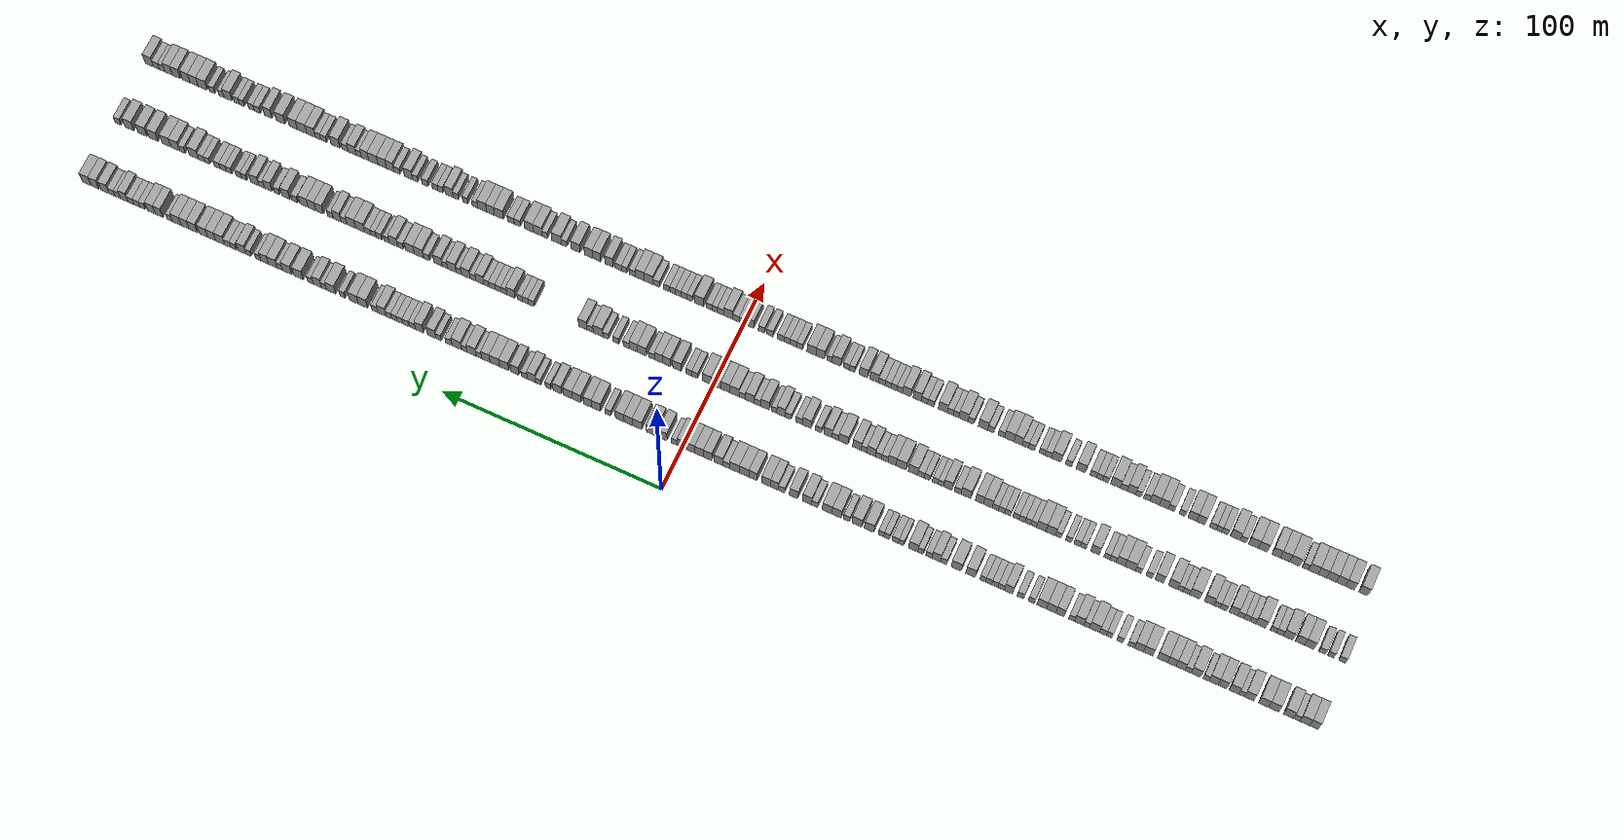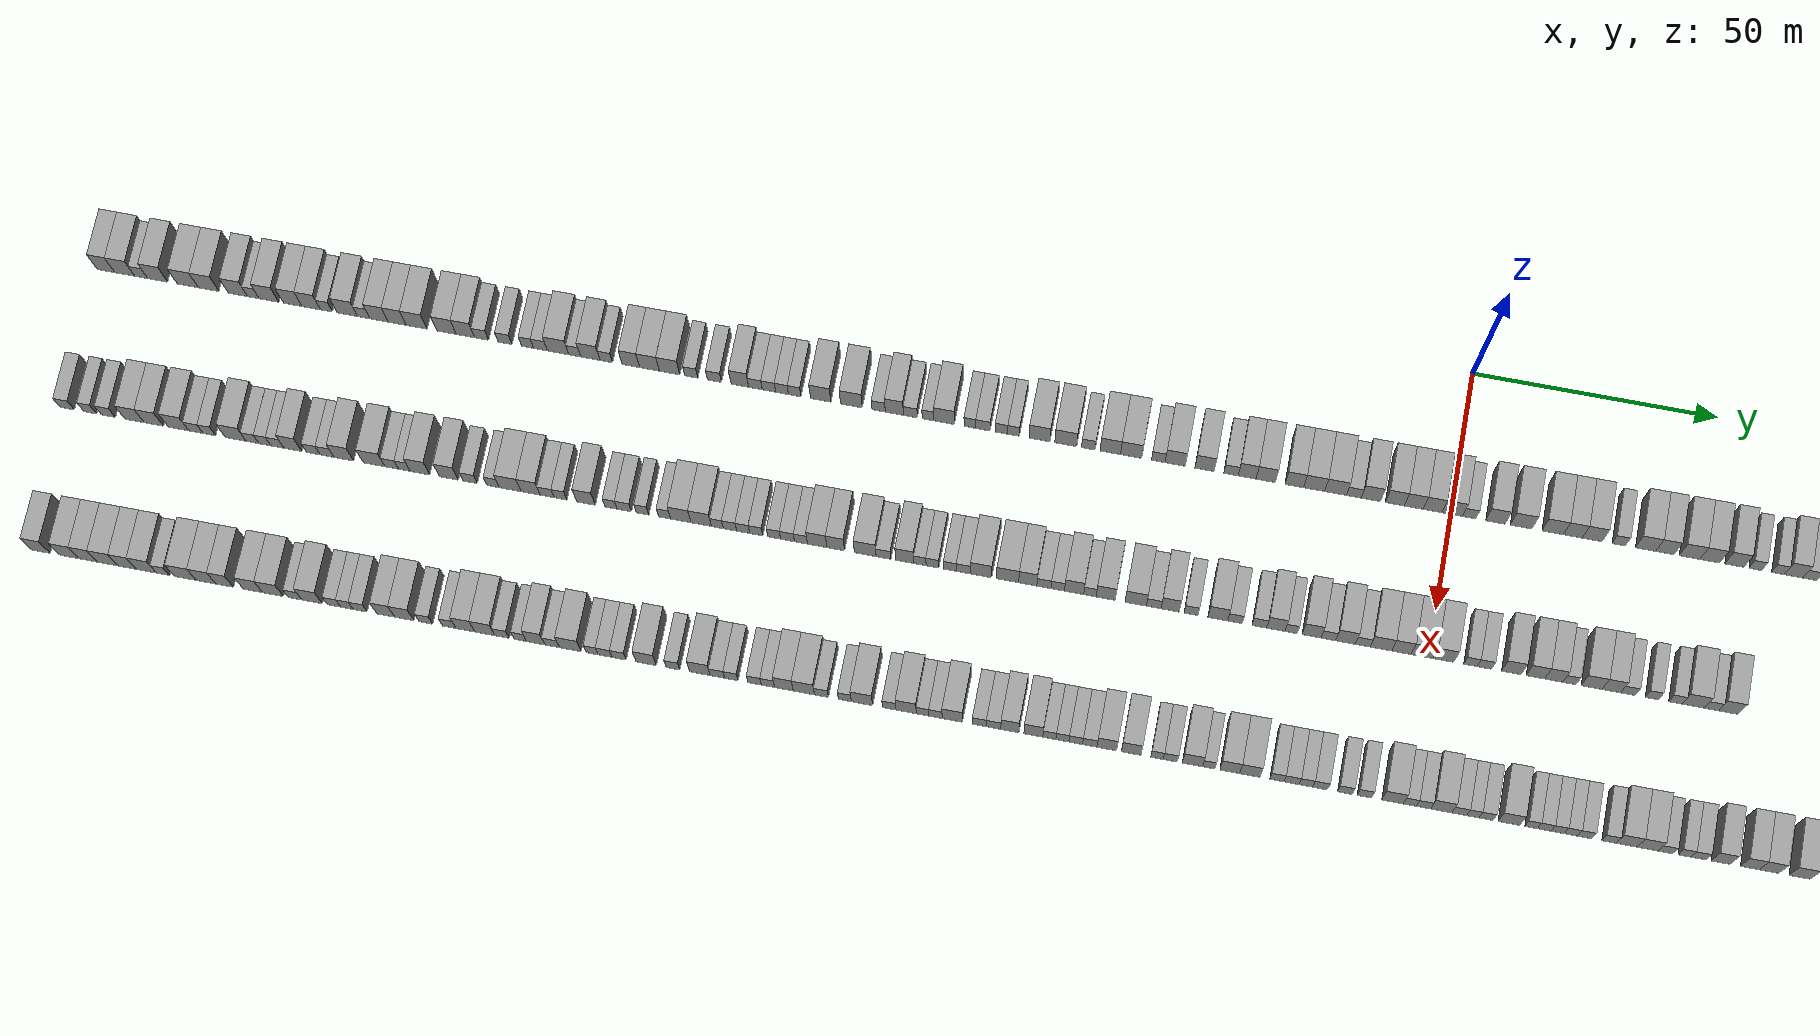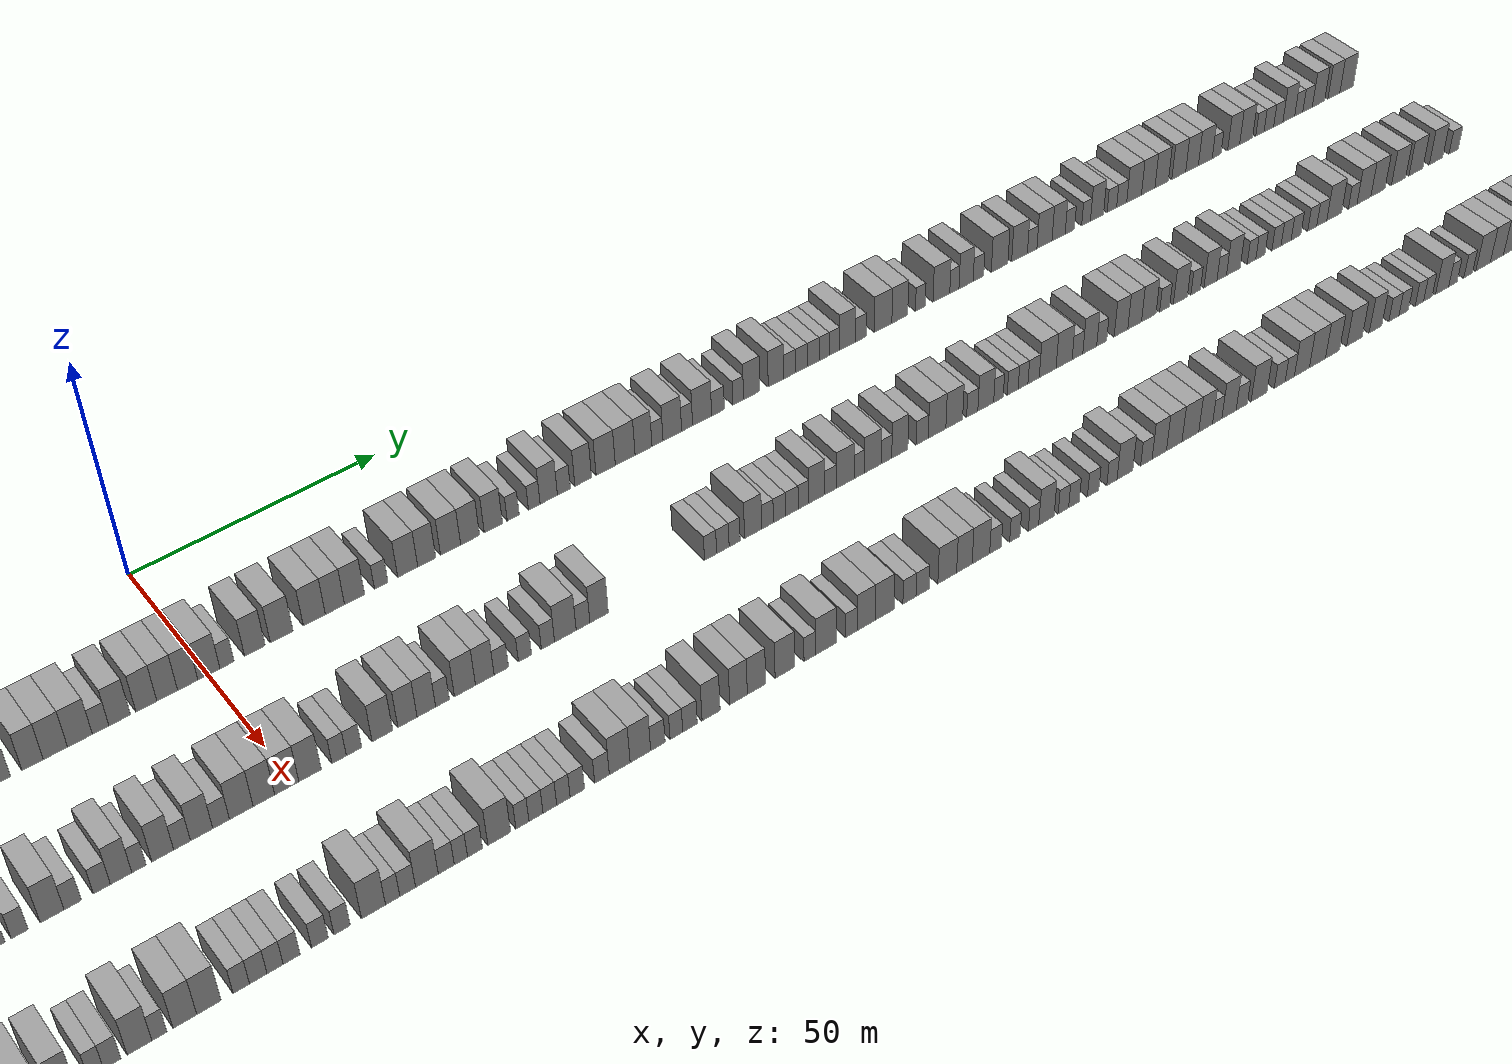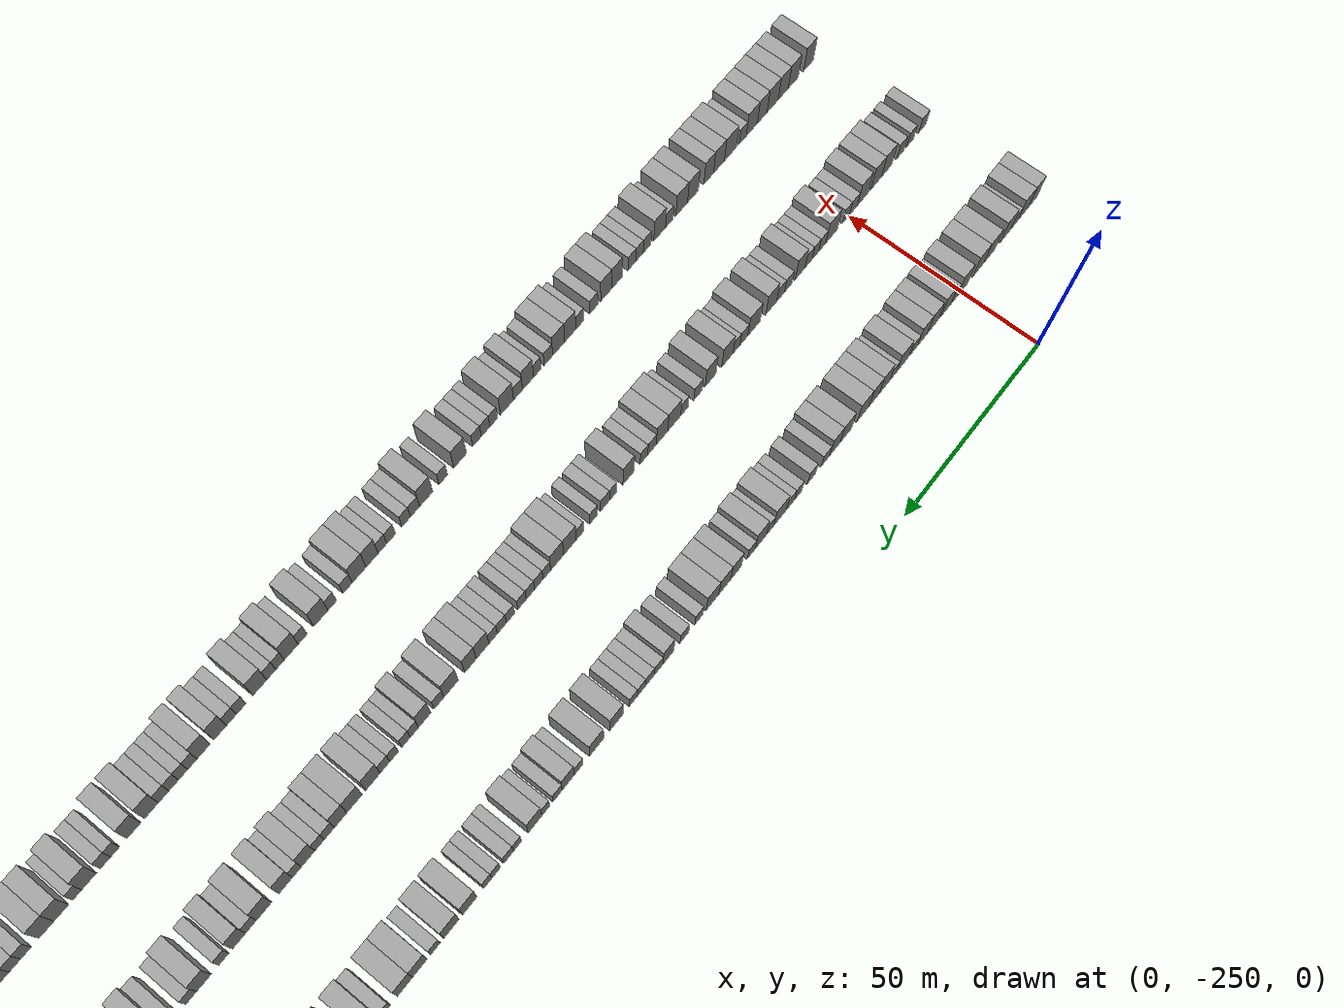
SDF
<sdf version="1.6">
 <world name="default">
  <scene>
   <sky><clouds><speed>12</speed></clouds></sky>
   <ambient>0.4 0.4 0.4 1</ambient>
   <background>0.7 0.7 0.7 1</background>
   <shadows>1</shadows>
  </scene>
  <gravity>0 0 -9.8066</gravity>
  <magnetic_field>6e-06 2.3e-05 -4.2e-05</magnetic_field>
  <physics default="0" name="default_physics" type="ode">
   <ode>
    <solver>
     <type>quick</type>
     <iters>10</iters>
     <sor>1.0</sor>
     <use_dynamic_moi_rescaling>0</use_dynamic_moi_rescaling>
    </solver>
    <constraints>
     <cfm>0</cfm>
     <erp>0.2</erp>
     <contact_max_correcting_vel>100</contact_max_correcting_vel>
     <contact_surface_layer>0.001</contact_surface_layer>
    </constraints>
   </ode>
   <max_step_size>0.004</max_step_size>
   <real_time_factor>1</real_time_factor>
   <real_time_update_rate>250</real_time_update_rate>
  </physics>
  <light name="sun" type="directional">
   <pose>0 0 10 0 0 0</pose>
   <diffuse>0.8 0.8 0.8 1</diffuse>
   <specular>0.2 0.2 0.2 1</specular>
   <attenuation>
    <range>1000</range>
    <constant>0.9</constant>
    <linear>0.01</linear>
    <quadratic>0.001</quadratic>
   </attenuation>
   <direction>-0.5 0.1 -0.9</direction>
  </light>
  <model name="building_1">
   <static>1</static>
   <pose>25.0000 -278.1549 0 0.000000 0.000000 0.000000</pose>
   <link name="link">
    <pose>0 0 4.50 0 0 0</pose>
    <collision name="collision"><geometry><box><size>10.0000 3.6901 9.0000</size></box></geometry></collision>
    <visual name="visual">
     <cast_shadows>0</cast_shadows>
     <geometry><box><size>10.0000 3.6901 9.0000</size></box></geometry>
     <material>
      <script>
       <uri>model://grey_wall/materials/scripts</uri>
       <uri>model://grey_wall/materials/textures</uri>
       <name>vrc/grey_wall</name>
      </script>
     </material>
    </visual>
   </link>
  </model>
  <model name="building_2">
   <static>1</static>
   <pose>25.0000 -274.2175 0 0.000000 0.000000 0.000000</pose>
   <link name="link">
    <pose>0 0 4.50 0 0 0</pose>
    <collision name="collision"><geometry><box><size>10.0000 4.1848 9.0000</size></box></geometry></collision>
    <visual name="visual">
     <cast_shadows>0</cast_shadows>
     <geometry><box><size>10.0000 4.1848 9.0000</size></box></geometry>
     <material>
      <script>
       <uri>model://grey_wall/materials/scripts</uri>
       <uri>model://grey_wall/materials/textures</uri>
       <name>vrc/grey_wall</name>
      </script>
     </material>
    </visual>
   </link>
  </model>
  <model name="building_3">
   <static>1</static>
   <pose>25.0000 -270.7490 0 0.000000 0.000000 0.000000</pose>
   <link name="link">
    <pose>0 0 3.00 0 0 0</pose>
    <collision name="collision"><geometry><box><size>10.0000 2.7521 6.0000</size></box></geometry></collision>
    <visual name="visual">
     <cast_shadows>0</cast_shadows>
     <geometry><box><size>10.0000 2.7521 6.0000</size></box></geometry>
     <material>
      <script>
       <uri>model://grey_wall/materials/scripts</uri>
       <uri>model://grey_wall/materials/textures</uri>
       <name>vrc/grey_wall</name>
      </script>
     </material>
    </visual>
   </link>
  </model>
  <model name="building_4">
   <static>1</static>
   <pose>25.0000 -267.2782 0 0.000000 0.000000 0.000000</pose>
   <link name="link">
    <pose>0 0 4.50 0 0 0</pose>
    <collision name="collision"><geometry><box><size>10.0000 4.1897 9.0000</size></box></geometry></collision>
    <visual name="visual">
     <cast_shadows>0</cast_shadows>
     <geometry><box><size>10.0000 4.1897 9.0000</size></box></geometry>
     <material>
      <script>
       <uri>model://grey_wall/materials/scripts</uri>
       <uri>model://grey_wall/materials/textures</uri>
       <name>vrc/grey_wall</name>
      </script>
     </material>
    </visual>
   </link>
  </model>
  <model name="building_5">
   <static>1</static>
   <pose>25.0000 -260.9586 0 0.000000 0.000000 0.000000</pose>
   <link name="link">
    <pose>0 0 4.50 0 0 0</pose>
    <collision name="collision"><geometry><box><size>10.0000 4.4494 9.0000</size></box></geometry></collision>
    <visual name="visual">
     <cast_shadows>0</cast_shadows>
     <geometry><box><size>10.0000 4.4494 9.0000</size></box></geometry>
     <material>
      <script>
       <uri>model://grey_wall/materials/scripts</uri>
       <uri>model://grey_wall/materials/textures</uri>
       <name>vrc/grey_wall</name>
      </script>
     </material>
    </visual>
   </link>
  </model>
  <model name="building_6">
   <static>1</static>
   <pose>25.0000 -256.5826 0 0.000000 0.000000 0.000000</pose>
   <link name="link">
    <pose>0 0 4.50 0 0 0</pose>
    <collision name="collision"><geometry><box><size>10.0000 4.3028 9.0000</size></box></geometry></collision>
    <visual name="visual">
     <cast_shadows>0</cast_shadows>
     <geometry><box><size>10.0000 4.3028 9.0000</size></box></geometry>
     <material>
      <script>
       <uri>model://grey_wall/materials/scripts</uri>
       <uri>model://grey_wall/materials/textures</uri>
       <name>vrc/grey_wall</name>
      </script>
     </material>
    </visual>
   </link>
  </model>
  <model name="building_7">
   <static>1</static>
   <pose>25.0000 -250.4064 0 0.000000 0.000000 0.000000</pose>
   <link name="link">
    <pose>0 0 4.50 0 0 0</pose>
    <collision name="collision"><geometry><box><size>10.0000 4.0496 9.0000</size></box></geometry></collision>
    <visual name="visual">
     <cast_shadows>0</cast_shadows>
     <geometry><box><size>10.0000 4.0496 9.0000</size></box></geometry>
     <material>
      <script>
       <uri>model://grey_wall/materials/scripts</uri>
       <uri>model://grey_wall/materials/textures</uri>
       <name>vrc/grey_wall</name>
      </script>
     </material>
    </visual>
   </link>
  </model>
  <model name="building_8">
   <static>1</static>
   <pose>25.0000 -247.1700 0 0.000000 0.000000 0.000000</pose>
   <link name="link">
    <pose>0 0 3.00 0 0 0</pose>
    <collision name="collision"><geometry><box><size>10.0000 2.4233 6.0000</size></box></geometry></collision>
    <visual name="visual">
     <cast_shadows>0</cast_shadows>
     <geometry><box><size>10.0000 2.4233 6.0000</size></box></geometry>
     <material>
      <script>
       <uri>model://grey_wall/materials/scripts</uri>
       <uri>model://grey_wall/materials/textures</uri>
       <name>vrc/grey_wall</name>
      </script>
     </material>
    </visual>
   </link>
  </model>
  <model name="building_9">
   <static>1</static>
   <pose>25.0000 -243.8986 0 0.000000 0.000000 0.000000</pose>
   <link name="link">
    <pose>0 0 4.50 0 0 0</pose>
    <collision name="collision"><geometry><box><size>10.0000 4.1194 9.0000</size></box></geometry></collision>
    <visual name="visual">
     <cast_shadows>0</cast_shadows>
     <geometry><box><size>10.0000 4.1194 9.0000</size></box></geometry>
     <material>
      <script>
       <uri>model://grey_wall/materials/scripts</uri>
       <uri>model://grey_wall/materials/textures</uri>
       <name>vrc/grey_wall</name>
      </script>
     </material>
    </visual>
   </link>
  </model>
  <model name="building_10">
   <static>1</static>
   <pose>25.0000 -238.8974 0 0.000000 0.000000 0.000000</pose>
   <link name="link">
    <pose>0 0 4.50 0 0 0</pose>
    <collision name="collision"><geometry><box><size>10.0000 3.8830 9.0000</size></box></geometry></collision>
    <visual name="visual">
     <cast_shadows>0</cast_shadows>
     <geometry><box><size>10.0000 3.8830 9.0000</size></box></geometry>
     <material>
      <script>
       <uri>model://grey_wall/materials/scripts</uri>
       <uri>model://grey_wall/materials/textures</uri>
       <name>vrc/grey_wall</name>
      </script>
     </material>
    </visual>
   </link>
  </model>
  <model name="building_11">
   <static>1</static>
   <pose>25.0000 -235.0119 0 0.000000 0.000000 0.000000</pose>
   <link name="link">
    <pose>0 0 4.50 0 0 0</pose>
    <collision name="collision"><geometry><box><size>10.0000 3.8880 9.0000</size></box></geometry></collision>
    <visual name="visual">
     <cast_shadows>0</cast_shadows>
     <geometry><box><size>10.0000 3.8880 9.0000</size></box></geometry>
     <material>
      <script>
       <uri>model://grey_wall/materials/scripts</uri>
       <uri>model://grey_wall/materials/textures</uri>
       <name>vrc/grey_wall</name>
      </script>
     </material>
    </visual>
   </link>
  </model>
  <model name="building_12">
   <static>1</static>
   <pose>25.0000 -231.8166 0 0.000000 0.000000 0.000000</pose>
   <link name="link">
    <pose>0 0 3.00 0 0 0</pose>
    <collision name="collision"><geometry><box><size>10.0000 2.5026 6.0000</size></box></geometry></collision>
    <visual name="visual">
     <cast_shadows>0</cast_shadows>
     <geometry><box><size>10.0000 2.5026 6.0000</size></box></geometry>
     <material>
      <script>
       <uri>model://grey_wall/materials/scripts</uri>
       <uri>model://grey_wall/materials/textures</uri>
       <name>vrc/grey_wall</name>
      </script>
     </material>
    </visual>
   </link>
  </model>
  <model name="building_13">
   <static>1</static>
   <pose>25.0000 -227.4403 0 0.000000 0.000000 0.000000</pose>
   <link name="link">
    <pose>0 0 4.50 0 0 0</pose>
    <collision name="collision"><geometry><box><size>10.0000 4.2500 9.0000</size></box></geometry></collision>
    <visual name="visual">
     <cast_shadows>0</cast_shadows>
     <geometry><box><size>10.0000 4.2500 9.0000</size></box></geometry>
     <material>
      <script>
       <uri>model://grey_wall/materials/scripts</uri>
       <uri>model://grey_wall/materials/textures</uri>
       <name>vrc/grey_wall</name>
      </script>
     </material>
    </visual>
   </link>
  </model>
  <model name="building_14">
   <static>1</static>
   <pose>25.0000 -224.0164 0 0.000000 0.000000 0.000000</pose>
   <link name="link">
    <pose>0 0 3.00 0 0 0</pose>
    <collision name="collision"><geometry><box><size>10.0000 2.5977 6.0000</size></box></geometry></collision>
    <visual name="visual">
     <cast_shadows>0</cast_shadows>
     <geometry><box><size>10.0000 2.5977 6.0000</size></box></geometry>
     <material>
      <script>
       <uri>model://grey_wall/materials/scripts</uri>
       <uri>model://grey_wall/materials/textures</uri>
       <name>vrc/grey_wall</name>
      </script>
     </material>
    </visual>
   </link>
  </model>
  <model name="building_15">
   <static>1</static>
   <pose>25.0000 -220.7955 0 0.000000 0.000000 0.000000</pose>
   <link name="link">
    <pose>0 0 4.50 0 0 0</pose>
    <collision name="collision"><geometry><box><size>10.0000 3.8441 9.0000</size></box></geometry></collision>
    <visual name="visual">
     <cast_shadows>0</cast_shadows>
     <geometry><box><size>10.0000 3.8441 9.0000</size></box></geometry>
     <material>
      <script>
       <uri>model://grey_wall/materials/scripts</uri>
       <uri>model://grey_wall/materials/textures</uri>
       <name>vrc/grey_wall</name>
      </script>
     </material>
    </visual>
   </link>
  </model>
  <model name="building_16">
   <static>1</static>
   <pose>25.0000 -217.0049 0 0.000000 0.000000 0.000000</pose>
   <link name="link">
    <pose>0 0 4.50 0 0 0</pose>
    <collision name="collision"><geometry><box><size>10.0000 3.7371 9.0000</size></box></geometry></collision>
    <visual name="visual">
     <cast_shadows>0</cast_shadows>
     <geometry><box><size>10.0000 3.7371 9.0000</size></box></geometry>
     <material>
      <script>
       <uri>model://grey_wall/materials/scripts</uri>
       <uri>model://grey_wall/materials/textures</uri>
       <name>vrc/grey_wall</name>
      </script>
     </material>
    </visual>
   </link>
  </model>
  <model name="building_17">
   <static>1</static>
   <pose>25.0000 -212.9558 0 0.000000 0.000000 0.000000</pose>
   <link name="link">
    <pose>0 0 4.50 0 0 0</pose>
    <collision name="collision"><geometry><box><size>10.0000 4.3610 9.0000</size></box></geometry></collision>
    <visual name="visual">
     <cast_shadows>0</cast_shadows>
     <geometry><box><size>10.0000 4.3610 9.0000</size></box></geometry>
     <material>
      <script>
       <uri>model://grey_wall/materials/scripts</uri>
       <uri>model://grey_wall/materials/textures</uri>
       <name>vrc/grey_wall</name>
      </script>
     </material>
    </visual>
   </link>
  </model>
  <model name="building_18">
   <static>1</static>
   <pose>25.0000 -206.7280 0 0.000000 0.000000 0.000000</pose>
   <link name="link">
    <pose>0 0 4.50 0 0 0</pose>
    <collision name="collision"><geometry><box><size>10.0000 4.0947 9.0000</size></box></geometry></collision>
    <visual name="visual">
     <cast_shadows>0</cast_shadows>
     <geometry><box><size>10.0000 4.0947 9.0000</size></box></geometry>
     <material>
      <script>
       <uri>model://grey_wall/materials/scripts</uri>
       <uri>model://grey_wall/materials/textures</uri>
       <name>vrc/grey_wall</name>
      </script>
     </material>
    </visual>
   </link>
  </model>
  <model name="building_19">
   <static>1</static>
   <pose>25.0000 -202.7622 0 0.000000 0.000000 0.000000</pose>
   <link name="link">
    <pose>0 0 4.50 0 0 0</pose>
    <collision name="collision"><geometry><box><size>10.0000 3.8369 9.0000</size></box></geometry></collision>
    <visual name="visual">
     <cast_shadows>0</cast_shadows>
     <geometry><box><size>10.0000 3.8369 9.0000</size></box></geometry>
     <material>
      <script>
       <uri>model://grey_wall/materials/scripts</uri>
       <uri>model://grey_wall/materials/textures</uri>
       <name>vrc/grey_wall</name>
      </script>
     </material>
    </visual>
   </link>
  </model>
  <model name="building_20">
   <static>1</static>
   <pose>25.0000 -199.3915 0 0.000000 0.000000 0.000000</pose>
   <link name="link">
    <pose>0 0 3.00 0 0 0</pose>
    <collision name="collision"><geometry><box><size>10.0000 2.9047 6.0000</size></box></geometry></collision>
    <visual name="visual">
     <cast_shadows>0</cast_shadows>
     <geometry><box><size>10.0000 2.9047 6.0000</size></box></geometry>
     <material>
      <script>
       <uri>model://grey_wall/materials/scripts</uri>
       <uri>model://grey_wall/materials/textures</uri>
       <name>vrc/grey_wall</name>
      </script>
     </material>
    </visual>
   </link>
  </model>
  <model name="building_21">
   <static>1</static>
   <pose>25.0000 -194.4979 0 0.000000 0.000000 0.000000</pose>
   <link name="link">
    <pose>0 0 3.00 0 0 0</pose>
    <collision name="collision"><geometry><box><size>10.0000 2.8824 6.0000</size></box></geometry></collision>
    <visual name="visual">
     <cast_shadows>0</cast_shadows>
     <geometry><box><size>10.0000 2.8824 6.0000</size></box></geometry>
     <material>
      <script>
       <uri>model://grey_wall/materials/scripts</uri>
       <uri>model://grey_wall/materials/textures</uri>
       <name>vrc/grey_wall</name>
      </script>
     </material>
    </visual>
   </link>
  </model>
  <model name="building_22">
   <static>1</static>
   <pose>25.0000 -189.7971 0 0.000000 0.000000 0.000000</pose>
   <link name="link">
    <pose>0 0 3.00 0 0 0</pose>
    <collision name="collision"><geometry><box><size>10.0000 2.5194 6.0000</size></box></geometry></collision>
    <visual name="visual">
     <cast_shadows>0</cast_shadows>
     <geometry><box><size>10.0000 2.5194 6.0000</size></box></geometry>
     <material>
      <script>
       <uri>model://grey_wall/materials/scripts</uri>
       <uri>model://grey_wall/materials/textures</uri>
       <name>vrc/grey_wall</name>
      </script>
     </material>
    </visual>
   </link>
  </model>
  <model name="building_23">
   <static>1</static>
   <pose>25.0000 -187.1224 0 0.000000 0.000000 0.000000</pose>
   <link name="link">
    <pose>0 0 3.00 0 0 0</pose>
    <collision name="collision"><geometry><box><size>10.0000 2.8300 6.0000</size></box></geometry></collision>
    <visual name="visual">
     <cast_shadows>0</cast_shadows>
     <geometry><box><size>10.0000 2.8300 6.0000</size></box></geometry>
     <material>
      <script>
       <uri>model://grey_wall/materials/scripts</uri>
       <uri>model://grey_wall/materials/textures</uri>
       <name>vrc/grey_wall</name>
      </script>
     </material>
    </visual>
   </link>
  </model>
  <model name="building_24">
   <static>1</static>
   <pose>25.0000 -183.4725 0 0.000000 0.000000 0.000000</pose>
   <link name="link">
    <pose>0 0 4.50 0 0 0</pose>
    <collision name="collision"><geometry><box><size>10.0000 4.4697 9.0000</size></box></geometry></collision>
    <visual name="visual">
     <cast_shadows>0</cast_shadows>
     <geometry><box><size>10.0000 4.4697 9.0000</size></box></geometry>
     <material>
      <script>
       <uri>model://grey_wall/materials/scripts</uri>
       <uri>model://grey_wall/materials/textures</uri>
       <name>vrc/grey_wall</name>
      </script>
     </material>
    </visual>
   </link>
  </model>
  <model name="building_25">
   <static>1</static>
   <pose>25.0000 -180.0024 0 0.000000 0.000000 0.000000</pose>
   <link name="link">
    <pose>0 0 3.00 0 0 0</pose>
    <collision name="collision"><geometry><box><size>10.0000 2.4706 6.0000</size></box></geometry></collision>
    <visual name="visual">
     <cast_shadows>0</cast_shadows>
     <geometry><box><size>10.0000 2.4706 6.0000</size></box></geometry>
     <material>
      <script>
       <uri>model://grey_wall/materials/scripts</uri>
       <uri>model://grey_wall/materials/textures</uri>
       <name>vrc/grey_wall</name>
      </script>
     </material>
    </visual>
   </link>
  </model>
  <model name="building_26">
   <static>1</static>
   <pose>25.0000 -176.7589 0 0.000000 0.000000 0.000000</pose>
   <link name="link">
    <pose>0 0 4.50 0 0 0</pose>
    <collision name="collision"><geometry><box><size>10.0000 4.0163 9.0000</size></box></geometry></collision>
    <visual name="visual">
     <cast_shadows>0</cast_shadows>
     <geometry><box><size>10.0000 4.0163 9.0000</size></box></geometry>
     <material>
      <script>
       <uri>model://grey_wall/materials/scripts</uri>
       <uri>model://grey_wall/materials/textures</uri>
       <name>vrc/grey_wall</name>
      </script>
     </material>
    </visual>
   </link>
  </model>
  <model name="building_27">
   <static>1</static>
   <pose>25.0000 -173.4452 0 0.000000 0.000000 0.000000</pose>
   <link name="link">
    <pose>0 0 3.00 0 0 0</pose>
    <collision name="collision"><geometry><box><size>10.0000 2.6112 6.0000</size></box></geometry></collision>
    <visual name="visual">
     <cast_shadows>0</cast_shadows>
     <geometry><box><size>10.0000 2.6112 6.0000</size></box></geometry>
     <material>
      <script>
       <uri>model://grey_wall/materials/scripts</uri>
       <uri>model://grey_wall/materials/textures</uri>
       <name>vrc/grey_wall</name>
      </script>
     </material>
    </visual>
   </link>
  </model>
  <model name="building_28">
   <static>1</static>
   <pose>25.0000 -168.3313 0 0.000000 0.000000 0.000000</pose>
   <link name="link">
    <pose>0 0 4.50 0 0 0</pose>
    <collision name="collision"><geometry><box><size>10.0000 3.6166 9.0000</size></box></geometry></collision>
    <visual name="visual">
     <cast_shadows>0</cast_shadows>
     <geometry><box><size>10.0000 3.6166 9.0000</size></box></geometry>
     <material>
      <script>
       <uri>model://grey_wall/materials/scripts</uri>
       <uri>model://grey_wall/materials/textures</uri>
       <name>vrc/grey_wall</name>
      </script>
     </material>
    </visual>
   </link>
  </model>
  <model name="building_29">
   <static>1</static>
   <pose>25.0000 -164.4670 0 0.000000 0.000000 0.000000</pose>
   <link name="link">
    <pose>0 0 4.50 0 0 0</pose>
    <collision name="collision"><geometry><box><size>10.0000 4.1120 9.0000</size></box></geometry></collision>
    <visual name="visual">
     <cast_shadows>0</cast_shadows>
     <geometry><box><size>10.0000 4.1120 9.0000</size></box></geometry>
     <material>
      <script>
       <uri>model://grey_wall/materials/scripts</uri>
       <uri>model://grey_wall/materials/textures</uri>
       <name>vrc/grey_wall</name>
      </script>
     </material>
    </visual>
   </link>
  </model>
  <model name="building_30">
   <static>1</static>
   <pose>25.0000 -160.2946 0 0.000000 0.000000 0.000000</pose>
   <link name="link">
    <pose>0 0 4.50 0 0 0</pose>
    <collision name="collision"><geometry><box><size>10.0000 4.2327 9.0000</size></box></geometry></collision>
    <visual name="visual">
     <cast_shadows>0</cast_shadows>
     <geometry><box><size>10.0000 4.2327 9.0000</size></box></geometry>
     <material>
      <script>
       <uri>model://grey_wall/materials/scripts</uri>
       <uri>model://grey_wall/materials/textures</uri>
       <name>vrc/grey_wall</name>
      </script>
     </material>
    </visual>
   </link>
  </model>
  <model name="building_31">
   <static>1</static>
   <pose>25.0000 -155.8138 0 0.000000 0.000000 0.000000</pose>
   <link name="link">
    <pose>0 0 3.00 0 0 0</pose>
    <collision name="collision"><geometry><box><size>10.0000 2.7290 6.0000</size></box></geometry></collision>
    <visual name="visual">
     <cast_shadows>0</cast_shadows>
     <geometry><box><size>10.0000 2.7290 6.0000</size></box></geometry>
     <material>
      <script>
       <uri>model://grey_wall/materials/scripts</uri>
       <uri>model://grey_wall/materials/textures</uri>
       <name>vrc/grey_wall</name>
      </script>
     </material>
    </visual>
   </link>
  </model>
  <model name="building_32">
   <static>1</static>
   <pose>25.0000 -151.0046 0 0.000000 0.000000 0.000000</pose>
   <link name="link">
    <pose>0 0 3.00 0 0 0</pose>
    <collision name="collision"><geometry><box><size>10.0000 2.8893 6.0000</size></box></geometry></collision>
    <visual name="visual">
     <cast_shadows>0</cast_shadows>
     <geometry><box><size>10.0000 2.8893 6.0000</size></box></geometry>
     <material>
      <script>
       <uri>model://grey_wall/materials/scripts</uri>
       <uri>model://grey_wall/materials/textures</uri>
       <name>vrc/grey_wall</name>
      </script>
     </material>
    </visual>
   </link>
  </model>
  <model name="building_33">
   <static>1</static>
   <pose>25.0000 -145.7402 0 0.000000 0.000000 0.000000</pose>
   <link name="link">
    <pose>0 0 4.50 0 0 0</pose>
    <collision name="collision"><geometry><box><size>10.0000 3.6397 9.0000</size></box></geometry></collision>
    <visual name="visual">
     <cast_shadows>0</cast_shadows>
     <geometry><box><size>10.0000 3.6397 9.0000</size></box></geometry>
     <material>
      <script>
       <uri>model://grey_wall/materials/scripts</uri>
       <uri>model://grey_wall/materials/textures</uri>
       <name>vrc/grey_wall</name>
      </script>
     </material>
    </visual>
   </link>
  </model>
  <model name="building_34">
   <static>1</static>
   <pose>25.0000 -142.5089 0 0.000000 0.000000 0.000000</pose>
   <link name="link">
    <pose>0 0 3.00 0 0 0</pose>
    <collision name="collision"><geometry><box><size>10.0000 2.8229 6.0000</size></box></geometry></collision>
    <visual name="visual">
     <cast_shadows>0</cast_shadows>
     <geometry><box><size>10.0000 2.8229 6.0000</size></box></geometry>
     <material>
      <script>
       <uri>model://grey_wall/materials/scripts</uri>
       <uri>model://grey_wall/materials/textures</uri>
       <name>vrc/grey_wall</name>
      </script>
     </material>
    </visual>
   </link>
  </model>
  <model name="building_35">
   <static>1</static>
   <pose>25.0000 -139.7180 0 0.000000 0.000000 0.000000</pose>
   <link name="link">
    <pose>0 0 3.00 0 0 0</pose>
    <collision name="collision"><geometry><box><size>10.0000 2.7589 6.0000</size></box></geometry></collision>
    <visual name="visual">
     <cast_shadows>0</cast_shadows>
     <geometry><box><size>10.0000 2.7589 6.0000</size></box></geometry>
     <material>
      <script>
       <uri>model://grey_wall/materials/scripts</uri>
       <uri>model://grey_wall/materials/textures</uri>
       <name>vrc/grey_wall</name>
      </script>
     </material>
    </visual>
   </link>
  </model>
  <model name="building_36">
   <static>1</static>
   <pose>25.0000 -137.0190 0 0.000000 0.000000 0.000000</pose>
   <link name="link">
    <pose>0 0 3.00 0 0 0</pose>
    <collision name="collision"><geometry><box><size>10.0000 2.6390 6.0000</size></box></geometry></collision>
    <visual name="visual">
     <cast_shadows>0</cast_shadows>
     <geometry><box><size>10.0000 2.6390 6.0000</size></box></geometry>
     <material>
      <script>
       <uri>model://grey_wall/materials/scripts</uri>
       <uri>model://grey_wall/materials/textures</uri>
       <name>vrc/grey_wall</name>
      </script>
     </material>
    </visual>
   </link>
  </model>
  <model name="building_37">
   <static>1</static>
   <pose>25.0000 -134.4072 0 0.000000 0.000000 0.000000</pose>
   <link name="link">
    <pose>0 0 3.00 0 0 0</pose>
    <collision name="collision"><geometry><box><size>10.0000 2.5846 6.0000</size></box></geometry></collision>
    <visual name="visual">
     <cast_shadows>0</cast_shadows>
     <geometry><box><size>10.0000 2.5846 6.0000</size></box></geometry>
     <material>
      <script>
       <uri>model://grey_wall/materials/scripts</uri>
       <uri>model://grey_wall/materials/textures</uri>
       <name>vrc/grey_wall</name>
      </script>
     </material>
    </visual>
   </link>
  </model>
  <model name="building_38">
   <static>1</static>
   <pose>25.0000 -129.0201 0 0.000000 0.000000 0.000000</pose>
   <link name="link">
    <pose>0 0 4.50 0 0 0</pose>
    <collision name="collision"><geometry><box><size>10.0000 4.1896 9.0000</size></box></geometry></collision>
    <visual name="visual">
     <cast_shadows>0</cast_shadows>
     <geometry><box><size>10.0000 4.1896 9.0000</size></box></geometry>
     <material>
      <script>
       <uri>model://grey_wall/materials/scripts</uri>
       <uri>model://grey_wall/materials/textures</uri>
       <name>vrc/grey_wall</name>
      </script>
     </material>
    </visual>
   </link>
  </model>
  <model name="building_39">
   <static>1</static>
   <pose>25.0000 -122.6942 0 0.000000 0.000000 0.000000</pose>
   <link name="link">
    <pose>0 0 4.50 0 0 0</pose>
    <collision name="collision"><geometry><box><size>10.0000 4.4624 9.0000</size></box></geometry></collision>
    <visual name="visual">
     <cast_shadows>0</cast_shadows>
     <geometry><box><size>10.0000 4.4624 9.0000</size></box></geometry>
     <material>
      <script>
       <uri>model://grey_wall/materials/scripts</uri>
       <uri>model://grey_wall/materials/textures</uri>
       <name>vrc/grey_wall</name>
      </script>
     </material>
    </visual>
   </link>
  </model>
  <model name="building_40">
   <static>1</static>
   <pose>25.0000 -117.0867 0 0.000000 0.000000 0.000000</pose>
   <link name="link">
    <pose>0 0 3.00 0 0 0</pose>
    <collision name="collision"><geometry><box><size>10.0000 2.7526 6.0000</size></box></geometry></collision>
    <visual name="visual">
     <cast_shadows>0</cast_shadows>
     <geometry><box><size>10.0000 2.7526 6.0000</size></box></geometry>
     <material>
      <script>
       <uri>model://grey_wall/materials/scripts</uri>
       <uri>model://grey_wall/materials/textures</uri>
       <name>vrc/grey_wall</name>
      </script>
     </material>
    </visual>
   </link>
  </model>
  <model name="building_41">
   <static>1</static>
   <pose>25.0000 -113.8457 0 0.000000 0.000000 0.000000</pose>
   <link name="link">
    <pose>0 0 4.50 0 0 0</pose>
    <collision name="collision"><geometry><box><size>10.0000 3.7295 9.0000</size></box></geometry></collision>
    <visual name="visual">
     <cast_shadows>0</cast_shadows>
     <geometry><box><size>10.0000 3.7295 9.0000</size></box></geometry>
     <material>
      <script>
       <uri>model://grey_wall/materials/scripts</uri>
       <uri>model://grey_wall/materials/textures</uri>
       <name>vrc/grey_wall</name>
      </script>
     </material>
    </visual>
   </link>
  </model>
  <model name="building_42">
   <static>1</static>
   <pose>25.0000 -110.5512 0 0.000000 0.000000 0.000000</pose>
   <link name="link">
    <pose>0 0 3.00 0 0 0</pose>
    <collision name="collision"><geometry><box><size>10.0000 2.8595 6.0000</size></box></geometry></collision>
    <visual name="visual">
     <cast_shadows>0</cast_shadows>
     <geometry><box><size>10.0000 2.8595 6.0000</size></box></geometry>
     <material>
      <script>
       <uri>model://grey_wall/materials/scripts</uri>
       <uri>model://grey_wall/materials/textures</uri>
       <name>vrc/grey_wall</name>
      </script>
     </material>
    </visual>
   </link>
  </model>
  <model name="building_43">
   <static>1</static>
   <pose>25.0000 -106.9096 0 0.000000 0.000000 0.000000</pose>
   <link name="link">
    <pose>0 0 3.00 0 0 0</pose>
    <collision name="collision"><geometry><box><size>10.0000 2.4235 6.0000</size></box></geometry></collision>
    <visual name="visual">
     <cast_shadows>0</cast_shadows>
     <geometry><box><size>10.0000 2.4235 6.0000</size></box></geometry>
     <material>
      <script>
       <uri>model://grey_wall/materials/scripts</uri>
       <uri>model://grey_wall/materials/textures</uri>
       <name>vrc/grey_wall</name>
      </script>
     </material>
    </visual>
   </link>
  </model>
  <model name="building_44">
   <static>1</static>
   <pose>25.0000 -103.6052 0 0.000000 0.000000 0.000000</pose>
   <link name="link">
    <pose>0 0 4.50 0 0 0</pose>
    <collision name="collision"><geometry><box><size>10.0000 4.1853 9.0000</size></box></geometry></collision>
    <visual name="visual">
     <cast_shadows>0</cast_shadows>
     <geometry><box><size>10.0000 4.1853 9.0000</size></box></geometry>
     <material>
      <script>
       <uri>model://grey_wall/materials/scripts</uri>
       <uri>model://grey_wall/materials/textures</uri>
       <name>vrc/grey_wall</name>
      </script>
     </material>
    </visual>
   </link>
  </model>
  <model name="building_45">
   <static>1</static>
   <pose>25.0000 -98.3105 0 0.000000 0.000000 0.000000</pose>
   <link name="link">
    <pose>0 0 3.00 0 0 0</pose>
    <collision name="collision"><geometry><box><size>10.0000 2.4042 6.0000</size></box></geometry></collision>
    <visual name="visual">
     <cast_shadows>0</cast_shadows>
     <geometry><box><size>10.0000 2.4042 6.0000</size></box></geometry>
     <material>
      <script>
       <uri>model://grey_wall/materials/scripts</uri>
       <uri>model://grey_wall/materials/textures</uri>
       <name>vrc/grey_wall</name>
      </script>
     </material>
    </visual>
   </link>
  </model>
  <model name="building_46">
   <static>1</static>
   <pose>25.0000 -95.6252 0 0.000000 0.000000 0.000000</pose>
   <link name="link">
    <pose>0 0 3.00 0 0 0</pose>
    <collision name="collision"><geometry><box><size>10.0000 2.9663 6.0000</size></box></geometry></collision>
    <visual name="visual">
     <cast_shadows>0</cast_shadows>
     <geometry><box><size>10.0000 2.9663 6.0000</size></box></geometry>
     <material>
      <script>
       <uri>model://grey_wall/materials/scripts</uri>
       <uri>model://grey_wall/materials/textures</uri>
       <name>vrc/grey_wall</name>
      </script>
     </material>
    </visual>
   </link>
  </model>
  <model name="building_47">
   <static>1</static>
   <pose>25.0000 -91.8514 0 0.000000 0.000000 0.000000</pose>
   <link name="link">
    <pose>0 0 3.00 0 0 0</pose>
    <collision name="collision"><geometry><box><size>10.0000 2.5813 6.0000</size></box></geometry></collision>
    <visual name="visual">
     <cast_shadows>0</cast_shadows>
     <geometry><box><size>10.0000 2.5813 6.0000</size></box></geometry>
     <material>
      <script>
       <uri>model://grey_wall/materials/scripts</uri>
       <uri>model://grey_wall/materials/textures</uri>
       <name>vrc/grey_wall</name>
      </script>
     </material>
    </visual>
   </link>
  </model>
  <model name="building_48">
   <static>1</static>
   <pose>25.0000 -89.3444 0 0.000000 0.000000 0.000000</pose>
   <link name="link">
    <pose>0 0 3.00 0 0 0</pose>
    <collision name="collision"><geometry><box><size>10.0000 2.4326 6.0000</size></box></geometry></collision>
    <visual name="visual">
     <cast_shadows>0</cast_shadows>
     <geometry><box><size>10.0000 2.4326 6.0000</size></box></geometry>
     <material>
      <script>
       <uri>model://grey_wall/materials/scripts</uri>
       <uri>model://grey_wall/materials/textures</uri>
       <name>vrc/grey_wall</name>
      </script>
     </material>
    </visual>
   </link>
  </model>
  <model name="building_49">
   <static>1</static>
   <pose>25.0000 -83.9963 0 0.000000 0.000000 0.000000</pose>
   <link name="link">
    <pose>0 0 4.50 0 0 0</pose>
    <collision name="collision"><geometry><box><size>10.0000 4.2638 9.0000</size></box></geometry></collision>
    <visual name="visual">
     <cast_shadows>0</cast_shadows>
     <geometry><box><size>10.0000 4.2638 9.0000</size></box></geometry>
     <material>
      <script>
       <uri>model://grey_wall/materials/scripts</uri>
       <uri>model://grey_wall/materials/textures</uri>
       <name>vrc/grey_wall</name>
      </script>
     </material>
    </visual>
   </link>
  </model>
  <model name="building_50">
   <static>1</static>
   <pose>25.0000 -78.6208 0 0.000000 0.000000 0.000000</pose>
   <link name="link">
    <pose>0 0 4.50 0 0 0</pose>
    <collision name="collision"><geometry><box><size>10.0000 4.4872 9.0000</size></box></geometry></collision>
    <visual name="visual">
     <cast_shadows>0</cast_shadows>
     <geometry><box><size>10.0000 4.4872 9.0000</size></box></geometry>
     <material>
      <script>
       <uri>model://grey_wall/materials/scripts</uri>
       <uri>model://grey_wall/materials/textures</uri>
       <name>vrc/grey_wall</name>
      </script>
     </material>
    </visual>
   </link>
  </model>
  <model name="building_51">
   <static>1</static>
   <pose>25.0000 -73.9829 0 0.000000 0.000000 0.000000</pose>
   <link name="link">
    <pose>0 0 3.00 0 0 0</pose>
    <collision name="collision"><geometry><box><size>10.0000 2.7885 6.0000</size></box></geometry></collision>
    <visual name="visual">
     <cast_shadows>0</cast_shadows>
     <geometry><box><size>10.0000 2.7885 6.0000</size></box></geometry>
     <material>
      <script>
       <uri>model://grey_wall/materials/scripts</uri>
       <uri>model://grey_wall/materials/textures</uri>
       <name>vrc/grey_wall</name>
      </script>
     </material>
    </visual>
   </link>
  </model>
  <model name="building_52">
   <static>1</static>
   <pose>25.0000 -69.4989 0 0.000000 0.000000 0.000000</pose>
   <link name="link">
    <pose>0 0 4.50 0 0 0</pose>
    <collision name="collision"><geometry><box><size>10.0000 4.1795 9.0000</size></box></geometry></collision>
    <visual name="visual">
     <cast_shadows>0</cast_shadows>
     <geometry><box><size>10.0000 4.1795 9.0000</size></box></geometry>
     <material>
      <script>
       <uri>model://grey_wall/materials/scripts</uri>
       <uri>model://grey_wall/materials/textures</uri>
       <name>vrc/grey_wall</name>
      </script>
     </material>
    </visual>
   </link>
  </model>
  <model name="building_53">
   <static>1</static>
   <pose>25.0000 -65.2397 0 0.000000 0.000000 0.000000</pose>
   <link name="link">
    <pose>0 0 4.50 0 0 0</pose>
    <collision name="collision"><geometry><box><size>10.0000 4.3389 9.0000</size></box></geometry></collision>
    <visual name="visual">
     <cast_shadows>0</cast_shadows>
     <geometry><box><size>10.0000 4.3389 9.0000</size></box></geometry>
     <material>
      <script>
       <uri>model://grey_wall/materials/scripts</uri>
       <uri>model://grey_wall/materials/textures</uri>
       <name>vrc/grey_wall</name>
      </script>
     </material>
    </visual>
   </link>
  </model>
  <model name="building_54">
   <static>1</static>
   <pose>25.0000 -59.6784 0 0.000000 0.000000 0.000000</pose>
   <link name="link">
    <pose>0 0 3.00 0 0 0</pose>
    <collision name="collision"><geometry><box><size>10.0000 2.7838 6.0000</size></box></geometry></collision>
    <visual name="visual">
     <cast_shadows>0</cast_shadows>
     <geometry><box><size>10.0000 2.7838 6.0000</size></box></geometry>
     <material>
      <script>
       <uri>model://grey_wall/materials/scripts</uri>
       <uri>model://grey_wall/materials/textures</uri>
       <name>vrc/grey_wall</name>
      </script>
     </material>
    </visual>
   </link>
  </model>
  <model name="building_55">
   <static>1</static>
   <pose>25.0000 -56.2320 0 0.000000 0.000000 0.000000</pose>
   <link name="link">
    <pose>0 0 4.50 0 0 0</pose>
    <collision name="collision"><geometry><box><size>10.0000 4.1091 9.0000</size></box></geometry></collision>
    <visual name="visual">
     <cast_shadows>0</cast_shadows>
     <geometry><box><size>10.0000 4.1091 9.0000</size></box></geometry>
     <material>
      <script>
       <uri>model://grey_wall/materials/scripts</uri>
       <uri>model://grey_wall/materials/textures</uri>
       <name>vrc/grey_wall</name>
      </script>
     </material>
    </visual>
   </link>
  </model>
  <model name="building_56">
   <static>1</static>
   <pose>25.0000 -50.2350 0 0.000000 0.000000 0.000000</pose>
   <link name="link">
    <pose>0 0 4.50 0 0 0</pose>
    <collision name="collision"><geometry><box><size>10.0000 3.8848 9.0000</size></box></geometry></collision>
    <visual name="visual">
     <cast_shadows>0</cast_shadows>
     <geometry><box><size>10.0000 3.8848 9.0000</size></box></geometry>
     <material>
      <script>
       <uri>model://grey_wall/materials/scripts</uri>
       <uri>model://grey_wall/materials/textures</uri>
       <name>vrc/grey_wall</name>
      </script>
     </material>
    </visual>
   </link>
  </model>
  <model name="building_57">
   <static>1</static>
   <pose>25.0000 -44.8190 0 0.000000 0.000000 0.000000</pose>
   <link name="link">
    <pose>0 0 3.00 0 0 0</pose>
    <collision name="collision"><geometry><box><size>10.0000 2.9473 6.0000</size></box></geometry></collision>
    <visual name="visual">
     <cast_shadows>0</cast_shadows>
     <geometry><box><size>10.0000 2.9473 6.0000</size></box></geometry>
     <material>
      <script>
       <uri>model://grey_wall/materials/scripts</uri>
       <uri>model://grey_wall/materials/textures</uri>
       <name>vrc/grey_wall</name>
      </script>
     </material>
    </visual>
   </link>
  </model>
  <model name="building_58">
   <static>1</static>
   <pose>25.0000 -41.5328 0 0.000000 0.000000 0.000000</pose>
   <link name="link">
    <pose>0 0 4.50 0 0 0</pose>
    <collision name="collision"><geometry><box><size>10.0000 3.6251 9.0000</size></box></geometry></collision>
    <visual name="visual">
     <cast_shadows>0</cast_shadows>
     <geometry><box><size>10.0000 3.6251 9.0000</size></box></geometry>
     <material>
      <script>
       <uri>model://grey_wall/materials/scripts</uri>
       <uri>model://grey_wall/materials/textures</uri>
       <name>vrc/grey_wall</name>
      </script>
     </material>
    </visual>
   </link>
  </model>
  <model name="building_59">
   <static>1</static>
   <pose>25.0000 -37.7586 0 0.000000 0.000000 0.000000</pose>
   <link name="link">
    <pose>0 0 4.50 0 0 0</pose>
    <collision name="collision"><geometry><box><size>10.0000 3.9233 9.0000</size></box></geometry></collision>
    <visual name="visual">
     <cast_shadows>0</cast_shadows>
     <geometry><box><size>10.0000 3.9233 9.0000</size></box></geometry>
     <material>
      <script>
       <uri>model://grey_wall/materials/scripts</uri>
       <uri>model://grey_wall/materials/textures</uri>
       <name>vrc/grey_wall</name>
      </script>
     </material>
    </visual>
   </link>
  </model>
  <model name="building_60">
   <static>1</static>
   <pose>25.0000 -31.9169 0 0.000000 0.000000 0.000000</pose>
   <link name="link">
    <pose>0 0 4.50 0 0 0</pose>
    <collision name="collision"><geometry><box><size>10.0000 3.7601 9.0000</size></box></geometry></collision>
    <visual name="visual">
     <cast_shadows>0</cast_shadows>
     <geometry><box><size>10.0000 3.7601 9.0000</size></box></geometry>
     <material>
      <script>
       <uri>model://grey_wall/materials/scripts</uri>
       <uri>model://grey_wall/materials/textures</uri>
       <name>vrc/grey_wall</name>
      </script>
     </material>
    </visual>
   </link>
  </model>
  <model name="building_61">
   <static>1</static>
   <pose>25.0000 -27.8898 0 0.000000 0.000000 0.000000</pose>
   <link name="link">
    <pose>0 0 4.50 0 0 0</pose>
    <collision name="collision"><geometry><box><size>10.0000 4.2941 9.0000</size></box></geometry></collision>
    <visual name="visual">
     <cast_shadows>0</cast_shadows>
     <geometry><box><size>10.0000 4.2941 9.0000</size></box></geometry>
     <material>
      <script>
       <uri>model://grey_wall/materials/scripts</uri>
       <uri>model://grey_wall/materials/textures</uri>
       <name>vrc/grey_wall</name>
      </script>
     </material>
    </visual>
   </link>
  </model>
  <model name="building_62">
   <static>1</static>
   <pose>25.0000 -23.5132 0 0.000000 0.000000 0.000000</pose>
   <link name="link">
    <pose>0 0 4.50 0 0 0</pose>
    <collision name="collision"><geometry><box><size>10.0000 4.4592 9.0000</size></box></geometry></collision>
    <visual name="visual">
     <cast_shadows>0</cast_shadows>
     <geometry><box><size>10.0000 4.4592 9.0000</size></box></geometry>
     <material>
      <script>
       <uri>model://grey_wall/materials/scripts</uri>
       <uri>model://grey_wall/materials/textures</uri>
       <name>vrc/grey_wall</name>
      </script>
     </material>
    </visual>
   </link>
  </model>
  <model name="building_63">
   <static>1</static>
   <pose>25.0000 -19.7858 0 0.000000 0.000000 0.000000</pose>
   <link name="link">
    <pose>0 0 3.00 0 0 0</pose>
    <collision name="collision"><geometry><box><size>10.0000 2.9956 6.0000</size></box></geometry></collision>
    <visual name="visual">
     <cast_shadows>0</cast_shadows>
     <geometry><box><size>10.0000 2.9956 6.0000</size></box></geometry>
     <material>
      <script>
       <uri>model://grey_wall/materials/scripts</uri>
       <uri>model://grey_wall/materials/textures</uri>
       <name>vrc/grey_wall</name>
      </script>
     </material>
    </visual>
   </link>
  </model>
  <model name="building_64">
   <static>1</static>
   <pose>25.0000 -16.3273 0 0.000000 0.000000 0.000000</pose>
   <link name="link">
    <pose>0 0 4.50 0 0 0</pose>
    <collision name="collision"><geometry><box><size>10.0000 3.9213 9.0000</size></box></geometry></collision>
    <visual name="visual">
     <cast_shadows>0</cast_shadows>
     <geometry><box><size>10.0000 3.9213 9.0000</size></box></geometry>
     <material>
      <script>
       <uri>model://grey_wall/materials/scripts</uri>
       <uri>model://grey_wall/materials/textures</uri>
       <name>vrc/grey_wall</name>
      </script>
     </material>
    </visual>
   </link>
  </model>
  <model name="building_65">
   <static>1</static>
   <pose>25.0000 -11.4402 0 0.000000 0.000000 0.000000</pose>
   <link name="link">
    <pose>0 0 4.50 0 0 0</pose>
    <collision name="collision"><geometry><box><size>10.0000 3.8529 9.0000</size></box></geometry></collision>
    <visual name="visual">
     <cast_shadows>0</cast_shadows>
     <geometry><box><size>10.0000 3.8529 9.0000</size></box></geometry>
     <material>
      <script>
       <uri>model://grey_wall/materials/scripts</uri>
       <uri>model://grey_wall/materials/textures</uri>
       <name>vrc/grey_wall</name>
      </script>
     </material>
    </visual>
   </link>
  </model>
  <model name="building_66">
   <static>1</static>
   <pose>25.0000 -7.5894 0 0.000000 0.000000 0.000000</pose>
   <link name="link">
    <pose>0 0 4.50 0 0 0</pose>
    <collision name="collision"><geometry><box><size>10.0000 3.8488 9.0000</size></box></geometry></collision>
    <visual name="visual">
     <cast_shadows>0</cast_shadows>
     <geometry><box><size>10.0000 3.8488 9.0000</size></box></geometry>
     <material>
      <script>
       <uri>model://grey_wall/materials/scripts</uri>
       <uri>model://grey_wall/materials/textures</uri>
       <name>vrc/grey_wall</name>
      </script>
     </material>
    </visual>
   </link>
  </model>
  <model name="building_67">
   <static>1</static>
   <pose>25.0000 -3.7619 0 0.000000 0.000000 0.000000</pose>
   <link name="link">
    <pose>0 0 4.50 0 0 0</pose>
    <collision name="collision"><geometry><box><size>10.0000 3.8061 9.0000</size></box></geometry></collision>
    <visual name="visual">
     <cast_shadows>0</cast_shadows>
     <geometry><box><size>10.0000 3.8061 9.0000</size></box></geometry>
     <material>
      <script>
       <uri>model://grey_wall/materials/scripts</uri>
       <uri>model://grey_wall/materials/textures</uri>
       <name>vrc/grey_wall</name>
      </script>
     </material>
    </visual>
   </link>
  </model>
  <model name="building_68">
   <static>1</static>
   <pose>25.0000 0.2181 0 0.000000 0.000000 0.000000</pose>
   <link name="link">
    <pose>0 0 4.50 0 0 0</pose>
    <collision name="collision"><geometry><box><size>10.0000 4.1541 9.0000</size></box></geometry></collision>
    <visual name="visual">
     <cast_shadows>0</cast_shadows>
     <geometry><box><size>10.0000 4.1541 9.0000</size></box></geometry>
     <material>
      <script>
       <uri>model://grey_wall/materials/scripts</uri>
       <uri>model://grey_wall/materials/textures</uri>
       <name>vrc/grey_wall</name>
      </script>
     </material>
    </visual>
   </link>
  </model>
  <model name="building_69">
   <static>1</static>
   <pose>25.0000 3.6451 0 0.000000 0.000000 0.000000</pose>
   <link name="link">
    <pose>0 0 3.00 0 0 0</pose>
    <collision name="collision"><geometry><box><size>10.0000 2.6998 6.0000</size></box></geometry></collision>
    <visual name="visual">
     <cast_shadows>0</cast_shadows>
     <geometry><box><size>10.0000 2.6998 6.0000</size></box></geometry>
     <material>
      <script>
       <uri>model://grey_wall/materials/scripts</uri>
       <uri>model://grey_wall/materials/textures</uri>
       <name>vrc/grey_wall</name>
      </script>
     </material>
    </visual>
   </link>
  </model>
  <model name="building_70">
   <static>1</static>
   <pose>25.0000 8.9769 0 0.000000 0.000000 0.000000</pose>
   <link name="link">
    <pose>0 0 4.50 0 0 0</pose>
    <collision name="collision"><geometry><box><size>10.0000 3.9638 9.0000</size></box></geometry></collision>
    <visual name="visual">
     <cast_shadows>0</cast_shadows>
     <geometry><box><size>10.0000 3.9638 9.0000</size></box></geometry>
     <material>
      <script>
       <uri>model://grey_wall/materials/scripts</uri>
       <uri>model://grey_wall/materials/textures</uri>
       <name>vrc/grey_wall</name>
      </script>
     </material>
    </visual>
   </link>
  </model>
  <model name="building_71">
   <static>1</static>
   <pose>25.0000 14.1702 0 0.000000 0.000000 0.000000</pose>
   <link name="link">
    <pose>0 0 4.50 0 0 0</pose>
    <collision name="collision"><geometry><box><size>10.0000 4.4229 9.0000</size></box></geometry></collision>
    <visual name="visual">
     <cast_shadows>0</cast_shadows>
     <geometry><box><size>10.0000 4.4229 9.0000</size></box></geometry>
     <material>
      <script>
       <uri>model://grey_wall/materials/scripts</uri>
       <uri>model://grey_wall/materials/textures</uri>
       <name>vrc/grey_wall</name>
      </script>
     </material>
    </visual>
   </link>
  </model>
  <model name="building_72">
   <static>1</static>
   <pose>25.0000 20.5548 0 0.000000 0.000000 0.000000</pose>
   <link name="link">
    <pose>0 0 4.50 0 0 0</pose>
    <collision name="collision"><geometry><box><size>10.0000 4.3463 9.0000</size></box></geometry></collision>
    <visual name="visual">
     <cast_shadows>0</cast_shadows>
     <geometry><box><size>10.0000 4.3463 9.0000</size></box></geometry>
     <material>
      <script>
       <uri>model://grey_wall/materials/scripts</uri>
       <uri>model://grey_wall/materials/textures</uri>
       <name>vrc/grey_wall</name>
      </script>
     </material>
    </visual>
   </link>
  </model>
  <model name="building_73">
   <static>1</static>
   <pose>25.0000 24.6365 0 0.000000 0.000000 0.000000</pose>
   <link name="link">
    <pose>0 0 4.50 0 0 0</pose>
    <collision name="collision"><geometry><box><size>10.0000 3.8170 9.0000</size></box></geometry></collision>
    <visual name="visual">
     <cast_shadows>0</cast_shadows>
     <geometry><box><size>10.0000 3.8170 9.0000</size></box></geometry>
     <material>
      <script>
       <uri>model://grey_wall/materials/scripts</uri>
       <uri>model://grey_wall/materials/textures</uri>
       <name>vrc/grey_wall</name>
      </script>
     </material>
    </visual>
   </link>
  </model>
  <model name="building_74">
   <static>1</static>
   <pose>25.0000 28.5519 0 0.000000 0.000000 0.000000</pose>
   <link name="link">
    <pose>0 0 4.50 0 0 0</pose>
    <collision name="collision"><geometry><box><size>10.0000 4.0139 9.0000</size></box></geometry></collision>
    <visual name="visual">
     <cast_shadows>0</cast_shadows>
     <geometry><box><size>10.0000 4.0139 9.0000</size></box></geometry>
     <material>
      <script>
       <uri>model://grey_wall/materials/scripts</uri>
       <uri>model://grey_wall/materials/textures</uri>
       <name>vrc/grey_wall</name>
      </script>
     </material>
    </visual>
   </link>
  </model>
  <model name="building_75">
   <static>1</static>
   <pose>25.0000 33.9201 0 0.000000 0.000000 0.000000</pose>
   <link name="link">
    <pose>0 0 3.00 0 0 0</pose>
    <collision name="collision"><geometry><box><size>10.0000 2.7224 6.0000</size></box></geometry></collision>
    <visual name="visual">
     <cast_shadows>0</cast_shadows>
     <geometry><box><size>10.0000 2.7224 6.0000</size></box></geometry>
     <material>
      <script>
       <uri>model://grey_wall/materials/scripts</uri>
       <uri>model://grey_wall/materials/textures</uri>
       <name>vrc/grey_wall</name>
      </script>
     </material>
    </visual>
   </link>
  </model>
  <model name="building_76">
   <static>1</static>
   <pose>25.0000 39.3360 0 0.000000 0.000000 0.000000</pose>
   <link name="link">
    <pose>0 0 4.50 0 0 0</pose>
    <collision name="collision"><geometry><box><size>10.0000 4.1094 9.0000</size></box></geometry></collision>
    <visual name="visual">
     <cast_shadows>0</cast_shadows>
     <geometry><box><size>10.0000 4.1094 9.0000</size></box></geometry>
     <material>
      <script>
       <uri>model://grey_wall/materials/scripts</uri>
       <uri>model://grey_wall/materials/textures</uri>
       <name>vrc/grey_wall</name>
      </script>
     </material>
    </visual>
   </link>
  </model>
  <model name="building_77">
   <static>1</static>
   <pose>25.0000 43.2441 0 0.000000 0.000000 0.000000</pose>
   <link name="link">
    <pose>0 0 4.50 0 0 0</pose>
    <collision name="collision"><geometry><box><size>10.0000 3.7069 9.0000</size></box></geometry></collision>
    <visual name="visual">
     <cast_shadows>0</cast_shadows>
     <geometry><box><size>10.0000 3.7069 9.0000</size></box></geometry>
     <material>
      <script>
       <uri>model://grey_wall/materials/scripts</uri>
       <uri>model://grey_wall/materials/textures</uri>
       <name>vrc/grey_wall</name>
      </script>
     </material>
    </visual>
   </link>
  </model>
  <model name="building_78">
   <static>1</static>
   <pose>25.0000 48.1934 0 0.000000 0.000000 0.000000</pose>
   <link name="link">
    <pose>0 0 4.50 0 0 0</pose>
    <collision name="collision"><geometry><box><size>10.0000 4.1918 9.0000</size></box></geometry></collision>
    <visual name="visual">
     <cast_shadows>0</cast_shadows>
     <geometry><box><size>10.0000 4.1918 9.0000</size></box></geometry>
     <material>
      <script>
       <uri>model://grey_wall/materials/scripts</uri>
       <uri>model://grey_wall/materials/textures</uri>
       <name>vrc/grey_wall</name>
      </script>
     </material>
    </visual>
   </link>
  </model>
  <model name="building_79">
   <static>1</static>
   <pose>25.0000 52.2779 0 0.000000 0.000000 0.000000</pose>
   <link name="link">
    <pose>0 0 4.50 0 0 0</pose>
    <collision name="collision"><geometry><box><size>10.0000 3.9772 9.0000</size></box></geometry></collision>
    <visual name="visual">
     <cast_shadows>0</cast_shadows>
     <geometry><box><size>10.0000 3.9772 9.0000</size></box></geometry>
     <material>
      <script>
       <uri>model://grey_wall/materials/scripts</uri>
       <uri>model://grey_wall/materials/textures</uri>
       <name>vrc/grey_wall</name>
      </script>
     </material>
    </visual>
   </link>
  </model>
  <model name="building_80">
   <static>1</static>
   <pose>25.0000 57.2029 0 0.000000 0.000000 0.000000</pose>
   <link name="link">
    <pose>0 0 4.50 0 0 0</pose>
    <collision name="collision"><geometry><box><size>10.0000 3.8728 9.0000</size></box></geometry></collision>
    <visual name="visual">
     <cast_shadows>0</cast_shadows>
     <geometry><box><size>10.0000 3.8728 9.0000</size></box></geometry>
     <material>
      <script>
       <uri>model://grey_wall/materials/scripts</uri>
       <uri>model://grey_wall/materials/textures</uri>
       <name>vrc/grey_wall</name>
      </script>
     </material>
    </visual>
   </link>
  </model>
  <model name="building_81">
   <static>1</static>
   <pose>25.0000 61.4220 0 0.000000 0.000000 0.000000</pose>
   <link name="link">
    <pose>0 0 3.00 0 0 0</pose>
    <collision name="collision"><geometry><box><size>10.0000 2.5654 6.0000</size></box></geometry></collision>
    <visual name="visual">
     <cast_shadows>0</cast_shadows>
     <geometry><box><size>10.0000 2.5654 6.0000</size></box></geometry>
     <material>
      <script>
       <uri>model://grey_wall/materials/scripts</uri>
       <uri>model://grey_wall/materials/textures</uri>
       <name>vrc/grey_wall</name>
      </script>
     </material>
    </visual>
   </link>
  </model>
  <model name="building_82">
   <static>1</static>
   <pose>25.0000 65.9608 0 0.000000 0.000000 0.000000</pose>
   <link name="link">
    <pose>0 0 3.00 0 0 0</pose>
    <collision name="collision"><geometry><box><size>10.0000 2.5123 6.0000</size></box></geometry></collision>
    <visual name="visual">
     <cast_shadows>0</cast_shadows>
     <geometry><box><size>10.0000 2.5123 6.0000</size></box></geometry>
     <material>
      <script>
       <uri>model://grey_wall/materials/scripts</uri>
       <uri>model://grey_wall/materials/textures</uri>
       <name>vrc/grey_wall</name>
      </script>
     </material>
    </visual>
   </link>
  </model>
  <model name="building_83">
   <static>1</static>
   <pose>25.0000 69.1077 0 0.000000 0.000000 0.000000</pose>
   <link name="link">
    <pose>0 0 4.50 0 0 0</pose>
    <collision name="collision"><geometry><box><size>10.0000 3.7815 9.0000</size></box></geometry></collision>
    <visual name="visual">
     <cast_shadows>0</cast_shadows>
     <geometry><box><size>10.0000 3.7815 9.0000</size></box></geometry>
     <material>
      <script>
       <uri>model://grey_wall/materials/scripts</uri>
       <uri>model://grey_wall/materials/textures</uri>
       <name>vrc/grey_wall</name>
      </script>
     </material>
    </visual>
   </link>
  </model>
  <model name="building_84">
   <static>1</static>
   <pose>25.0000 72.4143 0 0.000000 0.000000 0.000000</pose>
   <link name="link">
    <pose>0 0 3.00 0 0 0</pose>
    <collision name="collision"><geometry><box><size>10.0000 2.8317 6.0000</size></box></geometry></collision>
    <visual name="visual">
     <cast_shadows>0</cast_shadows>
     <geometry><box><size>10.0000 2.8317 6.0000</size></box></geometry>
     <material>
      <script>
       <uri>model://grey_wall/materials/scripts</uri>
       <uri>model://grey_wall/materials/textures</uri>
       <name>vrc/grey_wall</name>
      </script>
     </material>
    </visual>
   </link>
  </model>
  <model name="building_85">
   <static>1</static>
   <pose>25.0000 76.6720 0 0.000000 0.000000 0.000000</pose>
   <link name="link">
    <pose>0 0 4.50 0 0 0</pose>
    <collision name="collision"><geometry><box><size>10.0000 3.6837 9.0000</size></box></geometry></collision>
    <visual name="visual">
     <cast_shadows>0</cast_shadows>
     <geometry><box><size>10.0000 3.6837 9.0000</size></box></geometry>
     <material>
      <script>
       <uri>model://grey_wall/materials/scripts</uri>
       <uri>model://grey_wall/materials/textures</uri>
       <name>vrc/grey_wall</name>
      </script>
     </material>
    </visual>
   </link>
  </model>
  <model name="building_86">
   <static>1</static>
   <pose>25.0000 81.6594 0 0.000000 0.000000 0.000000</pose>
   <link name="link">
    <pose>0 0 4.50 0 0 0</pose>
    <collision name="collision"><geometry><box><size>10.0000 4.2912 9.0000</size></box></geometry></collision>
    <visual name="visual">
     <cast_shadows>0</cast_shadows>
     <geometry><box><size>10.0000 4.2912 9.0000</size></box></geometry>
     <material>
      <script>
       <uri>model://grey_wall/materials/scripts</uri>
       <uri>model://grey_wall/materials/textures</uri>
       <name>vrc/grey_wall</name>
      </script>
     </material>
    </visual>
   </link>
  </model>
  <model name="building_87">
   <static>1</static>
   <pose>25.0000 86.0242 0 0.000000 0.000000 0.000000</pose>
   <link name="link">
    <pose>0 0 4.50 0 0 0</pose>
    <collision name="collision"><geometry><box><size>10.0000 4.4383 9.0000</size></box></geometry></collision>
    <visual name="visual">
     <cast_shadows>0</cast_shadows>
     <geometry><box><size>10.0000 4.4383 9.0000</size></box></geometry>
     <material>
      <script>
       <uri>model://grey_wall/materials/scripts</uri>
       <uri>model://grey_wall/materials/textures</uri>
       <name>vrc/grey_wall</name>
      </script>
     </material>
    </visual>
   </link>
  </model>
  <model name="building_88">
   <static>1</static>
   <pose>25.0000 90.1643 0 0.000000 0.000000 0.000000</pose>
   <link name="link">
    <pose>0 0 4.50 0 0 0</pose>
    <collision name="collision"><geometry><box><size>10.0000 3.8419 9.0000</size></box></geometry></collision>
    <visual name="visual">
     <cast_shadows>0</cast_shadows>
     <geometry><box><size>10.0000 3.8419 9.0000</size></box></geometry>
     <material>
      <script>
       <uri>model://grey_wall/materials/scripts</uri>
       <uri>model://grey_wall/materials/textures</uri>
       <name>vrc/grey_wall</name>
      </script>
     </material>
    </visual>
   </link>
  </model>
  <model name="building_89">
   <static>1</static>
   <pose>25.0000 93.3445 0 0.000000 0.000000 0.000000</pose>
   <link name="link">
    <pose>0 0 3.00 0 0 0</pose>
    <collision name="collision"><geometry><box><size>10.0000 2.5184 6.0000</size></box></geometry></collision>
    <visual name="visual">
     <cast_shadows>0</cast_shadows>
     <geometry><box><size>10.0000 2.5184 6.0000</size></box></geometry>
     <material>
      <script>
       <uri>model://grey_wall/materials/scripts</uri>
       <uri>model://grey_wall/materials/textures</uri>
       <name>vrc/grey_wall</name>
      </script>
     </material>
    </visual>
   </link>
  </model>
  <model name="building_90">
   <static>1</static>
   <pose>25.0000 96.7412 0 0.000000 0.000000 0.000000</pose>
   <link name="link">
    <pose>0 0 4.50 0 0 0</pose>
    <collision name="collision"><geometry><box><size>10.0000 4.2751 9.0000</size></box></geometry></collision>
    <visual name="visual">
     <cast_shadows>0</cast_shadows>
     <geometry><box><size>10.0000 4.2751 9.0000</size></box></geometry>
     <material>
      <script>
       <uri>model://grey_wall/materials/scripts</uri>
       <uri>model://grey_wall/materials/textures</uri>
       <name>vrc/grey_wall</name>
      </script>
     </material>
    </visual>
   </link>
  </model>
  <model name="building_91">
   <static>1</static>
   <pose>25.0000 100.1455 0 0.000000 0.000000 0.000000</pose>
   <link name="link">
    <pose>0 0 3.00 0 0 0</pose>
    <collision name="collision"><geometry><box><size>10.0000 2.5336 6.0000</size></box></geometry></collision>
    <visual name="visual">
     <cast_shadows>0</cast_shadows>
     <geometry><box><size>10.0000 2.5336 6.0000</size></box></geometry>
     <material>
      <script>
       <uri>model://grey_wall/materials/scripts</uri>
       <uri>model://grey_wall/materials/textures</uri>
       <name>vrc/grey_wall</name>
      </script>
     </material>
    </visual>
   </link>
  </model>
  <model name="building_92">
   <static>1</static>
   <pose>25.0000 103.6341 0 0.000000 0.000000 0.000000</pose>
   <link name="link">
    <pose>0 0 4.50 0 0 0</pose>
    <collision name="collision"><geometry><box><size>10.0000 4.4436 9.0000</size></box></geometry></collision>
    <visual name="visual">
     <cast_shadows>0</cast_shadows>
     <geometry><box><size>10.0000 4.4436 9.0000</size></box></geometry>
     <material>
      <script>
       <uri>model://grey_wall/materials/scripts</uri>
       <uri>model://grey_wall/materials/textures</uri>
       <name>vrc/grey_wall</name>
      </script>
     </material>
    </visual>
   </link>
  </model>
  <model name="building_93">
   <static>1</static>
   <pose>25.0000 107.3447 0 0.000000 0.000000 0.000000</pose>
   <link name="link">
    <pose>0 0 3.00 0 0 0</pose>
    <collision name="collision"><geometry><box><size>10.0000 2.9775 6.0000</size></box></geometry></collision>
    <visual name="visual">
     <cast_shadows>0</cast_shadows>
     <geometry><box><size>10.0000 2.9775 6.0000</size></box></geometry>
     <material>
      <script>
       <uri>model://grey_wall/materials/scripts</uri>
       <uri>model://grey_wall/materials/textures</uri>
       <name>vrc/grey_wall</name>
      </script>
     </material>
    </visual>
   </link>
  </model>
  <model name="building_94">
   <static>1</static>
   <pose>25.0000 112.1001 0 0.000000 0.000000 0.000000</pose>
   <link name="link">
    <pose>0 0 3.00 0 0 0</pose>
    <collision name="collision"><geometry><box><size>10.0000 2.5335 6.0000</size></box></geometry></collision>
    <visual name="visual">
     <cast_shadows>0</cast_shadows>
     <geometry><box><size>10.0000 2.5335 6.0000</size></box></geometry>
     <material>
      <script>
       <uri>model://grey_wall/materials/scripts</uri>
       <uri>model://grey_wall/materials/textures</uri>
       <name>vrc/grey_wall</name>
      </script>
     </material>
    </visual>
   </link>
  </model>
  <model name="building_95">
   <static>1</static>
   <pose>25.0000 115.3038 0 0.000000 0.000000 0.000000</pose>
   <link name="link">
    <pose>0 0 4.50 0 0 0</pose>
    <collision name="collision"><geometry><box><size>10.0000 3.8738 9.0000</size></box></geometry></collision>
    <visual name="visual">
     <cast_shadows>0</cast_shadows>
     <geometry><box><size>10.0000 3.8738 9.0000</size></box></geometry>
     <material>
      <script>
       <uri>model://grey_wall/materials/scripts</uri>
       <uri>model://grey_wall/materials/textures</uri>
       <name>vrc/grey_wall</name>
      </script>
     </material>
    </visual>
   </link>
  </model>
  <model name="building_96">
   <static>1</static>
   <pose>25.0000 121.0910 0 0.000000 0.000000 0.000000</pose>
   <link name="link">
    <pose>0 0 4.50 0 0 0</pose>
    <collision name="collision"><geometry><box><size>10.0000 3.7006 9.0000</size></box></geometry></collision>
    <visual name="visual">
     <cast_shadows>0</cast_shadows>
     <geometry><box><size>10.0000 3.7006 9.0000</size></box></geometry>
     <material>
      <script>
       <uri>model://grey_wall/materials/scripts</uri>
       <uri>model://grey_wall/materials/textures</uri>
       <name>vrc/grey_wall</name>
      </script>
     </material>
    </visual>
   </link>
  </model>
  <model name="building_97">
   <static>1</static>
   <pose>25.0000 124.3751 0 0.000000 0.000000 0.000000</pose>
   <link name="link">
    <pose>0 0 3.00 0 0 0</pose>
    <collision name="collision"><geometry><box><size>10.0000 2.8675 6.0000</size></box></geometry></collision>
    <visual name="visual">
     <cast_shadows>0</cast_shadows>
     <geometry><box><size>10.0000 2.8675 6.0000</size></box></geometry>
     <material>
      <script>
       <uri>model://grey_wall/materials/scripts</uri>
       <uri>model://grey_wall/materials/textures</uri>
       <name>vrc/grey_wall</name>
      </script>
     </material>
    </visual>
   </link>
  </model>
  <model name="building_98">
   <static>1</static>
   <pose>25.0000 127.2712 0 0.000000 0.000000 0.000000</pose>
   <link name="link">
    <pose>0 0 3.00 0 0 0</pose>
    <collision name="collision"><geometry><box><size>10.0000 2.9249 6.0000</size></box></geometry></collision>
    <visual name="visual">
     <cast_shadows>0</cast_shadows>
     <geometry><box><size>10.0000 2.9249 6.0000</size></box></geometry>
     <material>
      <script>
       <uri>model://grey_wall/materials/scripts</uri>
       <uri>model://grey_wall/materials/textures</uri>
       <name>vrc/grey_wall</name>
      </script>
     </material>
    </visual>
   </link>
  </model>
  <model name="building_99">
   <static>1</static>
   <pose>25.0000 130.1679 0 0.000000 0.000000 0.000000</pose>
   <link name="link">
    <pose>0 0 3.00 0 0 0</pose>
    <collision name="collision"><geometry><box><size>10.0000 2.8684 6.0000</size></box></geometry></collision>
    <visual name="visual">
     <cast_shadows>0</cast_shadows>
     <geometry><box><size>10.0000 2.8684 6.0000</size></box></geometry>
     <material>
      <script>
       <uri>model://grey_wall/materials/scripts</uri>
       <uri>model://grey_wall/materials/textures</uri>
       <name>vrc/grey_wall</name>
      </script>
     </material>
    </visual>
   </link>
  </model>
  <model name="building_100">
   <static>1</static>
   <pose>25.0000 132.8201 0 0.000000 0.000000 0.000000</pose>
   <link name="link">
    <pose>0 0 3.00 0 0 0</pose>
    <collision name="collision"><geometry><box><size>10.0000 2.4360 6.0000</size></box></geometry></collision>
    <visual name="visual">
     <cast_shadows>0</cast_shadows>
     <geometry><box><size>10.0000 2.4360 6.0000</size></box></geometry>
     <material>
      <script>
       <uri>model://grey_wall/materials/scripts</uri>
       <uri>model://grey_wall/materials/textures</uri>
       <name>vrc/grey_wall</name>
      </script>
     </material>
    </visual>
   </link>
  </model>
  <model name="building_101">
   <static>1</static>
   <pose>25.0000 135.3339 0 0.000000 0.000000 0.000000</pose>
   <link name="link">
    <pose>0 0 3.00 0 0 0</pose>
    <collision name="collision"><geometry><box><size>10.0000 2.5916 6.0000</size></box></geometry></collision>
    <visual name="visual">
     <cast_shadows>0</cast_shadows>
     <geometry><box><size>10.0000 2.5916 6.0000</size></box></geometry>
     <material>
      <script>
       <uri>model://grey_wall/materials/scripts</uri>
       <uri>model://grey_wall/materials/textures</uri>
       <name>vrc/grey_wall</name>
      </script>
     </material>
    </visual>
   </link>
  </model>
  <model name="building_102">
   <static>1</static>
   <pose>25.0000 138.5846 0 0.000000 0.000000 0.000000</pose>
   <link name="link">
    <pose>0 0 4.50 0 0 0</pose>
    <collision name="collision"><geometry><box><size>10.0000 3.9099 9.0000</size></box></geometry></collision>
    <visual name="visual">
     <cast_shadows>0</cast_shadows>
     <geometry><box><size>10.0000 3.9099 9.0000</size></box></geometry>
     <material>
      <script>
       <uri>model://grey_wall/materials/scripts</uri>
       <uri>model://grey_wall/materials/textures</uri>
       <name>vrc/grey_wall</name>
      </script>
     </material>
    </visual>
   </link>
  </model>
  <model name="building_103">
   <static>1</static>
   <pose>25.0000 141.9243 0 0.000000 0.000000 0.000000</pose>
   <link name="link">
    <pose>0 0 3.00 0 0 0</pose>
    <collision name="collision"><geometry><box><size>10.0000 2.7695 6.0000</size></box></geometry></collision>
    <visual name="visual">
     <cast_shadows>0</cast_shadows>
     <geometry><box><size>10.0000 2.7695 6.0000</size></box></geometry>
     <material>
      <script>
       <uri>model://grey_wall/materials/scripts</uri>
       <uri>model://grey_wall/materials/textures</uri>
       <name>vrc/grey_wall</name>
      </script>
     </material>
    </visual>
   </link>
  </model>
  <model name="building_104">
   <static>1</static>
   <pose>25.0000 147.5274 0 0.000000 0.000000 0.000000</pose>
   <link name="link">
    <pose>0 0 4.50 0 0 0</pose>
    <collision name="collision"><geometry><box><size>10.0000 4.4366 9.0000</size></box></geometry></collision>
    <visual name="visual">
     <cast_shadows>0</cast_shadows>
     <geometry><box><size>10.0000 4.4366 9.0000</size></box></geometry>
     <material>
      <script>
       <uri>model://grey_wall/materials/scripts</uri>
       <uri>model://grey_wall/materials/textures</uri>
       <name>vrc/grey_wall</name>
      </script>
     </material>
    </visual>
   </link>
  </model>
  <model name="building_105">
   <static>1</static>
   <pose>25.0000 151.7654 0 0.000000 0.000000 0.000000</pose>
   <link name="link">
    <pose>0 0 4.50 0 0 0</pose>
    <collision name="collision"><geometry><box><size>10.0000 4.0394 9.0000</size></box></geometry></collision>
    <visual name="visual">
     <cast_shadows>0</cast_shadows>
     <geometry><box><size>10.0000 4.0394 9.0000</size></box></geometry>
     <material>
      <script>
       <uri>model://grey_wall/materials/scripts</uri>
       <uri>model://grey_wall/materials/textures</uri>
       <name>vrc/grey_wall</name>
      </script>
     </material>
    </visual>
   </link>
  </model>
  <model name="building_106">
   <static>1</static>
   <pose>25.0000 157.0408 0 0.000000 0.000000 0.000000</pose>
   <link name="link">
    <pose>0 0 3.00 0 0 0</pose>
    <collision name="collision"><geometry><box><size>10.0000 2.5114 6.0000</size></box></geometry></collision>
    <visual name="visual">
     <cast_shadows>0</cast_shadows>
     <geometry><box><size>10.0000 2.5114 6.0000</size></box></geometry>
     <material>
      <script>
       <uri>model://grey_wall/materials/scripts</uri>
       <uri>model://grey_wall/materials/textures</uri>
       <name>vrc/grey_wall</name>
      </script>
     </material>
    </visual>
   </link>
  </model>
  <model name="building_107">
   <static>1</static>
   <pose>25.0000 162.4738 0 0.000000 0.000000 0.000000</pose>
   <link name="link">
    <pose>0 0 4.50 0 0 0</pose>
    <collision name="collision"><geometry><box><size>10.0000 4.3545 9.0000</size></box></geometry></collision>
    <visual name="visual">
     <cast_shadows>0</cast_shadows>
     <geometry><box><size>10.0000 4.3545 9.0000</size></box></geometry>
     <material>
      <script>
       <uri>model://grey_wall/materials/scripts</uri>
       <uri>model://grey_wall/materials/textures</uri>
       <name>vrc/grey_wall</name>
      </script>
     </material>
    </visual>
   </link>
  </model>
  <model name="building_108">
   <static>1</static>
   <pose>25.0000 165.8518 0 0.000000 0.000000 0.000000</pose>
   <link name="link">
    <pose>0 0 3.00 0 0 0</pose>
    <collision name="collision"><geometry><box><size>10.0000 2.4015 6.0000</size></box></geometry></collision>
    <visual name="visual">
     <cast_shadows>0</cast_shadows>
     <geometry><box><size>10.0000 2.4015 6.0000</size></box></geometry>
     <material>
      <script>
       <uri>model://grey_wall/materials/scripts</uri>
       <uri>model://grey_wall/materials/textures</uri>
       <name>vrc/grey_wall</name>
      </script>
     </material>
    </visual>
   </link>
  </model>
  <model name="building_109">
   <static>1</static>
   <pose>25.0000 168.9184 0 0.000000 0.000000 0.000000</pose>
   <link name="link">
    <pose>0 0 4.50 0 0 0</pose>
    <collision name="collision"><geometry><box><size>10.0000 3.7316 9.0000</size></box></geometry></collision>
    <visual name="visual">
     <cast_shadows>0</cast_shadows>
     <geometry><box><size>10.0000 3.7316 9.0000</size></box></geometry>
     <material>
      <script>
       <uri>model://grey_wall/materials/scripts</uri>
       <uri>model://grey_wall/materials/textures</uri>
       <name>vrc/grey_wall</name>
      </script>
     </material>
    </visual>
   </link>
  </model>
  <model name="building_110">
   <static>1</static>
   <pose>25.0000 172.1826 0 0.000000 0.000000 0.000000</pose>
   <link name="link">
    <pose>0 0 3.00 0 0 0</pose>
    <collision name="collision"><geometry><box><size>10.0000 2.7968 6.0000</size></box></geometry></collision>
    <visual name="visual">
     <cast_shadows>0</cast_shadows>
     <geometry><box><size>10.0000 2.7968 6.0000</size></box></geometry>
     <material>
      <script>
       <uri>model://grey_wall/materials/scripts</uri>
       <uri>model://grey_wall/materials/textures</uri>
       <name>vrc/grey_wall</name>
      </script>
     </material>
    </visual>
   </link>
  </model>
  <model name="building_111">
   <static>1</static>
   <pose>25.0000 177.8100 0 0.000000 0.000000 0.000000</pose>
   <link name="link">
    <pose>0 0 4.50 0 0 0</pose>
    <collision name="collision"><geometry><box><size>10.0000 4.4580 9.0000</size></box></geometry></collision>
    <visual name="visual">
     <cast_shadows>0</cast_shadows>
     <geometry><box><size>10.0000 4.4580 9.0000</size></box></geometry>
     <material>
      <script>
       <uri>model://grey_wall/materials/scripts</uri>
       <uri>model://grey_wall/materials/textures</uri>
       <name>vrc/grey_wall</name>
      </script>
     </material>
    </visual>
   </link>
  </model>
  <model name="building_112">
   <static>1</static>
   <pose>25.0000 183.1635 0 0.000000 0.000000 0.000000</pose>
   <link name="link">
    <pose>0 0 4.50 0 0 0</pose>
    <collision name="collision"><geometry><box><size>10.0000 4.2489 9.0000</size></box></geometry></collision>
    <visual name="visual">
     <cast_shadows>0</cast_shadows>
     <geometry><box><size>10.0000 4.2489 9.0000</size></box></geometry>
     <material>
      <script>
       <uri>model://grey_wall/materials/scripts</uri>
       <uri>model://grey_wall/materials/textures</uri>
       <name>vrc/grey_wall</name>
      </script>
     </material>
    </visual>
   </link>
  </model>
  <model name="building_113">
   <static>1</static>
   <pose>25.0000 186.5797 0 0.000000 0.000000 0.000000</pose>
   <link name="link">
    <pose>0 0 3.00 0 0 0</pose>
    <collision name="collision"><geometry><box><size>10.0000 2.5835 6.0000</size></box></geometry></collision>
    <visual name="visual">
     <cast_shadows>0</cast_shadows>
     <geometry><box><size>10.0000 2.5835 6.0000</size></box></geometry>
     <material>
      <script>
       <uri>model://grey_wall/materials/scripts</uri>
       <uri>model://grey_wall/materials/textures</uri>
       <name>vrc/grey_wall</name>
      </script>
     </material>
    </visual>
   </link>
  </model>
  <model name="building_114">
   <static>1</static>
   <pose>25.0000 189.9331 0 0.000000 0.000000 0.000000</pose>
   <link name="link">
    <pose>0 0 4.50 0 0 0</pose>
    <collision name="collision"><geometry><box><size>10.0000 4.1233 9.0000</size></box></geometry></collision>
    <visual name="visual">
     <cast_shadows>0</cast_shadows>
     <geometry><box><size>10.0000 4.1233 9.0000</size></box></geometry>
     <material>
      <script>
       <uri>model://grey_wall/materials/scripts</uri>
       <uri>model://grey_wall/materials/textures</uri>
       <name>vrc/grey_wall</name>
      </script>
     </material>
    </visual>
   </link>
  </model>
  <model name="building_115">
   <static>1</static>
   <pose>25.0000 193.7999 0 0.000000 0.000000 0.000000</pose>
   <link name="link">
    <pose>0 0 4.50 0 0 0</pose>
    <collision name="collision"><geometry><box><size>10.0000 3.6104 9.0000</size></box></geometry></collision>
    <visual name="visual">
     <cast_shadows>0</cast_shadows>
     <geometry><box><size>10.0000 3.6104 9.0000</size></box></geometry>
     <material>
      <script>
       <uri>model://grey_wall/materials/scripts</uri>
       <uri>model://grey_wall/materials/textures</uri>
       <name>vrc/grey_wall</name>
      </script>
     </material>
    </visual>
   </link>
  </model>
  <model name="building_116">
   <static>1</static>
   <pose>25.0000 196.8978 0 0.000000 0.000000 0.000000</pose>
   <link name="link">
    <pose>0 0 3.00 0 0 0</pose>
    <collision name="collision"><geometry><box><size>10.0000 2.5853 6.0000</size></box></geometry></collision>
    <visual name="visual">
     <cast_shadows>0</cast_shadows>
     <geometry><box><size>10.0000 2.5853 6.0000</size></box></geometry>
     <material>
      <script>
       <uri>model://grey_wall/materials/scripts</uri>
       <uri>model://grey_wall/materials/textures</uri>
       <name>vrc/grey_wall</name>
      </script>
     </material>
    </visual>
   </link>
  </model>
  <model name="building_117">
   <static>1</static>
   <pose>25.0000 201.4112 0 0.000000 0.000000 0.000000</pose>
   <link name="link">
    <pose>0 0 3.00 0 0 0</pose>
    <collision name="collision"><geometry><box><size>10.0000 2.4416 6.0000</size></box></geometry></collision>
    <visual name="visual">
     <cast_shadows>0</cast_shadows>
     <geometry><box><size>10.0000 2.4416 6.0000</size></box></geometry>
     <material>
      <script>
       <uri>model://grey_wall/materials/scripts</uri>
       <uri>model://grey_wall/materials/textures</uri>
       <name>vrc/grey_wall</name>
      </script>
     </material>
    </visual>
   </link>
  </model>
  <model name="building_118">
   <static>1</static>
   <pose>25.0000 204.4689 0 0.000000 0.000000 0.000000</pose>
   <link name="link">
    <pose>0 0 4.50 0 0 0</pose>
    <collision name="collision"><geometry><box><size>10.0000 3.6738 9.0000</size></box></geometry></collision>
    <visual name="visual">
     <cast_shadows>0</cast_shadows>
     <geometry><box><size>10.0000 3.6738 9.0000</size></box></geometry>
     <material>
      <script>
       <uri>model://grey_wall/materials/scripts</uri>
       <uri>model://grey_wall/materials/textures</uri>
       <name>vrc/grey_wall</name>
      </script>
     </material>
    </visual>
   </link>
  </model>
  <model name="building_119">
   <static>1</static>
   <pose>25.0000 208.6485 0 0.000000 0.000000 0.000000</pose>
   <link name="link">
    <pose>0 0 3.00 0 0 0</pose>
    <collision name="collision"><geometry><box><size>10.0000 2.6854 6.0000</size></box></geometry></collision>
    <visual name="visual">
     <cast_shadows>0</cast_shadows>
     <geometry><box><size>10.0000 2.6854 6.0000</size></box></geometry>
     <material>
      <script>
       <uri>model://grey_wall/materials/scripts</uri>
       <uri>model://grey_wall/materials/textures</uri>
       <name>vrc/grey_wall</name>
      </script>
     </material>
    </visual>
   </link>
  </model>
  <model name="building_120">
   <static>1</static>
   <pose>25.0000 211.4258 0 0.000000 0.000000 0.000000</pose>
   <link name="link">
    <pose>0 0 3.00 0 0 0</pose>
    <collision name="collision"><geometry><box><size>10.0000 2.8692 6.0000</size></box></geometry></collision>
    <visual name="visual">
     <cast_shadows>0</cast_shadows>
     <geometry><box><size>10.0000 2.8692 6.0000</size></box></geometry>
     <material>
      <script>
       <uri>model://grey_wall/materials/scripts</uri>
       <uri>model://grey_wall/materials/textures</uri>
       <name>vrc/grey_wall</name>
      </script>
     </material>
    </visual>
   </link>
  </model>
  <model name="building_121">
   <static>1</static>
   <pose>25.0000 214.9642 0 0.000000 0.000000 0.000000</pose>
   <link name="link">
    <pose>0 0 4.50 0 0 0</pose>
    <collision name="collision"><geometry><box><size>10.0000 4.2077 9.0000</size></box></geometry></collision>
    <visual name="visual">
     <cast_shadows>0</cast_shadows>
     <geometry><box><size>10.0000 4.2077 9.0000</size></box></geometry>
     <material>
      <script>
       <uri>model://grey_wall/materials/scripts</uri>
       <uri>model://grey_wall/materials/textures</uri>
       <name>vrc/grey_wall</name>
      </script>
     </material>
    </visual>
   </link>
  </model>
  <model name="building_122">
   <static>1</static>
   <pose>25.0000 219.0067 0 0.000000 0.000000 0.000000</pose>
   <link name="link">
    <pose>0 0 4.50 0 0 0</pose>
    <collision name="collision"><geometry><box><size>10.0000 3.8772 9.0000</size></box></geometry></collision>
    <visual name="visual">
     <cast_shadows>0</cast_shadows>
     <geometry><box><size>10.0000 3.8772 9.0000</size></box></geometry>
     <material>
      <script>
       <uri>model://grey_wall/materials/scripts</uri>
       <uri>model://grey_wall/materials/textures</uri>
       <name>vrc/grey_wall</name>
      </script>
     </material>
    </visual>
   </link>
  </model>
  <model name="building_123">
   <static>1</static>
   <pose>25.0000 222.8877 0 0.000000 0.000000 0.000000</pose>
   <link name="link">
    <pose>0 0 4.50 0 0 0</pose>
    <collision name="collision"><geometry><box><size>10.0000 3.8848 9.0000</size></box></geometry></collision>
    <visual name="visual">
     <cast_shadows>0</cast_shadows>
     <geometry><box><size>10.0000 3.8848 9.0000</size></box></geometry>
     <material>
      <script>
       <uri>model://grey_wall/materials/scripts</uri>
       <uri>model://grey_wall/materials/textures</uri>
       <name>vrc/grey_wall</name>
      </script>
     </material>
    </visual>
   </link>
  </model>
  <model name="building_124">
   <static>1</static>
   <pose>25.0000 227.8502 0 0.000000 0.000000 0.000000</pose>
   <link name="link">
    <pose>0 0 4.50 0 0 0</pose>
    <collision name="collision"><geometry><box><size>10.0000 4.0403 9.0000</size></box></geometry></collision>
    <visual name="visual">
     <cast_shadows>0</cast_shadows>
     <geometry><box><size>10.0000 4.0403 9.0000</size></box></geometry>
     <material>
      <script>
       <uri>model://grey_wall/materials/scripts</uri>
       <uri>model://grey_wall/materials/textures</uri>
       <name>vrc/grey_wall</name>
      </script>
     </material>
    </visual>
   </link>
  </model>
  <model name="building_125">
   <static>1</static>
   <pose>25.0000 231.7392 0 0.000000 0.000000 0.000000</pose>
   <link name="link">
    <pose>0 0 4.50 0 0 0</pose>
    <collision name="collision"><geometry><box><size>10.0000 3.7377 9.0000</size></box></geometry></collision>
    <visual name="visual">
     <cast_shadows>0</cast_shadows>
     <geometry><box><size>10.0000 3.7377 9.0000</size></box></geometry>
     <material>
      <script>
       <uri>model://grey_wall/materials/scripts</uri>
       <uri>model://grey_wall/materials/textures</uri>
       <name>vrc/grey_wall</name>
      </script>
     </material>
    </visual>
   </link>
  </model>
  <model name="building_126">
   <static>1</static>
   <pose>25.0000 235.6451 0 0.000000 0.000000 0.000000</pose>
   <link name="link">
    <pose>0 0 4.50 0 0 0</pose>
    <collision name="collision"><geometry><box><size>10.0000 4.0741 9.0000</size></box></geometry></collision>
    <visual name="visual">
     <cast_shadows>0</cast_shadows>
     <geometry><box><size>10.0000 4.0741 9.0000</size></box></geometry>
     <material>
      <script>
       <uri>model://grey_wall/materials/scripts</uri>
       <uri>model://grey_wall/materials/textures</uri>
       <name>vrc/grey_wall</name>
      </script>
     </material>
    </visual>
   </link>
  </model>
  <model name="building_127">
   <static>1</static>
   <pose>25.0000 238.9822 0 0.000000 0.000000 0.000000</pose>
   <link name="link">
    <pose>0 0 3.00 0 0 0</pose>
    <collision name="collision"><geometry><box><size>10.0000 2.6001 6.0000</size></box></geometry></collision>
    <visual name="visual">
     <cast_shadows>0</cast_shadows>
     <geometry><box><size>10.0000 2.6001 6.0000</size></box></geometry>
     <material>
      <script>
       <uri>model://grey_wall/materials/scripts</uri>
       <uri>model://grey_wall/materials/textures</uri>
       <name>vrc/grey_wall</name>
      </script>
     </material>
    </visual>
   </link>
  </model>
  <model name="building_128">
   <static>1</static>
   <pose>25.0000 244.0883 0 0.000000 0.000000 0.000000</pose>
   <link name="link">
    <pose>0 0 4.50 0 0 0</pose>
    <collision name="collision"><geometry><box><size>10.0000 3.6121 9.0000</size></box></geometry></collision>
    <visual name="visual">
     <cast_shadows>0</cast_shadows>
     <geometry><box><size>10.0000 3.6121 9.0000</size></box></geometry>
     <material>
      <script>
       <uri>model://grey_wall/materials/scripts</uri>
       <uri>model://grey_wall/materials/textures</uri>
       <name>vrc/grey_wall</name>
      </script>
     </material>
    </visual>
   </link>
  </model>
  <model name="building_129">
   <static>1</static>
   <pose>25.0000 247.8377 0 0.000000 0.000000 0.000000</pose>
   <link name="link">
    <pose>0 0 4.50 0 0 0</pose>
    <collision name="collision"><geometry><box><size>10.0000 3.8867 9.0000</size></box></geometry></collision>
    <visual name="visual">
     <cast_shadows>0</cast_shadows>
     <geometry><box><size>10.0000 3.8867 9.0000</size></box></geometry>
     <material>
      <script>
       <uri>model://grey_wall/materials/scripts</uri>
       <uri>model://grey_wall/materials/textures</uri>
       <name>vrc/grey_wall</name>
      </script>
     </material>
    </visual>
   </link>
  </model>
  <model name="building_130">
   <static>1</static>
   <pose>25.0000 252.0319 0 0.000000 0.000000 0.000000</pose>
   <link name="link">
    <pose>0 0 3.00 0 0 0</pose>
    <collision name="collision"><geometry><box><size>10.0000 2.5018 6.0000</size></box></geometry></collision>
    <visual name="visual">
     <cast_shadows>0</cast_shadows>
     <geometry><box><size>10.0000 2.5018 6.0000</size></box></geometry>
     <material>
      <script>
       <uri>model://grey_wall/materials/scripts</uri>
       <uri>model://grey_wall/materials/textures</uri>
       <name>vrc/grey_wall</name>
      </script>
     </material>
    </visual>
   </link>
  </model>
  <model name="building_131">
   <static>1</static>
   <pose>25.0000 254.7474 0 0.000000 0.000000 0.000000</pose>
   <link name="link">
    <pose>0 0 3.00 0 0 0</pose>
    <collision name="collision"><geometry><box><size>10.0000 2.9293 6.0000</size></box></geometry></collision>
    <visual name="visual">
     <cast_shadows>0</cast_shadows>
     <geometry><box><size>10.0000 2.9293 6.0000</size></box></geometry>
     <material>
      <script>
       <uri>model://grey_wall/materials/scripts</uri>
       <uri>model://grey_wall/materials/textures</uri>
       <name>vrc/grey_wall</name>
      </script>
     </material>
    </visual>
   </link>
  </model>
  <model name="building_132">
   <static>1</static>
   <pose>25.0000 257.6296 0 0.000000 0.000000 0.000000</pose>
   <link name="link">
    <pose>0 0 3.00 0 0 0</pose>
    <collision name="collision"><geometry><box><size>10.0000 2.8352 6.0000</size></box></geometry></collision>
    <visual name="visual">
     <cast_shadows>0</cast_shadows>
     <geometry><box><size>10.0000 2.8352 6.0000</size></box></geometry>
     <material>
      <script>
       <uri>model://grey_wall/materials/scripts</uri>
       <uri>model://grey_wall/materials/textures</uri>
       <name>vrc/grey_wall</name>
      </script>
     </material>
    </visual>
   </link>
  </model>
  <model name="building_133">
   <static>1</static>
   <pose>25.0000 260.8713 0 0.000000 0.000000 0.000000</pose>
   <link name="link">
    <pose>0 0 4.50 0 0 0</pose>
    <collision name="collision"><geometry><box><size>10.0000 3.6482 9.0000</size></box></geometry></collision>
    <visual name="visual">
     <cast_shadows>0</cast_shadows>
     <geometry><box><size>10.0000 3.6482 9.0000</size></box></geometry>
     <material>
      <script>
       <uri>model://grey_wall/materials/scripts</uri>
       <uri>model://grey_wall/materials/textures</uri>
       <name>vrc/grey_wall</name>
      </script>
     </material>
    </visual>
   </link>
  </model>
  <model name="building_134">
   <static>1</static>
   <pose>25.0000 263.9621 0 0.000000 0.000000 0.000000</pose>
   <link name="link">
    <pose>0 0 3.00 0 0 0</pose>
    <collision name="collision"><geometry><box><size>10.0000 2.5335 6.0000</size></box></geometry></collision>
    <visual name="visual">
     <cast_shadows>0</cast_shadows>
     <geometry><box><size>10.0000 2.5335 6.0000</size></box></geometry>
     <material>
      <script>
       <uri>model://grey_wall/materials/scripts</uri>
       <uri>model://grey_wall/materials/textures</uri>
       <name>vrc/grey_wall</name>
      </script>
     </material>
    </visual>
   </link>
  </model>
  <model name="building_135">
   <static>1</static>
   <pose>25.0000 266.7052 0 0.000000 0.000000 0.000000</pose>
   <link name="link">
    <pose>0 0 3.00 0 0 0</pose>
    <collision name="collision"><geometry><box><size>10.0000 2.9526 6.0000</size></box></geometry></collision>
    <visual name="visual">
     <cast_shadows>0</cast_shadows>
     <geometry><box><size>10.0000 2.9526 6.0000</size></box></geometry>
     <material>
      <script>
       <uri>model://grey_wall/materials/scripts</uri>
       <uri>model://grey_wall/materials/textures</uri>
       <name>vrc/grey_wall</name>
      </script>
     </material>
    </visual>
   </link>
  </model>
  <model name="building_136">
   <static>1</static>
   <pose>25.0000 270.1234 0 0.000000 0.000000 0.000000</pose>
   <link name="link">
    <pose>0 0 4.50 0 0 0</pose>
    <collision name="collision"><geometry><box><size>10.0000 3.8839 9.0000</size></box></geometry></collision>
    <visual name="visual">
     <cast_shadows>0</cast_shadows>
     <geometry><box><size>10.0000 3.8839 9.0000</size></box></geometry>
     <material>
      <script>
       <uri>model://grey_wall/materials/scripts</uri>
       <uri>model://grey_wall/materials/textures</uri>
       <name>vrc/grey_wall</name>
      </script>
     </material>
    </visual>
   </link>
  </model>
  <model name="building_137">
   <static>1</static>
   <pose>25.0000 274.9523 0 0.000000 0.000000 0.000000</pose>
   <link name="link">
    <pose>0 0 4.50 0 0 0</pose>
    <collision name="collision"><geometry><box><size>10.0000 3.7741 9.0000</size></box></geometry></collision>
    <visual name="visual">
     <cast_shadows>0</cast_shadows>
     <geometry><box><size>10.0000 3.7741 9.0000</size></box></geometry>
     <material>
      <script>
       <uri>model://grey_wall/materials/scripts</uri>
       <uri>model://grey_wall/materials/textures</uri>
       <name>vrc/grey_wall</name>
      </script>
     </material>
    </visual>
   </link>
  </model>
  <model name="building_138">
   <static>1</static>
   <pose>25.0000 278.9635 0 0.000000 0.000000 0.000000</pose>
   <link name="link">
    <pose>0 0 4.50 0 0 0</pose>
    <collision name="collision"><geometry><box><size>10.0000 4.2483 9.0000</size></box></geometry></collision>
    <visual name="visual">
     <cast_shadows>0</cast_shadows>
     <geometry><box><size>10.0000 4.2483 9.0000</size></box></geometry>
     <material>
      <script>
       <uri>model://grey_wall/materials/scripts</uri>
       <uri>model://grey_wall/materials/textures</uri>
       <name>vrc/grey_wall</name>
      </script>
     </material>
    </visual>
   </link>
  </model>
  <model name="building_139">
   <static>1</static>
   <pose>55.0000 -278.5153 0 0.000000 0.000000 0.000000</pose>
   <link name="link">
    <pose>0 0 3.00 0 0 0</pose>
    <collision name="collision"><geometry><box><size>10.0000 2.9694 6.0000</size></box></geometry></collision>
    <visual name="visual">
     <cast_shadows>0</cast_shadows>
     <geometry><box><size>10.0000 2.9694 6.0000</size></box></geometry>
     <material>
      <script>
       <uri>model://grey_wall/materials/scripts</uri>
       <uri>model://grey_wall/materials/textures</uri>
       <name>vrc/grey_wall</name>
      </script>
     </material>
    </visual>
   </link>
  </model>
  <model name="building_140">
   <static>1</static>
   <pose>55.0000 -273.6998 0 0.000000 0.000000 0.000000</pose>
   <link name="link">
    <pose>0 0 3.00 0 0 0</pose>
    <collision name="collision"><geometry><box><size>10.0000 2.6615 6.0000</size></box></geometry></collision>
    <visual name="visual">
     <cast_shadows>0</cast_shadows>
     <geometry><box><size>10.0000 2.6615 6.0000</size></box></geometry>
     <material>
      <script>
       <uri>model://grey_wall/materials/scripts</uri>
       <uri>model://grey_wall/materials/textures</uri>
       <name>vrc/grey_wall</name>
      </script>
     </material>
    </visual>
   </link>
  </model>
  <model name="building_141">
   <static>1</static>
   <pose>55.0000 -269.9161 0 0.000000 0.000000 0.000000</pose>
   <link name="link">
    <pose>0 0 3.00 0 0 0</pose>
    <collision name="collision"><geometry><box><size>10.0000 2.9060 6.0000</size></box></geometry></collision>
    <visual name="visual">
     <cast_shadows>0</cast_shadows>
     <geometry><box><size>10.0000 2.9060 6.0000</size></box></geometry>
     <material>
      <script>
       <uri>model://grey_wall/materials/scripts</uri>
       <uri>model://grey_wall/materials/textures</uri>
       <name>vrc/grey_wall</name>
      </script>
     </material>
    </visual>
   </link>
  </model>
  <model name="building_142">
   <static>1</static>
   <pose>55.0000 -264.4637 0 0.000000 0.000000 0.000000</pose>
   <link name="link">
    <pose>0 0 4.50 0 0 0</pose>
    <collision name="collision"><geometry><box><size>10.0000 3.9988 9.0000</size></box></geometry></collision>
    <visual name="visual">
     <cast_shadows>0</cast_shadows>
     <geometry><box><size>10.0000 3.9988 9.0000</size></box></geometry>
     <material>
      <script>
       <uri>model://grey_wall/materials/scripts</uri>
       <uri>model://grey_wall/materials/textures</uri>
       <name>vrc/grey_wall</name>
      </script>
     </material>
    </visual>
   </link>
  </model>
  <model name="building_143">
   <static>1</static>
   <pose>55.0000 -260.4522 0 0.000000 0.000000 0.000000</pose>
   <link name="link">
    <pose>0 0 4.50 0 0 0</pose>
    <collision name="collision"><geometry><box><size>10.0000 4.0242 9.0000</size></box></geometry></collision>
    <visual name="visual">
     <cast_shadows>0</cast_shadows>
     <geometry><box><size>10.0000 4.0242 9.0000</size></box></geometry>
     <material>
      <script>
       <uri>model://grey_wall/materials/scripts</uri>
       <uri>model://grey_wall/materials/textures</uri>
       <name>vrc/grey_wall</name>
      </script>
     </material>
    </visual>
   </link>
  </model>
  <model name="building_144">
   <static>1</static>
   <pose>55.0000 -255.3113 0 0.000000 0.000000 0.000000</pose>
   <link name="link">
    <pose>0 0 4.50 0 0 0</pose>
    <collision name="collision"><geometry><box><size>10.0000 4.2575 9.0000</size></box></geometry></collision>
    <visual name="visual">
     <cast_shadows>0</cast_shadows>
     <geometry><box><size>10.0000 4.2575 9.0000</size></box></geometry>
     <material>
      <script>
       <uri>model://grey_wall/materials/scripts</uri>
       <uri>model://grey_wall/materials/textures</uri>
       <name>vrc/grey_wall</name>
      </script>
     </material>
    </visual>
   </link>
  </model>
  <model name="building_145">
   <static>1</static>
   <pose>55.0000 -251.6999 0 0.000000 0.000000 0.000000</pose>
   <link name="link">
    <pose>0 0 3.00 0 0 0</pose>
    <collision name="collision"><geometry><box><size>10.0000 2.9653 6.0000</size></box></geometry></collision>
    <visual name="visual">
     <cast_shadows>0</cast_shadows>
     <geometry><box><size>10.0000 2.9653 6.0000</size></box></geometry>
     <material>
      <script>
       <uri>model://grey_wall/materials/scripts</uri>
       <uri>model://grey_wall/materials/textures</uri>
       <name>vrc/grey_wall</name>
      </script>
     </material>
    </visual>
   </link>
  </model>
  <model name="building_146">
   <static>1</static>
   <pose>55.0000 -248.9101 0 0.000000 0.000000 0.000000</pose>
   <link name="link">
    <pose>0 0 3.00 0 0 0</pose>
    <collision name="collision"><geometry><box><size>10.0000 2.6144 6.0000</size></box></geometry></collision>
    <visual name="visual">
     <cast_shadows>0</cast_shadows>
     <geometry><box><size>10.0000 2.6144 6.0000</size></box></geometry>
     <material>
      <script>
       <uri>model://grey_wall/materials/scripts</uri>
       <uri>model://grey_wall/materials/textures</uri>
       <name>vrc/grey_wall</name>
      </script>
     </material>
    </visual>
   </link>
  </model>
  <model name="building_147">
   <static>1</static>
   <pose>55.0000 -243.4401 0 0.000000 0.000000 0.000000</pose>
   <link name="link">
    <pose>0 0 4.50 0 0 0</pose>
    <collision name="collision"><geometry><box><size>10.0000 4.3257 9.0000</size></box></geometry></collision>
    <visual name="visual">
     <cast_shadows>0</cast_shadows>
     <geometry><box><size>10.0000 4.3257 9.0000</size></box></geometry>
     <material>
      <script>
       <uri>model://grey_wall/materials/scripts</uri>
       <uri>model://grey_wall/materials/textures</uri>
       <name>vrc/grey_wall</name>
      </script>
     </material>
    </visual>
   </link>
  </model>
  <model name="building_148">
   <static>1</static>
   <pose>55.0000 -239.9312 0 0.000000 0.000000 0.000000</pose>
   <link name="link">
    <pose>0 0 3.00 0 0 0</pose>
    <collision name="collision"><geometry><box><size>10.0000 2.6922 6.0000</size></box></geometry></collision>
    <visual name="visual">
     <cast_shadows>0</cast_shadows>
     <geometry><box><size>10.0000 2.6922 6.0000</size></box></geometry>
     <material>
      <script>
       <uri>model://grey_wall/materials/scripts</uri>
       <uri>model://grey_wall/materials/textures</uri>
       <name>vrc/grey_wall</name>
      </script>
     </material>
    </visual>
   </link>
  </model>
  <model name="building_149">
   <static>1</static>
   <pose>55.0000 -237.3634 0 0.000000 0.000000 0.000000</pose>
   <link name="link">
    <pose>0 0 3.00 0 0 0</pose>
    <collision name="collision"><geometry><box><size>10.0000 2.4433 6.0000</size></box></geometry></collision>
    <visual name="visual">
     <cast_shadows>0</cast_shadows>
     <geometry><box><size>10.0000 2.4433 6.0000</size></box></geometry>
     <material>
      <script>
       <uri>model://grey_wall/materials/scripts</uri>
       <uri>model://grey_wall/materials/textures</uri>
       <name>vrc/grey_wall</name>
      </script>
     </material>
    </visual>
   </link>
  </model>
  <model name="building_150">
   <static>1</static>
   <pose>55.0000 -234.7856 0 0.000000 0.000000 0.000000</pose>
   <link name="link">
    <pose>0 0 3.00 0 0 0</pose>
    <collision name="collision"><geometry><box><size>10.0000 2.7123 6.0000</size></box></geometry></collision>
    <visual name="visual">
     <cast_shadows>0</cast_shadows>
     <geometry><box><size>10.0000 2.7123 6.0000</size></box></geometry>
     <material>
      <script>
       <uri>model://grey_wall/materials/scripts</uri>
       <uri>model://grey_wall/materials/textures</uri>
       <name>vrc/grey_wall</name>
      </script>
     </material>
    </visual>
   </link>
  </model>
  <model name="building_151">
   <static>1</static>
   <pose>55.0000 -231.5800 0 0.000000 0.000000 0.000000</pose>
   <link name="link">
    <pose>0 0 4.50 0 0 0</pose>
    <collision name="collision"><geometry><box><size>10.0000 3.6989 9.0000</size></box></geometry></collision>
    <visual name="visual">
     <cast_shadows>0</cast_shadows>
     <geometry><box><size>10.0000 3.6989 9.0000</size></box></geometry>
     <material>
      <script>
       <uri>model://grey_wall/materials/scripts</uri>
       <uri>model://grey_wall/materials/textures</uri>
       <name>vrc/grey_wall</name>
      </script>
     </material>
    </visual>
   </link>
  </model>
  <model name="building_152">
   <static>1</static>
   <pose>55.0000 -227.3131 0 0.000000 0.000000 0.000000</pose>
   <link name="link">
    <pose>0 0 3.00 0 0 0</pose>
    <collision name="collision"><geometry><box><size>10.0000 2.8349 6.0000</size></box></geometry></collision>
    <visual name="visual">
     <cast_shadows>0</cast_shadows>
     <geometry><box><size>10.0000 2.8349 6.0000</size></box></geometry>
     <material>
      <script>
       <uri>model://grey_wall/materials/scripts</uri>
       <uri>model://grey_wall/materials/textures</uri>
       <name>vrc/grey_wall</name>
      </script>
     </material>
    </visual>
   </link>
  </model>
  <model name="building_153">
   <static>1</static>
   <pose>55.0000 -224.4681 0 0.000000 0.000000 0.000000</pose>
   <link name="link">
    <pose>0 0 3.00 0 0 0</pose>
    <collision name="collision"><geometry><box><size>10.0000 2.8550 6.0000</size></box></geometry></collision>
    <visual name="visual">
     <cast_shadows>0</cast_shadows>
     <geometry><box><size>10.0000 2.8550 6.0000</size></box></geometry>
     <material>
      <script>
       <uri>model://grey_wall/materials/scripts</uri>
       <uri>model://grey_wall/materials/textures</uri>
       <name>vrc/grey_wall</name>
      </script>
     </material>
    </visual>
   </link>
  </model>
  <model name="building_154">
   <static>1</static>
   <pose>55.0000 -221.0236 0 0.000000 0.000000 0.000000</pose>
   <link name="link">
    <pose>0 0 4.50 0 0 0</pose>
    <collision name="collision"><geometry><box><size>10.0000 4.0340 9.0000</size></box></geometry></collision>
    <visual name="visual">
     <cast_shadows>0</cast_shadows>
     <geometry><box><size>10.0000 4.0340 9.0000</size></box></geometry>
     <material>
      <script>
       <uri>model://grey_wall/materials/scripts</uri>
       <uri>model://grey_wall/materials/textures</uri>
       <name>vrc/grey_wall</name>
      </script>
     </material>
    </visual>
   </link>
  </model>
  <model name="building_155">
   <static>1</static>
   <pose>55.0000 -214.7697 0 0.000000 0.000000 0.000000</pose>
   <link name="link">
    <pose>0 0 4.50 0 0 0</pose>
    <collision name="collision"><geometry><box><size>10.0000 4.4740 9.0000</size></box></geometry></collision>
    <visual name="visual">
     <cast_shadows>0</cast_shadows>
     <geometry><box><size>10.0000 4.4740 9.0000</size></box></geometry>
     <material>
      <script>
       <uri>model://grey_wall/materials/scripts</uri>
       <uri>model://grey_wall/materials/textures</uri>
       <name>vrc/grey_wall</name>
      </script>
     </material>
    </visual>
   </link>
  </model>
  <model name="building_156">
   <static>1</static>
   <pose>55.0000 -211.1224 0 0.000000 0.000000 0.000000</pose>
   <link name="link">
    <pose>0 0 3.00 0 0 0</pose>
    <collision name="collision"><geometry><box><size>10.0000 2.8205 6.0000</size></box></geometry></collision>
    <visual name="visual">
     <cast_shadows>0</cast_shadows>
     <geometry><box><size>10.0000 2.8205 6.0000</size></box></geometry>
     <material>
      <script>
       <uri>model://grey_wall/materials/scripts</uri>
       <uri>model://grey_wall/materials/textures</uri>
       <name>vrc/grey_wall</name>
      </script>
     </material>
    </visual>
   </link>
  </model>
  <model name="building_157">
   <static>1</static>
   <pose>55.0000 -208.5055 0 0.000000 0.000000 0.000000</pose>
   <link name="link">
    <pose>0 0 3.00 0 0 0</pose>
    <collision name="collision"><geometry><box><size>10.0000 2.4133 6.0000</size></box></geometry></collision>
    <visual name="visual">
     <cast_shadows>0</cast_shadows>
     <geometry><box><size>10.0000 2.4133 6.0000</size></box></geometry>
     <material>
      <script>
       <uri>model://grey_wall/materials/scripts</uri>
       <uri>model://grey_wall/materials/textures</uri>
       <name>vrc/grey_wall</name>
      </script>
     </material>
    </visual>
   </link>
  </model>
  <model name="building_158">
   <static>1</static>
   <pose>55.0000 -205.2752 0 0.000000 0.000000 0.000000</pose>
   <link name="link">
    <pose>0 0 4.50 0 0 0</pose>
    <collision name="collision"><geometry><box><size>10.0000 4.0474 9.0000</size></box></geometry></collision>
    <visual name="visual">
     <cast_shadows>0</cast_shadows>
     <geometry><box><size>10.0000 4.0474 9.0000</size></box></geometry>
     <material>
      <script>
       <uri>model://grey_wall/materials/scripts</uri>
       <uri>model://grey_wall/materials/textures</uri>
       <name>vrc/grey_wall</name>
      </script>
     </material>
    </visual>
   </link>
  </model>
  <model name="building_159">
   <static>1</static>
   <pose>55.0000 -199.3137 0 0.000000 0.000000 0.000000</pose>
   <link name="link">
    <pose>0 0 4.50 0 0 0</pose>
    <collision name="collision"><geometry><box><size>10.0000 3.8756 9.0000</size></box></geometry></collision>
    <visual name="visual">
     <cast_shadows>0</cast_shadows>
     <geometry><box><size>10.0000 3.8756 9.0000</size></box></geometry>
     <material>
      <script>
       <uri>model://grey_wall/materials/scripts</uri>
       <uri>model://grey_wall/materials/textures</uri>
       <name>vrc/grey_wall</name>
      </script>
     </material>
    </visual>
   </link>
  </model>
  <model name="building_160">
   <static>1</static>
   <pose>55.0000 -194.9148 0 0.000000 0.000000 0.000000</pose>
   <link name="link">
    <pose>0 0 3.00 0 0 0</pose>
    <collision name="collision"><geometry><box><size>10.0000 2.9221 6.0000</size></box></geometry></collision>
    <visual name="visual">
     <cast_shadows>0</cast_shadows>
     <geometry><box><size>10.0000 2.9221 6.0000</size></box></geometry>
     <material>
      <script>
       <uri>model://grey_wall/materials/scripts</uri>
       <uri>model://grey_wall/materials/textures</uri>
       <name>vrc/grey_wall</name>
      </script>
     </material>
    </visual>
   </link>
  </model>
  <model name="building_161">
   <static>1</static>
   <pose>55.0000 -190.1659 0 0.000000 0.000000 0.000000</pose>
   <link name="link">
    <pose>0 0 3.00 0 0 0</pose>
    <collision name="collision"><geometry><box><size>10.0000 2.5759 6.0000</size></box></geometry></collision>
    <visual name="visual">
     <cast_shadows>0</cast_shadows>
     <geometry><box><size>10.0000 2.5759 6.0000</size></box></geometry>
     <material>
      <script>
       <uri>model://grey_wall/materials/scripts</uri>
       <uri>model://grey_wall/materials/textures</uri>
       <name>vrc/grey_wall</name>
      </script>
     </material>
    </visual>
   </link>
  </model>
  <model name="building_162">
   <static>1</static>
   <pose>55.0000 -186.6361 0 0.000000 0.000000 0.000000</pose>
   <link name="link">
    <pose>0 0 4.50 0 0 0</pose>
    <collision name="collision"><geometry><box><size>10.0000 4.4837 9.0000</size></box></geometry></collision>
    <visual name="visual">
     <cast_shadows>0</cast_shadows>
     <geometry><box><size>10.0000 4.4837 9.0000</size></box></geometry>
     <material>
      <script>
       <uri>model://grey_wall/materials/scripts</uri>
       <uri>model://grey_wall/materials/textures</uri>
       <name>vrc/grey_wall</name>
      </script>
     </material>
    </visual>
   </link>
  </model>
  <model name="building_163">
   <static>1</static>
   <pose>55.0000 -182.4453 0 0.000000 0.000000 0.000000</pose>
   <link name="link">
    <pose>0 0 4.50 0 0 0</pose>
    <collision name="collision"><geometry><box><size>10.0000 3.8979 9.0000</size></box></geometry></collision>
    <visual name="visual">
     <cast_shadows>0</cast_shadows>
     <geometry><box><size>10.0000 3.8979 9.0000</size></box></geometry>
     <material>
      <script>
       <uri>model://grey_wall/materials/scripts</uri>
       <uri>model://grey_wall/materials/textures</uri>
       <name>vrc/grey_wall</name>
      </script>
     </material>
    </visual>
   </link>
  </model>
  <model name="building_164">
   <static>1</static>
   <pose>55.0000 -179.0479 0 0.000000 0.000000 0.000000</pose>
   <link name="link">
    <pose>0 0 3.00 0 0 0</pose>
    <collision name="collision"><geometry><box><size>10.0000 2.8968 6.0000</size></box></geometry></collision>
    <visual name="visual">
     <cast_shadows>0</cast_shadows>
     <geometry><box><size>10.0000 2.8968 6.0000</size></box></geometry>
     <material>
      <script>
       <uri>model://grey_wall/materials/scripts</uri>
       <uri>model://grey_wall/materials/textures</uri>
       <name>vrc/grey_wall</name>
      </script>
     </material>
    </visual>
   </link>
  </model>
  <model name="building_165">
   <static>1</static>
   <pose>55.0000 -176.2980 0 0.000000 0.000000 0.000000</pose>
   <link name="link">
    <pose>0 0 3.00 0 0 0</pose>
    <collision name="collision"><geometry><box><size>10.0000 2.6032 6.0000</size></box></geometry></collision>
    <visual name="visual">
     <cast_shadows>0</cast_shadows>
     <geometry><box><size>10.0000 2.6032 6.0000</size></box></geometry>
     <material>
      <script>
       <uri>model://grey_wall/materials/scripts</uri>
       <uri>model://grey_wall/materials/textures</uri>
       <name>vrc/grey_wall</name>
      </script>
     </material>
    </visual>
   </link>
  </model>
  <model name="building_166">
   <static>1</static>
   <pose>55.0000 -171.0802 0 0.000000 0.000000 0.000000</pose>
   <link name="link">
    <pose>0 0 4.50 0 0 0</pose>
    <collision name="collision"><geometry><box><size>10.0000 3.8323 9.0000</size></box></geometry></collision>
    <visual name="visual">
     <cast_shadows>0</cast_shadows>
     <geometry><box><size>10.0000 3.8323 9.0000</size></box></geometry>
     <material>
      <script>
       <uri>model://grey_wall/materials/scripts</uri>
       <uri>model://grey_wall/materials/textures</uri>
       <name>vrc/grey_wall</name>
      </script>
     </material>
    </visual>
   </link>
  </model>
  <model name="building_167">
   <static>1</static>
   <pose>55.0000 -165.9224 0 0.000000 0.000000 0.000000</pose>
   <link name="link">
    <pose>0 0 3.00 0 0 0</pose>
    <collision name="collision"><geometry><box><size>10.0000 2.4832 6.0000</size></box></geometry></collision>
    <visual name="visual">
     <cast_shadows>0</cast_shadows>
     <geometry><box><size>10.0000 2.4832 6.0000</size></box></geometry>
     <material>
      <script>
       <uri>model://grey_wall/materials/scripts</uri>
       <uri>model://grey_wall/materials/textures</uri>
       <name>vrc/grey_wall</name>
      </script>
     </material>
    </visual>
   </link>
  </model>
  <model name="building_168">
   <static>1</static>
   <pose>55.0000 -163.2024 0 0.000000 0.000000 0.000000</pose>
   <link name="link">
    <pose>0 0 3.00 0 0 0</pose>
    <collision name="collision"><geometry><box><size>10.0000 2.9569 6.0000</size></box></geometry></collision>
    <visual name="visual">
     <cast_shadows>0</cast_shadows>
     <geometry><box><size>10.0000 2.9569 6.0000</size></box></geometry>
     <material>
      <script>
       <uri>model://grey_wall/materials/scripts</uri>
       <uri>model://grey_wall/materials/textures</uri>
       <name>vrc/grey_wall</name>
      </script>
     </material>
    </visual>
   </link>
  </model>
  <model name="building_169">
   <static>1</static>
   <pose>55.0000 -159.4492 0 0.000000 0.000000 0.000000</pose>
   <link name="link">
    <pose>0 0 3.00 0 0 0</pose>
    <collision name="collision"><geometry><box><size>10.0000 2.5495 6.0000</size></box></geometry></collision>
    <visual name="visual">
     <cast_shadows>0</cast_shadows>
     <geometry><box><size>10.0000 2.5495 6.0000</size></box></geometry>
     <material>
      <script>
       <uri>model://grey_wall/materials/scripts</uri>
       <uri>model://grey_wall/materials/textures</uri>
       <name>vrc/grey_wall</name>
      </script>
     </material>
    </visual>
   </link>
  </model>
  <model name="building_170">
   <static>1</static>
   <pose>55.0000 -154.9286 0 0.000000 0.000000 0.000000</pose>
   <link name="link">
    <pose>0 0 3.00 0 0 0</pose>
    <collision name="collision"><geometry><box><size>10.0000 2.4918 6.0000</size></box></geometry></collision>
    <visual name="visual">
     <cast_shadows>0</cast_shadows>
     <geometry><box><size>10.0000 2.4918 6.0000</size></box></geometry>
     <material>
      <script>
       <uri>model://grey_wall/materials/scripts</uri>
       <uri>model://grey_wall/materials/textures</uri>
       <name>vrc/grey_wall</name>
      </script>
     </material>
    </visual>
   </link>
  </model>
  <model name="building_171">
   <static>1</static>
   <pose>55.0000 -151.6061 0 0.000000 0.000000 0.000000</pose>
   <link name="link">
    <pose>0 0 4.50 0 0 0</pose>
    <collision name="collision"><geometry><box><size>10.0000 4.1533 9.0000</size></box></geometry></collision>
    <visual name="visual">
     <cast_shadows>0</cast_shadows>
     <geometry><box><size>10.0000 4.1533 9.0000</size></box></geometry>
     <material>
      <script>
       <uri>model://grey_wall/materials/scripts</uri>
       <uri>model://grey_wall/materials/textures</uri>
       <name>vrc/grey_wall</name>
      </script>
     </material>
    </visual>
   </link>
  </model>
  <model name="building_172">
   <static>1</static>
   <pose>55.0000 -147.4324 0 0.000000 0.000000 0.000000</pose>
   <link name="link">
    <pose>0 0 4.50 0 0 0</pose>
    <collision name="collision"><geometry><box><size>10.0000 4.1940 9.0000</size></box></geometry></collision>
    <visual name="visual">
     <cast_shadows>0</cast_shadows>
     <geometry><box><size>10.0000 4.1940 9.0000</size></box></geometry>
     <material>
      <script>
       <uri>model://grey_wall/materials/scripts</uri>
       <uri>model://grey_wall/materials/textures</uri>
       <name>vrc/grey_wall</name>
      </script>
     </material>
    </visual>
   </link>
  </model>
  <model name="building_173">
   <static>1</static>
   <pose>55.0000 -144.1195 0 0.000000 0.000000 0.000000</pose>
   <link name="link">
    <pose>0 0 3.00 0 0 0</pose>
    <collision name="collision"><geometry><box><size>10.0000 2.4318 6.0000</size></box></geometry></collision>
    <visual name="visual">
     <cast_shadows>0</cast_shadows>
     <geometry><box><size>10.0000 2.4318 6.0000</size></box></geometry>
     <material>
      <script>
       <uri>model://grey_wall/materials/scripts</uri>
       <uri>model://grey_wall/materials/textures</uri>
       <name>vrc/grey_wall</name>
      </script>
     </material>
    </visual>
   </link>
  </model>
  <model name="building_174">
   <static>1</static>
   <pose>55.0000 -141.5401 0 0.000000 0.000000 0.000000</pose>
   <link name="link">
    <pose>0 0 3.00 0 0 0</pose>
    <collision name="collision"><geometry><box><size>10.0000 2.7270 6.0000</size></box></geometry></collision>
    <visual name="visual">
     <cast_shadows>0</cast_shadows>
     <geometry><box><size>10.0000 2.7270 6.0000</size></box></geometry>
     <material>
      <script>
       <uri>model://grey_wall/materials/scripts</uri>
       <uri>model://grey_wall/materials/textures</uri>
       <name>vrc/grey_wall</name>
      </script>
     </material>
    </visual>
   </link>
  </model>
  <model name="building_175">
   <static>1</static>
   <pose>55.0000 -138.8401 0 0.000000 0.000000 0.000000</pose>
   <link name="link">
    <pose>0 0 3.00 0 0 0</pose>
    <collision name="collision"><geometry><box><size>10.0000 2.6731 6.0000</size></box></geometry></collision>
    <visual name="visual">
     <cast_shadows>0</cast_shadows>
     <geometry><box><size>10.0000 2.6731 6.0000</size></box></geometry>
     <material>
      <script>
       <uri>model://grey_wall/materials/scripts</uri>
       <uri>model://grey_wall/materials/textures</uri>
       <name>vrc/grey_wall</name>
      </script>
     </material>
    </visual>
   </link>
  </model>
  <model name="building_176">
   <static>1</static>
   <pose>55.0000 -136.1611 0 0.000000 0.000000 0.000000</pose>
   <link name="link">
    <pose>0 0 3.00 0 0 0</pose>
    <collision name="collision"><geometry><box><size>10.0000 2.6848 6.0000</size></box></geometry></collision>
    <visual name="visual">
     <cast_shadows>0</cast_shadows>
     <geometry><box><size>10.0000 2.6848 6.0000</size></box></geometry>
     <material>
      <script>
       <uri>model://grey_wall/materials/scripts</uri>
       <uri>model://grey_wall/materials/textures</uri>
       <name>vrc/grey_wall</name>
      </script>
     </material>
    </visual>
   </link>
  </model>
  <model name="building_177">
   <static>1</static>
   <pose>55.0000 -132.5093 0 0.000000 0.000000 0.000000</pose>
   <link name="link">
    <pose>0 0 3.00 0 0 0</pose>
    <collision name="collision"><geometry><box><size>10.0000 2.6189 6.0000</size></box></geometry></collision>
    <visual name="visual">
     <cast_shadows>0</cast_shadows>
     <geometry><box><size>10.0000 2.6189 6.0000</size></box></geometry>
     <material>
      <script>
       <uri>model://grey_wall/materials/scripts</uri>
       <uri>model://grey_wall/materials/textures</uri>
       <name>vrc/grey_wall</name>
      </script>
     </material>
    </visual>
   </link>
  </model>
  <model name="building_178">
   <static>1</static>
   <pose>55.0000 -129.7719 0 0.000000 0.000000 0.000000</pose>
   <link name="link">
    <pose>0 0 3.00 0 0 0</pose>
    <collision name="collision"><geometry><box><size>10.0000 2.8557 6.0000</size></box></geometry></collision>
    <visual name="visual">
     <cast_shadows>0</cast_shadows>
     <geometry><box><size>10.0000 2.8557 6.0000</size></box></geometry>
     <material>
      <script>
       <uri>model://grey_wall/materials/scripts</uri>
       <uri>model://grey_wall/materials/textures</uri>
       <name>vrc/grey_wall</name>
      </script>
     </material>
    </visual>
   </link>
  </model>
  <model name="building_179">
   <static>1</static>
   <pose>55.0000 -127.0164 0 0.000000 0.000000 0.000000</pose>
   <link name="link">
    <pose>0 0 3.00 0 0 0</pose>
    <collision name="collision"><geometry><box><size>10.0000 2.6552 6.0000</size></box></geometry></collision>
    <visual name="visual">
     <cast_shadows>0</cast_shadows>
     <geometry><box><size>10.0000 2.6552 6.0000</size></box></geometry>
     <material>
      <script>
       <uri>model://grey_wall/materials/scripts</uri>
       <uri>model://grey_wall/materials/textures</uri>
       <name>vrc/grey_wall</name>
      </script>
     </material>
    </visual>
   </link>
  </model>
  <model name="building_180">
   <static>1</static>
   <pose>55.0000 -123.7089 0 0.000000 0.000000 0.000000</pose>
   <link name="link">
    <pose>0 0 4.50 0 0 0</pose>
    <collision name="collision"><geometry><box><size>10.0000 3.9598 9.0000</size></box></geometry></collision>
    <visual name="visual">
     <cast_shadows>0</cast_shadows>
     <geometry><box><size>10.0000 3.9598 9.0000</size></box></geometry>
     <material>
      <script>
       <uri>model://grey_wall/materials/scripts</uri>
       <uri>model://grey_wall/materials/textures</uri>
       <name>vrc/grey_wall</name>
      </script>
     </material>
    </visual>
   </link>
  </model>
  <model name="building_181">
   <static>1</static>
   <pose>55.0000 -119.9283 0 0.000000 0.000000 0.000000</pose>
   <link name="link">
    <pose>0 0 4.50 0 0 0</pose>
    <collision name="collision"><geometry><box><size>10.0000 3.6014 9.0000</size></box></geometry></collision>
    <visual name="visual">
     <cast_shadows>0</cast_shadows>
     <geometry><box><size>10.0000 3.6014 9.0000</size></box></geometry>
     <material>
      <script>
       <uri>model://grey_wall/materials/scripts</uri>
       <uri>model://grey_wall/materials/textures</uri>
       <name>vrc/grey_wall</name>
      </script>
     </material>
    </visual>
   </link>
  </model>
  <model name="building_182">
   <static>1</static>
   <pose>55.0000 -113.9165 0 0.000000 0.000000 0.000000</pose>
   <link name="link">
    <pose>0 0 4.50 0 0 0</pose>
    <collision name="collision"><geometry><box><size>10.0000 4.4222 9.0000</size></box></geometry></collision>
    <visual name="visual">
     <cast_shadows>0</cast_shadows>
     <geometry><box><size>10.0000 4.4222 9.0000</size></box></geometry>
     <material>
      <script>
       <uri>model://grey_wall/materials/scripts</uri>
       <uri>model://grey_wall/materials/textures</uri>
       <name>vrc/grey_wall</name>
      </script>
     </material>
    </visual>
   </link>
  </model>
  <model name="building_183">
   <static>1</static>
   <pose>55.0000 -110.2074 0 0.000000 0.000000 0.000000</pose>
   <link name="link">
    <pose>0 0 3.00 0 0 0</pose>
    <collision name="collision"><geometry><box><size>10.0000 2.9961 6.0000</size></box></geometry></collision>
    <visual name="visual">
     <cast_shadows>0</cast_shadows>
     <geometry><box><size>10.0000 2.9961 6.0000</size></box></geometry>
     <material>
      <script>
       <uri>model://grey_wall/materials/scripts</uri>
       <uri>model://grey_wall/materials/textures</uri>
       <name>vrc/grey_wall</name>
      </script>
     </material>
    </visual>
   </link>
  </model>
  <model name="building_184">
   <static>1</static>
   <pose>55.0000 -105.8546 0 0.000000 0.000000 0.000000</pose>
   <link name="link">
    <pose>0 0 4.50 0 0 0</pose>
    <collision name="collision"><geometry><box><size>10.0000 3.7094 9.0000</size></box></geometry></collision>
    <visual name="visual">
     <cast_shadows>0</cast_shadows>
     <geometry><box><size>10.0000 3.7094 9.0000</size></box></geometry>
     <material>
      <script>
       <uri>model://grey_wall/materials/scripts</uri>
       <uri>model://grey_wall/materials/textures</uri>
       <name>vrc/grey_wall</name>
      </script>
     </material>
    </visual>
   </link>
  </model>
  <model name="building_185">
   <static>1</static>
   <pose>55.0000 -102.7662 0 0.000000 0.000000 0.000000</pose>
   <link name="link">
    <pose>0 0 3.00 0 0 0</pose>
    <collision name="collision"><geometry><box><size>10.0000 2.4674 6.0000</size></box></geometry></collision>
    <visual name="visual">
     <cast_shadows>0</cast_shadows>
     <geometry><box><size>10.0000 2.4674 6.0000</size></box></geometry>
     <material>
      <script>
       <uri>model://grey_wall/materials/scripts</uri>
       <uri>model://grey_wall/materials/textures</uri>
       <name>vrc/grey_wall</name>
      </script>
     </material>
    </visual>
   </link>
  </model>
  <model name="building_186">
   <static>1</static>
   <pose>55.0000 -100.2447 0 0.000000 0.000000 0.000000</pose>
   <link name="link">
    <pose>0 0 3.00 0 0 0</pose>
    <collision name="collision"><geometry><box><size>10.0000 2.5758 6.0000</size></box></geometry></collision>
    <visual name="visual">
     <cast_shadows>0</cast_shadows>
     <geometry><box><size>10.0000 2.5758 6.0000</size></box></geometry>
     <material>
      <script>
       <uri>model://grey_wall/materials/scripts</uri>
       <uri>model://grey_wall/materials/textures</uri>
       <name>vrc/grey_wall</name>
      </script>
     </material>
    </visual>
   </link>
  </model>
  <model name="building_187">
   <static>1</static>
   <pose>55.0000 -96.6782 0 0.000000 0.000000 0.000000</pose>
   <link name="link">
    <pose>0 0 3.00 0 0 0</pose>
    <collision name="collision"><geometry><box><size>10.0000 2.5571 6.0000</size></box></geometry></collision>
    <visual name="visual">
     <cast_shadows>0</cast_shadows>
     <geometry><box><size>10.0000 2.5571 6.0000</size></box></geometry>
     <material>
      <script>
       <uri>model://grey_wall/materials/scripts</uri>
       <uri>model://grey_wall/materials/textures</uri>
       <name>vrc/grey_wall</name>
      </script>
     </material>
    </visual>
   </link>
  </model>
  <model name="building_188">
   <static>1</static>
   <pose>55.0000 -93.9460 0 0.000000 0.000000 0.000000</pose>
   <link name="link">
    <pose>0 0 3.00 0 0 0</pose>
    <collision name="collision"><geometry><box><size>10.0000 2.9074 6.0000</size></box></geometry></collision>
    <visual name="visual">
     <cast_shadows>0</cast_shadows>
     <geometry><box><size>10.0000 2.9074 6.0000</size></box></geometry>
     <material>
      <script>
       <uri>model://grey_wall/materials/scripts</uri>
       <uri>model://grey_wall/materials/textures</uri>
       <name>vrc/grey_wall</name>
      </script>
     </material>
    </visual>
   </link>
  </model>
  <model name="building_189">
   <static>1</static>
   <pose>55.0000 -90.3406 0 0.000000 0.000000 0.000000</pose>
   <link name="link">
    <pose>0 0 4.50 0 0 0</pose>
    <collision name="collision"><geometry><box><size>10.0000 4.3033 9.0000</size></box></geometry></collision>
    <visual name="visual">
     <cast_shadows>0</cast_shadows>
     <geometry><box><size>10.0000 4.3033 9.0000</size></box></geometry>
     <material>
      <script>
       <uri>model://grey_wall/materials/scripts</uri>
       <uri>model://grey_wall/materials/textures</uri>
       <name>vrc/grey_wall</name>
      </script>
     </material>
    </visual>
   </link>
  </model>
  <model name="building_190">
   <static>1</static>
   <pose>55.0000 -84.9470 0 0.000000 0.000000 0.000000</pose>
   <link name="link">
    <pose>0 0 4.50 0 0 0</pose>
    <collision name="collision"><geometry><box><size>10.0000 4.4840 9.0000</size></box></geometry></collision>
    <visual name="visual">
     <cast_shadows>0</cast_shadows>
     <geometry><box><size>10.0000 4.4840 9.0000</size></box></geometry>
     <material>
      <script>
       <uri>model://grey_wall/materials/scripts</uri>
       <uri>model://grey_wall/materials/textures</uri>
       <name>vrc/grey_wall</name>
      </script>
     </material>
    </visual>
   </link>
  </model>
  <model name="building_191">
   <static>1</static>
   <pose>55.0000 -80.8673 0 0.000000 0.000000 0.000000</pose>
   <link name="link">
    <pose>0 0 4.50 0 0 0</pose>
    <collision name="collision"><geometry><box><size>10.0000 3.6753 9.0000</size></box></geometry></collision>
    <visual name="visual">
     <cast_shadows>0</cast_shadows>
     <geometry><box><size>10.0000 3.6753 9.0000</size></box></geometry>
     <material>
      <script>
       <uri>model://grey_wall/materials/scripts</uri>
       <uri>model://grey_wall/materials/textures</uri>
       <name>vrc/grey_wall</name>
      </script>
     </material>
    </visual>
   </link>
  </model>
  <model name="building_192">
   <static>1</static>
   <pose>55.0000 -77.5917 0 0.000000 0.000000 0.000000</pose>
   <link name="link">
    <pose>0 0 3.00 0 0 0</pose>
    <collision name="collision"><geometry><box><size>10.0000 2.8758 6.0000</size></box></geometry></collision>
    <visual name="visual">
     <cast_shadows>0</cast_shadows>
     <geometry><box><size>10.0000 2.8758 6.0000</size></box></geometry>
     <material>
      <script>
       <uri>model://grey_wall/materials/scripts</uri>
       <uri>model://grey_wall/materials/textures</uri>
       <name>vrc/grey_wall</name>
      </script>
     </material>
    </visual>
   </link>
  </model>
  <model name="building_193">
   <static>1</static>
   <pose>55.0000 -74.7866 0 0.000000 0.000000 0.000000</pose>
   <link name="link">
    <pose>0 0 3.00 0 0 0</pose>
    <collision name="collision"><geometry><box><size>10.0000 2.7346 6.0000</size></box></geometry></collision>
    <visual name="visual">
     <cast_shadows>0</cast_shadows>
     <geometry><box><size>10.0000 2.7346 6.0000</size></box></geometry>
     <material>
      <script>
       <uri>model://grey_wall/materials/scripts</uri>
       <uri>model://grey_wall/materials/textures</uri>
       <name>vrc/grey_wall</name>
      </script>
     </material>
    </visual>
   </link>
  </model>
  <model name="building_194">
   <static>1</static>
   <pose>55.0000 -71.4811 0 0.000000 0.000000 0.000000</pose>
   <link name="link">
    <pose>0 0 4.50 0 0 0</pose>
    <collision name="collision"><geometry><box><size>10.0000 3.8763 9.0000</size></box></geometry></collision>
    <visual name="visual">
     <cast_shadows>0</cast_shadows>
     <geometry><box><size>10.0000 3.8763 9.0000</size></box></geometry>
     <material>
      <script>
       <uri>model://grey_wall/materials/scripts</uri>
       <uri>model://grey_wall/materials/textures</uri>
       <name>vrc/grey_wall</name>
      </script>
     </material>
    </visual>
   </link>
  </model>
  <model name="building_195">
   <static>1</static>
   <pose>55.0000 -68.2763 0 0.000000 0.000000 0.000000</pose>
   <link name="link">
    <pose>0 0 3.00 0 0 0</pose>
    <collision name="collision"><geometry><box><size>10.0000 2.5333 6.0000</size></box></geometry></collision>
    <visual name="visual">
     <cast_shadows>0</cast_shadows>
     <geometry><box><size>10.0000 2.5333 6.0000</size></box></geometry>
     <material>
      <script>
       <uri>model://grey_wall/materials/scripts</uri>
       <uri>model://grey_wall/materials/textures</uri>
       <name>vrc/grey_wall</name>
      </script>
     </material>
    </visual>
   </link>
  </model>
  <model name="building_196">
   <static>1</static>
   <pose>55.0000 -65.0880 0 0.000000 0.000000 0.000000</pose>
   <link name="link">
    <pose>0 0 4.50 0 0 0</pose>
    <collision name="collision"><geometry><box><size>10.0000 3.8432 9.0000</size></box></geometry></collision>
    <visual name="visual">
     <cast_shadows>0</cast_shadows>
     <geometry><box><size>10.0000 3.8432 9.0000</size></box></geometry>
     <material>
      <script>
       <uri>model://grey_wall/materials/scripts</uri>
       <uri>model://grey_wall/materials/textures</uri>
       <name>vrc/grey_wall</name>
      </script>
     </material>
    </visual>
   </link>
  </model>
  <model name="building_197">
   <static>1</static>
   <pose>55.0000 -59.0222 0 0.000000 0.000000 0.000000</pose>
   <link name="link">
    <pose>0 0 4.50 0 0 0</pose>
    <collision name="collision"><geometry><box><size>10.0000 4.2885 9.0000</size></box></geometry></collision>
    <visual name="visual">
     <cast_shadows>0</cast_shadows>
     <geometry><box><size>10.0000 4.2885 9.0000</size></box></geometry>
     <material>
      <script>
       <uri>model://grey_wall/materials/scripts</uri>
       <uri>model://grey_wall/materials/textures</uri>
       <name>vrc/grey_wall</name>
      </script>
     </material>
    </visual>
   </link>
  </model>
  <model name="building_198">
   <static>1</static>
   <pose>55.0000 -55.3879 0 0.000000 0.000000 0.000000</pose>
   <link name="link">
    <pose>0 0 3.00 0 0 0</pose>
    <collision name="collision"><geometry><box><size>10.0000 2.9801 6.0000</size></box></geometry></collision>
    <visual name="visual">
     <cast_shadows>0</cast_shadows>
     <geometry><box><size>10.0000 2.9801 6.0000</size></box></geometry>
     <material>
      <script>
       <uri>model://grey_wall/materials/scripts</uri>
       <uri>model://grey_wall/materials/textures</uri>
       <name>vrc/grey_wall</name>
      </script>
     </material>
    </visual>
   </link>
  </model>
  <model name="building_199">
   <static>1</static>
   <pose>55.0000 -52.0593 0 0.000000 0.000000 0.000000</pose>
   <link name="link">
    <pose>0 0 4.50 0 0 0</pose>
    <collision name="collision"><geometry><box><size>10.0000 3.6770 9.0000</size></box></geometry></collision>
    <visual name="visual">
     <cast_shadows>0</cast_shadows>
     <geometry><box><size>10.0000 3.6770 9.0000</size></box></geometry>
     <material>
      <script>
       <uri>model://grey_wall/materials/scripts</uri>
       <uri>model://grey_wall/materials/textures</uri>
       <name>vrc/grey_wall</name>
      </script>
     </material>
    </visual>
   </link>
  </model>
  <model name="building_200">
   <static>1</static>
   <pose>55.0000 -47.8154 0 0.000000 0.000000 0.000000</pose>
   <link name="link">
    <pose>0 0 3.00 0 0 0</pose>
    <collision name="collision"><geometry><box><size>10.0000 2.8108 6.0000</size></box></geometry></collision>
    <visual name="visual">
     <cast_shadows>0</cast_shadows>
     <geometry><box><size>10.0000 2.8108 6.0000</size></box></geometry>
     <material>
      <script>
       <uri>model://grey_wall/materials/scripts</uri>
       <uri>model://grey_wall/materials/textures</uri>
       <name>vrc/grey_wall</name>
      </script>
     </material>
    </visual>
   </link>
  </model>
  <model name="building_201">
   <static>1</static>
   <pose>55.0000 -42.4171 0 0.000000 0.000000 0.000000</pose>
   <link name="link">
    <pose>0 0 4.50 0 0 0</pose>
    <collision name="collision"><geometry><box><size>10.0000 3.9858 9.0000</size></box></geometry></collision>
    <visual name="visual">
     <cast_shadows>0</cast_shadows>
     <geometry><box><size>10.0000 3.9858 9.0000</size></box></geometry>
     <material>
      <script>
       <uri>model://grey_wall/materials/scripts</uri>
       <uri>model://grey_wall/materials/textures</uri>
       <name>vrc/grey_wall</name>
      </script>
     </material>
    </visual>
   </link>
  </model>
  <model name="building_202">
   <static>1</static>
   <pose>55.0000 -38.9572 0 0.000000 0.000000 0.000000</pose>
   <link name="link">
    <pose>0 0 3.00 0 0 0</pose>
    <collision name="collision"><geometry><box><size>10.0000 2.9340 6.0000</size></box></geometry></collision>
    <visual name="visual">
     <cast_shadows>0</cast_shadows>
     <geometry><box><size>10.0000 2.9340 6.0000</size></box></geometry>
     <material>
      <script>
       <uri>model://grey_wall/materials/scripts</uri>
       <uri>model://grey_wall/materials/textures</uri>
       <name>vrc/grey_wall</name>
      </script>
     </material>
    </visual>
   </link>
  </model>
  <model name="building_203">
   <static>1</static>
   <pose>55.0000 -34.0324 0 0.000000 0.000000 0.000000</pose>
   <link name="link">
    <pose>0 0 3.00 0 0 0</pose>
    <collision name="collision"><geometry><box><size>10.0000 2.9156 6.0000</size></box></geometry></collision>
    <visual name="visual">
     <cast_shadows>0</cast_shadows>
     <geometry><box><size>10.0000 2.9156 6.0000</size></box></geometry>
     <material>
      <script>
       <uri>model://grey_wall/materials/scripts</uri>
       <uri>model://grey_wall/materials/textures</uri>
       <name>vrc/grey_wall</name>
      </script>
     </material>
    </visual>
   </link>
  </model>
  <model name="building_204">
   <static>1</static>
   <pose>55.0000 -30.7263 0 0.000000 0.000000 0.000000</pose>
   <link name="link">
    <pose>0 0 4.50 0 0 0</pose>
    <collision name="collision"><geometry><box><size>10.0000 3.6966 9.0000</size></box></geometry></collision>
    <visual name="visual">
     <cast_shadows>0</cast_shadows>
     <geometry><box><size>10.0000 3.6966 9.0000</size></box></geometry>
     <material>
      <script>
       <uri>model://grey_wall/materials/scripts</uri>
       <uri>model://grey_wall/materials/textures</uri>
       <name>vrc/grey_wall</name>
      </script>
     </material>
    </visual>
   </link>
  </model>
  <model name="building_205">
   <static>1</static>
   <pose>55.0000 -27.6455 0 0.000000 0.000000 0.000000</pose>
   <link name="link">
    <pose>0 0 3.00 0 0 0</pose>
    <collision name="collision"><geometry><box><size>10.0000 2.4651 6.0000</size></box></geometry></collision>
    <visual name="visual">
     <cast_shadows>0</cast_shadows>
     <geometry><box><size>10.0000 2.4651 6.0000</size></box></geometry>
     <material>
      <script>
       <uri>model://grey_wall/materials/scripts</uri>
       <uri>model://grey_wall/materials/textures</uri>
       <name>vrc/grey_wall</name>
      </script>
     </material>
    </visual>
   </link>
  </model>
  <model name="building_206">
   <static>1</static>
   <pose>55.0000 -23.5102 0 0.000000 0.000000 0.000000</pose>
   <link name="link">
    <pose>0 0 4.50 0 0 0</pose>
    <collision name="collision"><geometry><box><size>10.0000 3.8053 9.0000</size></box></geometry></collision>
    <visual name="visual">
     <cast_shadows>0</cast_shadows>
     <geometry><box><size>10.0000 3.8053 9.0000</size></box></geometry>
     <material>
      <script>
       <uri>model://grey_wall/materials/scripts</uri>
       <uri>model://grey_wall/materials/textures</uri>
       <name>vrc/grey_wall</name>
      </script>
     </material>
    </visual>
   </link>
  </model>
  <model name="building_207">
   <static>1</static>
   <pose>55.0000 -20.1351 0 0.000000 0.000000 0.000000</pose>
   <link name="link">
    <pose>0 0 3.00 0 0 0</pose>
    <collision name="collision"><geometry><box><size>10.0000 2.9449 6.0000</size></box></geometry></collision>
    <visual name="visual">
     <cast_shadows>0</cast_shadows>
     <geometry><box><size>10.0000 2.9449 6.0000</size></box></geometry>
     <material>
      <script>
       <uri>model://grey_wall/materials/scripts</uri>
       <uri>model://grey_wall/materials/textures</uri>
       <name>vrc/grey_wall</name>
      </script>
     </material>
    </visual>
   </link>
  </model>
  <model name="building_208">
   <static>1</static>
   <pose>55.0000 -16.6815 0 0.000000 0.000000 0.000000</pose>
   <link name="link">
    <pose>0 0 4.50 0 0 0</pose>
    <collision name="collision"><geometry><box><size>10.0000 3.9624 9.0000</size></box></geometry></collision>
    <visual name="visual">
     <cast_shadows>0</cast_shadows>
     <geometry><box><size>10.0000 3.9624 9.0000</size></box></geometry>
     <material>
      <script>
       <uri>model://grey_wall/materials/scripts</uri>
       <uri>model://grey_wall/materials/textures</uri>
       <name>vrc/grey_wall</name>
      </script>
     </material>
    </visual>
   </link>
  </model>
  <model name="building_209">
   <static>1</static>
   <pose>55.0000 -13.2013 0 0.000000 0.000000 0.000000</pose>
   <link name="link">
    <pose>0 0 3.00 0 0 0</pose>
    <collision name="collision"><geometry><box><size>10.0000 2.9980 6.0000</size></box></geometry></collision>
    <visual name="visual">
     <cast_shadows>0</cast_shadows>
     <geometry><box><size>10.0000 2.9980 6.0000</size></box></geometry>
     <material>
      <script>
       <uri>model://grey_wall/materials/scripts</uri>
       <uri>model://grey_wall/materials/textures</uri>
       <name>vrc/grey_wall</name>
      </script>
     </material>
    </visual>
   </link>
  </model>
  <model name="building_210">
   <static>1</static>
   <pose>55.0000 -9.5626 0 0.000000 0.000000 0.000000</pose>
   <link name="link">
    <pose>0 0 4.50 0 0 0</pose>
    <collision name="collision"><geometry><box><size>10.0000 4.2794 9.0000</size></box></geometry></collision>
    <visual name="visual">
     <cast_shadows>0</cast_shadows>
     <geometry><box><size>10.0000 4.2794 9.0000</size></box></geometry>
     <material>
      <script>
       <uri>model://grey_wall/materials/scripts</uri>
       <uri>model://grey_wall/materials/textures</uri>
       <name>vrc/grey_wall</name>
      </script>
     </material>
    </visual>
   </link>
  </model>
  <model name="building_211">
   <static>1</static>
   <pose>55.0000 -5.4700 0 0.000000 0.000000 0.000000</pose>
   <link name="link">
    <pose>0 0 4.50 0 0 0</pose>
    <collision name="collision"><geometry><box><size>10.0000 3.9058 9.0000</size></box></geometry></collision>
    <visual name="visual">
     <cast_shadows>0</cast_shadows>
     <geometry><box><size>10.0000 3.9058 9.0000</size></box></geometry>
     <material>
      <script>
       <uri>model://grey_wall/materials/scripts</uri>
       <uri>model://grey_wall/materials/textures</uri>
       <name>vrc/grey_wall</name>
      </script>
     </material>
    </visual>
   </link>
  </model>
  <model name="building_212">
   <static>1</static>
   <pose>55.0000 -1.3039 0 0.000000 0.000000 0.000000</pose>
   <link name="link">
    <pose>0 0 4.50 0 0 0</pose>
    <collision name="collision"><geometry><box><size>10.0000 4.4262 9.0000</size></box></geometry></collision>
    <visual name="visual">
     <cast_shadows>0</cast_shadows>
     <geometry><box><size>10.0000 4.4262 9.0000</size></box></geometry>
     <material>
      <script>
       <uri>model://grey_wall/materials/scripts</uri>
       <uri>model://grey_wall/materials/textures</uri>
       <name>vrc/grey_wall</name>
      </script>
     </material>
    </visual>
   </link>
  </model>
  <model name="building_213">
   <static>1</static>
   <pose>55.0000 2.9853 0 0.000000 0.000000 0.000000</pose>
   <link name="link">
    <pose>0 0 4.50 0 0 0</pose>
    <collision name="collision"><geometry><box><size>10.0000 4.1522 9.0000</size></box></geometry></collision>
    <visual name="visual">
     <cast_shadows>0</cast_shadows>
     <geometry><box><size>10.0000 4.1522 9.0000</size></box></geometry>
     <material>
      <script>
       <uri>model://grey_wall/materials/scripts</uri>
       <uri>model://grey_wall/materials/textures</uri>
       <name>vrc/grey_wall</name>
      </script>
     </material>
    </visual>
   </link>
  </model>
  <model name="building_214">
   <static>1</static>
   <pose>55.0000 8.4114 0 0.000000 0.000000 0.000000</pose>
   <link name="link">
    <pose>0 0 3.00 0 0 0</pose>
    <collision name="collision"><geometry><box><size>10.0000 2.7000 6.0000</size></box></geometry></collision>
    <visual name="visual">
     <cast_shadows>0</cast_shadows>
     <geometry><box><size>10.0000 2.7000 6.0000</size></box></geometry>
     <material>
      <script>
       <uri>model://grey_wall/materials/scripts</uri>
       <uri>model://grey_wall/materials/textures</uri>
       <name>vrc/grey_wall</name>
      </script>
     </material>
    </visual>
   </link>
  </model>
  <model name="building_215">
   <static>1</static>
   <pose>55.0000 11.2016 0 0.000000 0.000000 0.000000</pose>
   <link name="link">
    <pose>0 0 3.00 0 0 0</pose>
    <collision name="collision"><geometry><box><size>10.0000 2.8804 6.0000</size></box></geometry></collision>
    <visual name="visual">
     <cast_shadows>0</cast_shadows>
     <geometry><box><size>10.0000 2.8804 6.0000</size></box></geometry>
     <material>
      <script>
       <uri>model://grey_wall/materials/scripts</uri>
       <uri>model://grey_wall/materials/textures</uri>
       <name>vrc/grey_wall</name>
      </script>
     </material>
    </visual>
   </link>
  </model>
  <model name="building_216">
   <static>1</static>
   <pose>55.0000 16.6097 0 0.000000 0.000000 0.000000</pose>
   <link name="link">
    <pose>0 0 4.50 0 0 0</pose>
    <collision name="collision"><geometry><box><size>10.0000 3.9358 9.0000</size></box></geometry></collision>
    <visual name="visual">
     <cast_shadows>0</cast_shadows>
     <geometry><box><size>10.0000 3.9358 9.0000</size></box></geometry>
     <material>
      <script>
       <uri>model://grey_wall/materials/scripts</uri>
       <uri>model://grey_wall/materials/textures</uri>
       <name>vrc/grey_wall</name>
      </script>
     </material>
    </visual>
   </link>
  </model>
  <model name="building_217">
   <static>1</static>
   <pose>55.0000 21.4255 0 0.000000 0.000000 0.000000</pose>
   <link name="link">
    <pose>0 0 4.50 0 0 0</pose>
    <collision name="collision"><geometry><box><size>10.0000 3.6958 9.0000</size></box></geometry></collision>
    <visual name="visual">
     <cast_shadows>0</cast_shadows>
     <geometry><box><size>10.0000 3.6958 9.0000</size></box></geometry>
     <material>
      <script>
       <uri>model://grey_wall/materials/scripts</uri>
       <uri>model://grey_wall/materials/textures</uri>
       <name>vrc/grey_wall</name>
      </script>
     </material>
    </visual>
   </link>
  </model>
  <model name="building_218">
   <static>1</static>
   <pose>55.0000 25.0774 0 0.000000 0.000000 0.000000</pose>
   <link name="link">
    <pose>0 0 4.50 0 0 0</pose>
    <collision name="collision"><geometry><box><size>10.0000 3.6080 9.0000</size></box></geometry></collision>
    <visual name="visual">
     <cast_shadows>0</cast_shadows>
     <geometry><box><size>10.0000 3.6080 9.0000</size></box></geometry>
     <material>
      <script>
       <uri>model://grey_wall/materials/scripts</uri>
       <uri>model://grey_wall/materials/textures</uri>
       <name>vrc/grey_wall</name>
      </script>
     </material>
    </visual>
   </link>
  </model>
  <model name="building_219">
   <static>1</static>
   <pose>55.0000 28.2275 0 0.000000 0.000000 0.000000</pose>
   <link name="link">
    <pose>0 0 3.00 0 0 0</pose>
    <collision name="collision"><geometry><box><size>10.0000 2.6922 6.0000</size></box></geometry></collision>
    <visual name="visual">
     <cast_shadows>0</cast_shadows>
     <geometry><box><size>10.0000 2.6922 6.0000</size></box></geometry>
     <material>
      <script>
       <uri>model://grey_wall/materials/scripts</uri>
       <uri>model://grey_wall/materials/textures</uri>
       <name>vrc/grey_wall</name>
      </script>
     </material>
    </visual>
   </link>
  </model>
  <model name="building_220">
   <static>1</static>
   <pose>55.0000 32.6514 0 0.000000 0.000000 0.000000</pose>
   <link name="link">
    <pose>0 0 4.50 0 0 0</pose>
    <collision name="collision"><geometry><box><size>10.0000 4.1556 9.0000</size></box></geometry></collision>
    <visual name="visual">
     <cast_shadows>0</cast_shadows>
     <geometry><box><size>10.0000 4.1556 9.0000</size></box></geometry>
     <material>
      <script>
       <uri>model://grey_wall/materials/scripts</uri>
       <uri>model://grey_wall/materials/textures</uri>
       <name>vrc/grey_wall</name>
      </script>
     </material>
    </visual>
   </link>
  </model>
  <model name="building_221">
   <static>1</static>
   <pose>55.0000 36.5901 0 0.000000 0.000000 0.000000</pose>
   <link name="link">
    <pose>0 0 4.50 0 0 0</pose>
    <collision name="collision"><geometry><box><size>10.0000 3.7217 9.0000</size></box></geometry></collision>
    <visual name="visual">
     <cast_shadows>0</cast_shadows>
     <geometry><box><size>10.0000 3.7217 9.0000</size></box></geometry>
     <material>
      <script>
       <uri>model://grey_wall/materials/scripts</uri>
       <uri>model://grey_wall/materials/textures</uri>
       <name>vrc/grey_wall</name>
      </script>
     </material>
    </visual>
   </link>
  </model>
  <model name="building_222">
   <static>1</static>
   <pose>55.0000 39.8987 0 0.000000 0.000000 0.000000</pose>
   <link name="link">
    <pose>0 0 3.00 0 0 0</pose>
    <collision name="collision"><geometry><box><size>10.0000 2.8956 6.0000</size></box></geometry></collision>
    <visual name="visual">
     <cast_shadows>0</cast_shadows>
     <geometry><box><size>10.0000 2.8956 6.0000</size></box></geometry>
     <material>
      <script>
       <uri>model://grey_wall/materials/scripts</uri>
       <uri>model://grey_wall/materials/textures</uri>
       <name>vrc/grey_wall</name>
      </script>
     </material>
    </visual>
   </link>
  </model>
  <model name="building_223">
   <static>1</static>
   <pose>55.0000 44.6796 0 0.000000 0.000000 0.000000</pose>
   <link name="link">
    <pose>0 0 3.00 0 0 0</pose>
    <collision name="collision"><geometry><box><size>10.0000 2.6662 6.0000</size></box></geometry></collision>
    <visual name="visual">
     <cast_shadows>0</cast_shadows>
     <geometry><box><size>10.0000 2.6662 6.0000</size></box></geometry>
     <material>
      <script>
       <uri>model://grey_wall/materials/scripts</uri>
       <uri>model://grey_wall/materials/textures</uri>
       <name>vrc/grey_wall</name>
      </script>
     </material>
    </visual>
   </link>
  </model>
  <model name="building_224">
   <static>1</static>
   <pose>55.0000 49.3647 0 0.000000 0.000000 0.000000</pose>
   <link name="link">
    <pose>0 0 3.00 0 0 0</pose>
    <collision name="collision"><geometry><box><size>10.0000 2.7040 6.0000</size></box></geometry></collision>
    <visual name="visual">
     <cast_shadows>0</cast_shadows>
     <geometry><box><size>10.0000 2.7040 6.0000</size></box></geometry>
     <material>
      <script>
       <uri>model://grey_wall/materials/scripts</uri>
       <uri>model://grey_wall/materials/textures</uri>
       <name>vrc/grey_wall</name>
      </script>
     </material>
    </visual>
   </link>
  </model>
  <model name="building_225">
   <static>1</static>
   <pose>55.0000 52.9493 0 0.000000 0.000000 0.000000</pose>
   <link name="link">
    <pose>0 0 4.50 0 0 0</pose>
    <collision name="collision"><geometry><box><size>10.0000 4.4651 9.0000</size></box></geometry></collision>
    <visual name="visual">
     <cast_shadows>0</cast_shadows>
     <geometry><box><size>10.0000 4.4651 9.0000</size></box></geometry>
     <material>
      <script>
       <uri>model://grey_wall/materials/scripts</uri>
       <uri>model://grey_wall/materials/textures</uri>
       <name>vrc/grey_wall</name>
      </script>
     </material>
    </visual>
   </link>
  </model>
  <model name="building_226">
   <static>1</static>
   <pose>55.0000 56.6074 0 0.000000 0.000000 0.000000</pose>
   <link name="link">
    <pose>0 0 3.00 0 0 0</pose>
    <collision name="collision"><geometry><box><size>10.0000 2.8513 6.0000</size></box></geometry></collision>
    <visual name="visual">
     <cast_shadows>0</cast_shadows>
     <geometry><box><size>10.0000 2.8513 6.0000</size></box></geometry>
     <material>
      <script>
       <uri>model://grey_wall/materials/scripts</uri>
       <uri>model://grey_wall/materials/textures</uri>
       <name>vrc/grey_wall</name>
      </script>
     </material>
    </visual>
   </link>
  </model>
  <model name="building_227">
   <static>1</static>
   <pose>55.0000 59.9579 0 0.000000 0.000000 0.000000</pose>
   <link name="link">
    <pose>0 0 4.50 0 0 0</pose>
    <collision name="collision"><geometry><box><size>10.0000 3.8497 9.0000</size></box></geometry></collision>
    <visual name="visual">
     <cast_shadows>0</cast_shadows>
     <geometry><box><size>10.0000 3.8497 9.0000</size></box></geometry>
     <material>
      <script>
       <uri>model://grey_wall/materials/scripts</uri>
       <uri>model://grey_wall/materials/textures</uri>
       <name>vrc/grey_wall</name>
      </script>
     </material>
    </visual>
   </link>
  </model>
  <model name="building_228">
   <static>1</static>
   <pose>55.0000 83.9017 0 0.000000 0.000000 0.000000</pose>
   <link name="link">
    <pose>0 0 3.00 0 0 0</pose>
    <collision name="collision"><geometry><box><size>10.0000 2.6793 6.0000</size></box></geometry></collision>
    <visual name="visual">
     <cast_shadows>0</cast_shadows>
     <geometry><box><size>10.0000 2.6793 6.0000</size></box></geometry>
     <material>
      <script>
       <uri>model://grey_wall/materials/scripts</uri>
       <uri>model://grey_wall/materials/textures</uri>
       <name>vrc/grey_wall</name>
      </script>
     </material>
    </visual>
   </link>
  </model>
  <model name="building_229">
   <static>1</static>
   <pose>55.0000 86.6221 0 0.000000 0.000000 0.000000</pose>
   <link name="link">
    <pose>0 0 3.00 0 0 0</pose>
    <collision name="collision"><geometry><box><size>10.0000 2.7615 6.0000</size></box></geometry></collision>
    <visual name="visual">
     <cast_shadows>0</cast_shadows>
     <geometry><box><size>10.0000 2.7615 6.0000</size></box></geometry>
     <material>
      <script>
       <uri>model://grey_wall/materials/scripts</uri>
       <uri>model://grey_wall/materials/textures</uri>
       <name>vrc/grey_wall</name>
      </script>
     </material>
    </visual>
   </link>
  </model>
  <model name="building_230">
   <static>1</static>
   <pose>55.0000 89.2274 0 0.000000 0.000000 0.000000</pose>
   <link name="link">
    <pose>0 0 3.00 0 0 0</pose>
    <collision name="collision"><geometry><box><size>10.0000 2.4490 6.0000</size></box></geometry></collision>
    <visual name="visual">
     <cast_shadows>0</cast_shadows>
     <geometry><box><size>10.0000 2.4490 6.0000</size></box></geometry>
     <material>
      <script>
       <uri>model://grey_wall/materials/scripts</uri>
       <uri>model://grey_wall/materials/textures</uri>
       <name>vrc/grey_wall</name>
      </script>
     </material>
    </visual>
   </link>
  </model>
  <model name="building_231">
   <static>1</static>
   <pose>55.0000 93.3750 0 0.000000 0.000000 0.000000</pose>
   <link name="link">
    <pose>0 0 4.50 0 0 0</pose>
    <collision name="collision"><geometry><box><size>10.0000 3.8463 9.0000</size></box></geometry></collision>
    <visual name="visual">
     <cast_shadows>0</cast_shadows>
     <geometry><box><size>10.0000 3.8463 9.0000</size></box></geometry>
     <material>
      <script>
       <uri>model://grey_wall/materials/scripts</uri>
       <uri>model://grey_wall/materials/textures</uri>
       <name>vrc/grey_wall</name>
      </script>
     </material>
    </visual>
   </link>
  </model>
  <model name="building_232">
   <static>1</static>
   <pose>55.0000 96.6147 0 0.000000 0.000000 0.000000</pose>
   <link name="link">
    <pose>0 0 3.00 0 0 0</pose>
    <collision name="collision"><geometry><box><size>10.0000 2.6330 6.0000</size></box></geometry></collision>
    <visual name="visual">
     <cast_shadows>0</cast_shadows>
     <geometry><box><size>10.0000 2.6330 6.0000</size></box></geometry>
     <material>
      <script>
       <uri>model://grey_wall/materials/scripts</uri>
       <uri>model://grey_wall/materials/textures</uri>
       <name>vrc/grey_wall</name>
      </script>
     </material>
    </visual>
   </link>
  </model>
  <model name="building_233">
   <static>1</static>
   <pose>55.0000 99.3181 0 0.000000 0.000000 0.000000</pose>
   <link name="link">
    <pose>0 0 3.00 0 0 0</pose>
    <collision name="collision"><geometry><box><size>10.0000 2.7739 6.0000</size></box></geometry></collision>
    <visual name="visual">
     <cast_shadows>0</cast_shadows>
     <geometry><box><size>10.0000 2.7739 6.0000</size></box></geometry>
     <material>
      <script>
       <uri>model://grey_wall/materials/scripts</uri>
       <uri>model://grey_wall/materials/textures</uri>
       <name>vrc/grey_wall</name>
      </script>
     </material>
    </visual>
   </link>
  </model>
  <model name="building_234">
   <static>1</static>
   <pose>55.0000 102.1491 0 0.000000 0.000000 0.000000</pose>
   <link name="link">
    <pose>0 0 3.00 0 0 0</pose>
    <collision name="collision"><geometry><box><size>10.0000 2.8882 6.0000</size></box></geometry></collision>
    <visual name="visual">
     <cast_shadows>0</cast_shadows>
     <geometry><box><size>10.0000 2.8882 6.0000</size></box></geometry>
     <material>
      <script>
       <uri>model://grey_wall/materials/scripts</uri>
       <uri>model://grey_wall/materials/textures</uri>
       <name>vrc/grey_wall</name>
      </script>
     </material>
    </visual>
   </link>
  </model>
  <model name="building_235">
   <static>1</static>
   <pose>55.0000 104.7938 0 0.000000 0.000000 0.000000</pose>
   <link name="link">
    <pose>0 0 3.00 0 0 0</pose>
    <collision name="collision"><geometry><box><size>10.0000 2.4011 6.0000</size></box></geometry></collision>
    <visual name="visual">
     <cast_shadows>0</cast_shadows>
     <geometry><box><size>10.0000 2.4011 6.0000</size></box></geometry>
     <material>
      <script>
       <uri>model://grey_wall/materials/scripts</uri>
       <uri>model://grey_wall/materials/textures</uri>
       <name>vrc/grey_wall</name>
      </script>
     </material>
    </visual>
   </link>
  </model>
  <model name="building_236">
   <static>1</static>
   <pose>55.0000 107.8491 0 0.000000 0.000000 0.000000</pose>
   <link name="link">
    <pose>0 0 4.50 0 0 0</pose>
    <collision name="collision"><geometry><box><size>10.0000 3.7096 9.0000</size></box></geometry></collision>
    <visual name="visual">
     <cast_shadows>0</cast_shadows>
     <geometry><box><size>10.0000 3.7096 9.0000</size></box></geometry>
     <material>
      <script>
       <uri>model://grey_wall/materials/scripts</uri>
       <uri>model://grey_wall/materials/textures</uri>
       <name>vrc/grey_wall</name>
      </script>
     </material>
    </visual>
   </link>
  </model>
  <model name="building_237">
   <static>1</static>
   <pose>55.0000 111.0541 0 0.000000 0.000000 0.000000</pose>
   <link name="link">
    <pose>0 0 3.00 0 0 0</pose>
    <collision name="collision"><geometry><box><size>10.0000 2.7003 6.0000</size></box></geometry></collision>
    <visual name="visual">
     <cast_shadows>0</cast_shadows>
     <geometry><box><size>10.0000 2.7003 6.0000</size></box></geometry>
     <material>
      <script>
       <uri>model://grey_wall/materials/scripts</uri>
       <uri>model://grey_wall/materials/textures</uri>
       <name>vrc/grey_wall</name>
      </script>
     </material>
    </visual>
   </link>
  </model>
  <model name="building_238">
   <static>1</static>
   <pose>55.0000 114.4701 0 0.000000 0.000000 0.000000</pose>
   <link name="link">
    <pose>0 0 4.50 0 0 0</pose>
    <collision name="collision"><geometry><box><size>10.0000 4.1317 9.0000</size></box></geometry></collision>
    <visual name="visual">
     <cast_shadows>0</cast_shadows>
     <geometry><box><size>10.0000 4.1317 9.0000</size></box></geometry>
     <material>
      <script>
       <uri>model://grey_wall/materials/scripts</uri>
       <uri>model://grey_wall/materials/textures</uri>
       <name>vrc/grey_wall</name>
      </script>
     </material>
    </visual>
   </link>
  </model>
  <model name="building_239">
   <static>1</static>
   <pose>55.0000 117.7493 0 0.000000 0.000000 0.000000</pose>
   <link name="link">
    <pose>0 0 3.00 0 0 0</pose>
    <collision name="collision"><geometry><box><size>10.0000 2.4267 6.0000</size></box></geometry></collision>
    <visual name="visual">
     <cast_shadows>0</cast_shadows>
     <geometry><box><size>10.0000 2.4267 6.0000</size></box></geometry>
     <material>
      <script>
       <uri>model://grey_wall/materials/scripts</uri>
       <uri>model://grey_wall/materials/textures</uri>
       <name>vrc/grey_wall</name>
      </script>
     </material>
    </visual>
   </link>
  </model>
  <model name="building_240">
   <static>1</static>
   <pose>55.0000 120.9601 0 0.000000 0.000000 0.000000</pose>
   <link name="link">
    <pose>0 0 4.50 0 0 0</pose>
    <collision name="collision"><geometry><box><size>10.0000 3.9950 9.0000</size></box></geometry></collision>
    <visual name="visual">
     <cast_shadows>0</cast_shadows>
     <geometry><box><size>10.0000 3.9950 9.0000</size></box></geometry>
     <material>
      <script>
       <uri>model://grey_wall/materials/scripts</uri>
       <uri>model://grey_wall/materials/textures</uri>
       <name>vrc/grey_wall</name>
      </script>
     </material>
    </visual>
   </link>
  </model>
  <model name="building_241">
   <static>1</static>
   <pose>55.0000 124.2141 0 0.000000 0.000000 0.000000</pose>
   <link name="link">
    <pose>0 0 3.00 0 0 0</pose>
    <collision name="collision"><geometry><box><size>10.0000 2.5129 6.0000</size></box></geometry></collision>
    <visual name="visual">
     <cast_shadows>0</cast_shadows>
     <geometry><box><size>10.0000 2.5129 6.0000</size></box></geometry>
     <material>
      <script>
       <uri>model://grey_wall/materials/scripts</uri>
       <uri>model://grey_wall/materials/textures</uri>
       <name>vrc/grey_wall</name>
      </script>
     </material>
    </visual>
   </link>
  </model>
  <model name="building_242">
   <static>1</static>
   <pose>55.0000 127.4110 0 0.000000 0.000000 0.000000</pose>
   <link name="link">
    <pose>0 0 4.50 0 0 0</pose>
    <collision name="collision"><geometry><box><size>10.0000 3.8811 9.0000</size></box></geometry></collision>
    <visual name="visual">
     <cast_shadows>0</cast_shadows>
     <geometry><box><size>10.0000 3.8811 9.0000</size></box></geometry>
     <material>
      <script>
       <uri>model://grey_wall/materials/scripts</uri>
       <uri>model://grey_wall/materials/textures</uri>
       <name>vrc/grey_wall</name>
      </script>
     </material>
    </visual>
   </link>
  </model>
  <model name="building_243">
   <static>1</static>
   <pose>55.0000 132.8151 0 0.000000 0.000000 0.000000</pose>
   <link name="link">
    <pose>0 0 3.00 0 0 0</pose>
    <collision name="collision"><geometry><box><size>10.0000 2.9270 6.0000</size></box></geometry></collision>
    <visual name="visual">
     <cast_shadows>0</cast_shadows>
     <geometry><box><size>10.0000 2.9270 6.0000</size></box></geometry>
     <material>
      <script>
       <uri>model://grey_wall/materials/scripts</uri>
       <uri>model://grey_wall/materials/textures</uri>
       <name>vrc/grey_wall</name>
      </script>
     </material>
    </visual>
   </link>
  </model>
  <model name="building_244">
   <static>1</static>
   <pose>55.0000 136.4293 0 0.000000 0.000000 0.000000</pose>
   <link name="link">
    <pose>0 0 4.50 0 0 0</pose>
    <collision name="collision"><geometry><box><size>10.0000 4.3014 9.0000</size></box></geometry></collision>
    <visual name="visual">
     <cast_shadows>0</cast_shadows>
     <geometry><box><size>10.0000 4.3014 9.0000</size></box></geometry>
     <material>
      <script>
       <uri>model://grey_wall/materials/scripts</uri>
       <uri>model://grey_wall/materials/textures</uri>
       <name>vrc/grey_wall</name>
      </script>
     </material>
    </visual>
   </link>
  </model>
  <model name="building_245">
   <static>1</static>
   <pose>55.0000 140.6435 0 0.000000 0.000000 0.000000</pose>
   <link name="link">
    <pose>0 0 4.50 0 0 0</pose>
    <collision name="collision"><geometry><box><size>10.0000 4.1271 9.0000</size></box></geometry></collision>
    <visual name="visual">
     <cast_shadows>0</cast_shadows>
     <geometry><box><size>10.0000 4.1271 9.0000</size></box></geometry>
     <material>
      <script>
       <uri>model://grey_wall/materials/scripts</uri>
       <uri>model://grey_wall/materials/textures</uri>
       <name>vrc/grey_wall</name>
      </script>
     </material>
    </visual>
   </link>
  </model>
  <model name="building_246">
   <static>1</static>
   <pose>55.0000 145.0985 0 0.000000 0.000000 0.000000</pose>
   <link name="link">
    <pose>0 0 3.00 0 0 0</pose>
    <collision name="collision"><geometry><box><size>10.0000 2.7829 6.0000</size></box></geometry></collision>
    <visual name="visual">
     <cast_shadows>0</cast_shadows>
     <geometry><box><size>10.0000 2.7829 6.0000</size></box></geometry>
     <material>
      <script>
       <uri>model://grey_wall/materials/scripts</uri>
       <uri>model://grey_wall/materials/textures</uri>
       <name>vrc/grey_wall</name>
      </script>
     </material>
    </visual>
   </link>
  </model>
  <model name="building_247">
   <static>1</static>
   <pose>55.0000 148.4696 0 0.000000 0.000000 0.000000</pose>
   <link name="link">
    <pose>0 0 4.50 0 0 0</pose>
    <collision name="collision"><geometry><box><size>10.0000 3.9592 9.0000</size></box></geometry></collision>
    <visual name="visual">
     <cast_shadows>0</cast_shadows>
     <geometry><box><size>10.0000 3.9592 9.0000</size></box></geometry>
     <material>
      <script>
       <uri>model://grey_wall/materials/scripts</uri>
       <uri>model://grey_wall/materials/textures</uri>
       <name>vrc/grey_wall</name>
      </script>
     </material>
    </visual>
   </link>
  </model>
  <model name="building_248">
   <static>1</static>
   <pose>55.0000 151.6559 0 0.000000 0.000000 0.000000</pose>
   <link name="link">
    <pose>0 0 3.00 0 0 0</pose>
    <collision name="collision"><geometry><box><size>10.0000 2.4135 6.0000</size></box></geometry></collision>
    <visual name="visual">
     <cast_shadows>0</cast_shadows>
     <geometry><box><size>10.0000 2.4135 6.0000</size></box></geometry>
     <material>
      <script>
       <uri>model://grey_wall/materials/scripts</uri>
       <uri>model://grey_wall/materials/textures</uri>
       <name>vrc/grey_wall</name>
      </script>
     </material>
    </visual>
   </link>
  </model>
  <model name="building_249">
   <static>1</static>
   <pose>55.0000 155.2542 0 0.000000 0.000000 0.000000</pose>
   <link name="link">
    <pose>0 0 3.00 0 0 0</pose>
    <collision name="collision"><geometry><box><size>10.0000 2.7830 6.0000</size></box></geometry></collision>
    <visual name="visual">
     <cast_shadows>0</cast_shadows>
     <geometry><box><size>10.0000 2.7830 6.0000</size></box></geometry>
     <material>
      <script>
       <uri>model://grey_wall/materials/scripts</uri>
       <uri>model://grey_wall/materials/textures</uri>
       <name>vrc/grey_wall</name>
      </script>
     </material>
    </visual>
   </link>
  </model>
  <model name="building_250">
   <static>1</static>
   <pose>55.0000 157.8902 0 0.000000 0.000000 0.000000</pose>
   <link name="link">
    <pose>0 0 3.00 0 0 0</pose>
    <collision name="collision"><geometry><box><size>10.0000 2.4891 6.0000</size></box></geometry></collision>
    <visual name="visual">
     <cast_shadows>0</cast_shadows>
     <geometry><box><size>10.0000 2.4891 6.0000</size></box></geometry>
     <material>
      <script>
       <uri>model://grey_wall/materials/scripts</uri>
       <uri>model://grey_wall/materials/textures</uri>
       <name>vrc/grey_wall</name>
      </script>
     </material>
    </visual>
   </link>
  </model>
  <model name="building_251">
   <static>1</static>
   <pose>55.0000 160.5770 0 0.000000 0.000000 0.000000</pose>
   <link name="link">
    <pose>0 0 3.00 0 0 0</pose>
    <collision name="collision"><geometry><box><size>10.0000 2.8846 6.0000</size></box></geometry></collision>
    <visual name="visual">
     <cast_shadows>0</cast_shadows>
     <geometry><box><size>10.0000 2.8846 6.0000</size></box></geometry>
     <material>
      <script>
       <uri>model://grey_wall/materials/scripts</uri>
       <uri>model://grey_wall/materials/textures</uri>
       <name>vrc/grey_wall</name>
      </script>
     </material>
    </visual>
   </link>
  </model>
  <model name="building_252">
   <static>1</static>
   <pose>55.0000 164.1878 0 0.000000 0.000000 0.000000</pose>
   <link name="link">
    <pose>0 0 4.50 0 0 0</pose>
    <collision name="collision"><geometry><box><size>10.0000 4.3368 9.0000</size></box></geometry></collision>
    <visual name="visual">
     <cast_shadows>0</cast_shadows>
     <geometry><box><size>10.0000 4.3368 9.0000</size></box></geometry>
     <material>
      <script>
       <uri>model://grey_wall/materials/scripts</uri>
       <uri>model://grey_wall/materials/textures</uri>
       <name>vrc/grey_wall</name>
      </script>
     </material>
    </visual>
   </link>
  </model>
  <model name="building_253">
   <static>1</static>
   <pose>55.0000 168.4413 0 0.000000 0.000000 0.000000</pose>
   <link name="link">
    <pose>0 0 4.50 0 0 0</pose>
    <collision name="collision"><geometry><box><size>10.0000 4.1702 9.0000</size></box></geometry></collision>
    <visual name="visual">
     <cast_shadows>0</cast_shadows>
     <geometry><box><size>10.0000 4.1702 9.0000</size></box></geometry>
     <material>
      <script>
       <uri>model://grey_wall/materials/scripts</uri>
       <uri>model://grey_wall/materials/textures</uri>
       <name>vrc/grey_wall</name>
      </script>
     </material>
    </visual>
   </link>
  </model>
  <model name="building_254">
   <static>1</static>
   <pose>55.0000 171.9240 0 0.000000 0.000000 0.000000</pose>
   <link name="link">
    <pose>0 0 3.00 0 0 0</pose>
    <collision name="collision"><geometry><box><size>10.0000 2.7953 6.0000</size></box></geometry></collision>
    <visual name="visual">
     <cast_shadows>0</cast_shadows>
     <geometry><box><size>10.0000 2.7953 6.0000</size></box></geometry>
     <material>
      <script>
       <uri>model://grey_wall/materials/scripts</uri>
       <uri>model://grey_wall/materials/textures</uri>
       <name>vrc/grey_wall</name>
      </script>
     </material>
    </visual>
   </link>
  </model>
  <model name="building_255">
   <static>1</static>
   <pose>55.0000 175.1478 0 0.000000 0.000000 0.000000</pose>
   <link name="link">
    <pose>0 0 4.50 0 0 0</pose>
    <collision name="collision"><geometry><box><size>10.0000 3.6523 9.0000</size></box></geometry></collision>
    <visual name="visual">
     <cast_shadows>0</cast_shadows>
     <geometry><box><size>10.0000 3.6523 9.0000</size></box></geometry>
     <material>
      <script>
       <uri>model://grey_wall/materials/scripts</uri>
       <uri>model://grey_wall/materials/textures</uri>
       <name>vrc/grey_wall</name>
      </script>
     </material>
    </visual>
   </link>
  </model>
  <model name="building_256">
   <static>1</static>
   <pose>55.0000 178.3006 0 0.000000 0.000000 0.000000</pose>
   <link name="link">
    <pose>0 0 3.00 0 0 0</pose>
    <collision name="collision"><geometry><box><size>10.0000 2.6533 6.0000</size></box></geometry></collision>
    <visual name="visual">
     <cast_shadows>0</cast_shadows>
     <geometry><box><size>10.0000 2.6533 6.0000</size></box></geometry>
     <material>
      <script>
       <uri>model://grey_wall/materials/scripts</uri>
       <uri>model://grey_wall/materials/textures</uri>
       <name>vrc/grey_wall</name>
      </script>
     </material>
    </visual>
   </link>
  </model>
  <model name="building_257">
   <static>1</static>
   <pose>55.0000 183.4410 0 0.000000 0.000000 0.000000</pose>
   <link name="link">
    <pose>0 0 4.50 0 0 0</pose>
    <collision name="collision"><geometry><box><size>10.0000 3.6274 9.0000</size></box></geometry></collision>
    <visual name="visual">
     <cast_shadows>0</cast_shadows>
     <geometry><box><size>10.0000 3.6274 9.0000</size></box></geometry>
     <material>
      <script>
       <uri>model://grey_wall/materials/scripts</uri>
       <uri>model://grey_wall/materials/textures</uri>
       <name>vrc/grey_wall</name>
      </script>
     </material>
    </visual>
   </link>
  </model>
  <model name="building_258">
   <static>1</static>
   <pose>55.0000 187.0954 0 0.000000 0.000000 0.000000</pose>
   <link name="link">
    <pose>0 0 4.50 0 0 0</pose>
    <collision name="collision"><geometry><box><size>10.0000 3.6813 9.0000</size></box></geometry></collision>
    <visual name="visual">
     <cast_shadows>0</cast_shadows>
     <geometry><box><size>10.0000 3.6813 9.0000</size></box></geometry>
     <material>
      <script>
       <uri>model://grey_wall/materials/scripts</uri>
       <uri>model://grey_wall/materials/textures</uri>
       <name>vrc/grey_wall</name>
      </script>
     </material>
    </visual>
   </link>
  </model>
  <model name="building_259">
   <static>1</static>
   <pose>55.0000 190.8983 0 0.000000 0.000000 0.000000</pose>
   <link name="link">
    <pose>0 0 4.50 0 0 0</pose>
    <collision name="collision"><geometry><box><size>10.0000 3.9245 9.0000</size></box></geometry></collision>
    <visual name="visual">
     <cast_shadows>0</cast_shadows>
     <geometry><box><size>10.0000 3.9245 9.0000</size></box></geometry>
     <material>
      <script>
       <uri>model://grey_wall/materials/scripts</uri>
       <uri>model://grey_wall/materials/textures</uri>
       <name>vrc/grey_wall</name>
      </script>
     </material>
    </visual>
   </link>
  </model>
  <model name="building_260">
   <static>1</static>
   <pose>55.0000 195.2254 0 0.000000 0.000000 0.000000</pose>
   <link name="link">
    <pose>0 0 3.00 0 0 0</pose>
    <collision name="collision"><geometry><box><size>10.0000 2.7297 6.0000</size></box></geometry></collision>
    <visual name="visual">
     <cast_shadows>0</cast_shadows>
     <geometry><box><size>10.0000 2.7297 6.0000</size></box></geometry>
     <material>
      <script>
       <uri>model://grey_wall/materials/scripts</uri>
       <uri>model://grey_wall/materials/textures</uri>
       <name>vrc/grey_wall</name>
      </script>
     </material>
    </visual>
   </link>
  </model>
  <model name="building_261">
   <static>1</static>
   <pose>55.0000 199.5125 0 0.000000 0.000000 0.000000</pose>
   <link name="link">
    <pose>0 0 4.50 0 0 0</pose>
    <collision name="collision"><geometry><box><size>10.0000 3.8445 9.0000</size></box></geometry></collision>
    <visual name="visual">
     <cast_shadows>0</cast_shadows>
     <geometry><box><size>10.0000 3.8445 9.0000</size></box></geometry>
     <material>
      <script>
       <uri>model://grey_wall/materials/scripts</uri>
       <uri>model://grey_wall/materials/textures</uri>
       <name>vrc/grey_wall</name>
      </script>
     </material>
    </visual>
   </link>
  </model>
  <model name="building_262">
   <static>1</static>
   <pose>55.0000 203.7471 0 0.000000 0.000000 0.000000</pose>
   <link name="link">
    <pose>0 0 3.00 0 0 0</pose>
    <collision name="collision"><geometry><box><size>10.0000 2.6248 6.0000</size></box></geometry></collision>
    <visual name="visual">
     <cast_shadows>0</cast_shadows>
     <geometry><box><size>10.0000 2.6248 6.0000</size></box></geometry>
     <material>
      <script>
       <uri>model://grey_wall/materials/scripts</uri>
       <uri>model://grey_wall/materials/textures</uri>
       <name>vrc/grey_wall</name>
      </script>
     </material>
    </visual>
   </link>
  </model>
  <model name="building_263">
   <static>1</static>
   <pose>55.0000 207.8755 0 0.000000 0.000000 0.000000</pose>
   <link name="link">
    <pose>0 0 4.50 0 0 0</pose>
    <collision name="collision"><geometry><box><size>10.0000 3.6319 9.0000</size></box></geometry></collision>
    <visual name="visual">
     <cast_shadows>0</cast_shadows>
     <geometry><box><size>10.0000 3.6319 9.0000</size></box></geometry>
     <material>
      <script>
       <uri>model://grey_wall/materials/scripts</uri>
       <uri>model://grey_wall/materials/textures</uri>
       <name>vrc/grey_wall</name>
      </script>
     </material>
    </visual>
   </link>
  </model>
  <model name="building_264">
   <static>1</static>
   <pose>55.0000 211.0214 0 0.000000 0.000000 0.000000</pose>
   <link name="link">
    <pose>0 0 3.00 0 0 0</pose>
    <collision name="collision"><geometry><box><size>10.0000 2.6601 6.0000</size></box></geometry></collision>
    <visual name="visual">
     <cast_shadows>0</cast_shadows>
     <geometry><box><size>10.0000 2.6601 6.0000</size></box></geometry>
     <material>
      <script>
       <uri>model://grey_wall/materials/scripts</uri>
       <uri>model://grey_wall/materials/textures</uri>
       <name>vrc/grey_wall</name>
      </script>
     </material>
    </visual>
   </link>
  </model>
  <model name="building_265">
   <static>1</static>
   <pose>55.0000 214.2834 0 0.000000 0.000000 0.000000</pose>
   <link name="link">
    <pose>0 0 4.50 0 0 0</pose>
    <collision name="collision"><geometry><box><size>10.0000 3.8639 9.0000</size></box></geometry></collision>
    <visual name="visual">
     <cast_shadows>0</cast_shadows>
     <geometry><box><size>10.0000 3.8639 9.0000</size></box></geometry>
     <material>
      <script>
       <uri>model://grey_wall/materials/scripts</uri>
       <uri>model://grey_wall/materials/textures</uri>
       <name>vrc/grey_wall</name>
      </script>
     </material>
    </visual>
   </link>
  </model>
  <model name="building_266">
   <static>1</static>
   <pose>55.0000 219.4503 0 0.000000 0.000000 0.000000</pose>
   <link name="link">
    <pose>0 0 3.00 0 0 0</pose>
    <collision name="collision"><geometry><box><size>10.0000 2.4699 6.0000</size></box></geometry></collision>
    <visual name="visual">
     <cast_shadows>0</cast_shadows>
     <geometry><box><size>10.0000 2.4699 6.0000</size></box></geometry>
     <material>
      <script>
       <uri>model://grey_wall/materials/scripts</uri>
       <uri>model://grey_wall/materials/textures</uri>
       <name>vrc/grey_wall</name>
      </script>
     </material>
    </visual>
   </link>
  </model>
  <model name="building_267">
   <static>1</static>
   <pose>55.0000 221.9946 0 0.000000 0.000000 0.000000</pose>
   <link name="link">
    <pose>0 0 3.00 0 0 0</pose>
    <collision name="collision"><geometry><box><size>10.0000 2.6187 6.0000</size></box></geometry></collision>
    <visual name="visual">
     <cast_shadows>0</cast_shadows>
     <geometry><box><size>10.0000 2.6187 6.0000</size></box></geometry>
     <material>
      <script>
       <uri>model://grey_wall/materials/scripts</uri>
       <uri>model://grey_wall/materials/textures</uri>
       <name>vrc/grey_wall</name>
      </script>
     </material>
    </visual>
   </link>
  </model>
  <model name="building_268">
   <static>1</static>
   <pose>55.0000 226.6387 0 0.000000 0.000000 0.000000</pose>
   <link name="link">
    <pose>0 0 3.00 0 0 0</pose>
    <collision name="collision"><geometry><box><size>10.0000 2.6697 6.0000</size></box></geometry></collision>
    <visual name="visual">
     <cast_shadows>0</cast_shadows>
     <geometry><box><size>10.0000 2.6697 6.0000</size></box></geometry>
     <material>
      <script>
       <uri>model://grey_wall/materials/scripts</uri>
       <uri>model://grey_wall/materials/textures</uri>
       <name>vrc/grey_wall</name>
      </script>
     </material>
    </visual>
   </link>
  </model>
  <model name="building_269">
   <static>1</static>
   <pose>55.0000 229.4325 0 0.000000 0.000000 0.000000</pose>
   <link name="link">
    <pose>0 0 3.00 0 0 0</pose>
    <collision name="collision"><geometry><box><size>10.0000 2.9179 6.0000</size></box></geometry></collision>
    <visual name="visual">
     <cast_shadows>0</cast_shadows>
     <geometry><box><size>10.0000 2.9179 6.0000</size></box></geometry>
     <material>
      <script>
       <uri>model://grey_wall/materials/scripts</uri>
       <uri>model://grey_wall/materials/textures</uri>
       <name>vrc/grey_wall</name>
      </script>
     </material>
    </visual>
   </link>
  </model>
  <model name="building_270">
   <static>1</static>
   <pose>55.0000 232.3059 0 0.000000 0.000000 0.000000</pose>
   <link name="link">
    <pose>0 0 3.00 0 0 0</pose>
    <collision name="collision"><geometry><box><size>10.0000 2.8288 6.0000</size></box></geometry></collision>
    <visual name="visual">
     <cast_shadows>0</cast_shadows>
     <geometry><box><size>10.0000 2.8288 6.0000</size></box></geometry>
     <material>
      <script>
       <uri>model://grey_wall/materials/scripts</uri>
       <uri>model://grey_wall/materials/textures</uri>
       <name>vrc/grey_wall</name>
      </script>
     </material>
    </visual>
   </link>
  </model>
  <model name="building_271">
   <static>1</static>
   <pose>55.0000 237.0612 0 0.000000 0.000000 0.000000</pose>
   <link name="link">
    <pose>0 0 3.00 0 0 0</pose>
    <collision name="collision"><geometry><box><size>10.0000 2.6819 6.0000</size></box></geometry></collision>
    <visual name="visual">
     <cast_shadows>0</cast_shadows>
     <geometry><box><size>10.0000 2.6819 6.0000</size></box></geometry>
     <material>
      <script>
       <uri>model://grey_wall/materials/scripts</uri>
       <uri>model://grey_wall/materials/textures</uri>
       <name>vrc/grey_wall</name>
      </script>
     </material>
    </visual>
   </link>
  </model>
  <model name="building_272">
   <static>1</static>
   <pose>55.0000 239.8779 0 0.000000 0.000000 0.000000</pose>
   <link name="link">
    <pose>0 0 3.00 0 0 0</pose>
    <collision name="collision"><geometry><box><size>10.0000 2.9515 6.0000</size></box></geometry></collision>
    <visual name="visual">
     <cast_shadows>0</cast_shadows>
     <geometry><box><size>10.0000 2.9515 6.0000</size></box></geometry>
     <material>
      <script>
       <uri>model://grey_wall/materials/scripts</uri>
       <uri>model://grey_wall/materials/textures</uri>
       <name>vrc/grey_wall</name>
      </script>
     </material>
    </visual>
   </link>
  </model>
  <model name="building_273">
   <static>1</static>
   <pose>55.0000 243.5659 0 0.000000 0.000000 0.000000</pose>
   <link name="link">
    <pose>0 0 4.50 0 0 0</pose>
    <collision name="collision"><geometry><box><size>10.0000 4.4244 9.0000</size></box></geometry></collision>
    <visual name="visual">
     <cast_shadows>0</cast_shadows>
     <geometry><box><size>10.0000 4.4244 9.0000</size></box></geometry>
     <material>
      <script>
       <uri>model://grey_wall/materials/scripts</uri>
       <uri>model://grey_wall/materials/textures</uri>
       <name>vrc/grey_wall</name>
      </script>
     </material>
    </visual>
   </link>
  </model>
  <model name="building_274">
   <static>1</static>
   <pose>55.0000 249.0920 0 0.000000 0.000000 0.000000</pose>
   <link name="link">
    <pose>0 0 3.00 0 0 0</pose>
    <collision name="collision"><geometry><box><size>10.0000 2.6277 6.0000</size></box></geometry></collision>
    <visual name="visual">
     <cast_shadows>0</cast_shadows>
     <geometry><box><size>10.0000 2.6277 6.0000</size></box></geometry>
     <material>
      <script>
       <uri>model://grey_wall/materials/scripts</uri>
       <uri>model://grey_wall/materials/textures</uri>
       <name>vrc/grey_wall</name>
      </script>
     </material>
    </visual>
   </link>
  </model>
  <model name="building_275">
   <static>1</static>
   <pose>55.0000 252.4919 0 0.000000 0.000000 0.000000</pose>
   <link name="link">
    <pose>0 0 4.50 0 0 0</pose>
    <collision name="collision"><geometry><box><size>10.0000 4.1720 9.0000</size></box></geometry></collision>
    <visual name="visual">
     <cast_shadows>0</cast_shadows>
     <geometry><box><size>10.0000 4.1720 9.0000</size></box></geometry>
     <material>
      <script>
       <uri>model://grey_wall/materials/scripts</uri>
       <uri>model://grey_wall/materials/textures</uri>
       <name>vrc/grey_wall</name>
      </script>
     </material>
    </visual>
   </link>
  </model>
  <model name="building_276">
   <static>1</static>
   <pose>55.0000 256.7138 0 0.000000 0.000000 0.000000</pose>
   <link name="link">
    <pose>0 0 4.50 0 0 0</pose>
    <collision name="collision"><geometry><box><size>10.0000 4.2719 9.0000</size></box></geometry></collision>
    <visual name="visual">
     <cast_shadows>0</cast_shadows>
     <geometry><box><size>10.0000 4.2719 9.0000</size></box></geometry>
     <material>
      <script>
       <uri>model://grey_wall/materials/scripts</uri>
       <uri>model://grey_wall/materials/textures</uri>
       <name>vrc/grey_wall</name>
      </script>
     </material>
    </visual>
   </link>
  </model>
  <model name="building_277">
   <static>1</static>
   <pose>55.0000 263.0386 0 0.000000 0.000000 0.000000</pose>
   <link name="link">
    <pose>0 0 4.50 0 0 0</pose>
    <collision name="collision"><geometry><box><size>10.0000 4.3777 9.0000</size></box></geometry></collision>
    <visual name="visual">
     <cast_shadows>0</cast_shadows>
     <geometry><box><size>10.0000 4.3777 9.0000</size></box></geometry>
     <material>
      <script>
       <uri>model://grey_wall/materials/scripts</uri>
       <uri>model://grey_wall/materials/textures</uri>
       <name>vrc/grey_wall</name>
      </script>
     </material>
    </visual>
   </link>
  </model>
  <model name="building_278">
   <static>1</static>
   <pose>55.0000 268.4042 0 0.000000 0.000000 0.000000</pose>
   <link name="link">
    <pose>0 0 4.50 0 0 0</pose>
    <collision name="collision"><geometry><box><size>10.0000 4.3535 9.0000</size></box></geometry></collision>
    <visual name="visual">
     <cast_shadows>0</cast_shadows>
     <geometry><box><size>10.0000 4.3535 9.0000</size></box></geometry>
     <material>
      <script>
       <uri>model://grey_wall/materials/scripts</uri>
       <uri>model://grey_wall/materials/textures</uri>
       <name>vrc/grey_wall</name>
      </script>
     </material>
    </visual>
   </link>
  </model>
  <model name="building_279">
   <static>1</static>
   <pose>55.0000 274.6913 0 0.000000 0.000000 0.000000</pose>
   <link name="link">
    <pose>0 0 4.50 0 0 0</pose>
    <collision name="collision"><geometry><box><size>10.0000 4.2207 9.0000</size></box></geometry></collision>
    <visual name="visual">
     <cast_shadows>0</cast_shadows>
     <geometry><box><size>10.0000 4.2207 9.0000</size></box></geometry>
     <material>
      <script>
       <uri>model://grey_wall/materials/scripts</uri>
       <uri>model://grey_wall/materials/textures</uri>
       <name>vrc/grey_wall</name>
      </script>
     </material>
    </visual>
   </link>
  </model>
  <model name="building_280">
   <static>1</static>
   <pose>55.0000 280.2665 0 0.000000 0.000000 0.000000</pose>
   <link name="link">
    <pose>0 0 3.00 0 0 0</pose>
    <collision name="collision"><geometry><box><size>10.0000 2.9298 6.0000</size></box></geometry></collision>
    <visual name="visual">
     <cast_shadows>0</cast_shadows>
     <geometry><box><size>10.0000 2.9298 6.0000</size></box></geometry>
     <material>
      <script>
       <uri>model://grey_wall/materials/scripts</uri>
       <uri>model://grey_wall/materials/textures</uri>
       <name>vrc/grey_wall</name>
      </script>
     </material>
    </visual>
   </link>
  </model>
  <model name="building_281">
   <static>1</static>
   <pose>85.0000 -276.0849 0 0.000000 0.000000 0.000000</pose>
   <link name="link">
    <pose>0 0 4.50 0 0 0</pose>
    <collision name="collision"><geometry><box><size>10.0000 3.8302 9.0000</size></box></geometry></collision>
    <visual name="visual">
     <cast_shadows>0</cast_shadows>
     <geometry><box><size>10.0000 3.8302 9.0000</size></box></geometry>
     <material>
      <script>
       <uri>model://grey_wall/materials/scripts</uri>
       <uri>model://grey_wall/materials/textures</uri>
       <name>vrc/grey_wall</name>
      </script>
     </material>
    </visual>
   </link>
  </model>
  <model name="building_282">
   <static>1</static>
   <pose>85.0000 -270.1934 0 0.000000 0.000000 0.000000</pose>
   <link name="link">
    <pose>0 0 4.50 0 0 0</pose>
    <collision name="collision"><geometry><box><size>10.0000 3.9529 9.0000</size></box></geometry></collision>
    <visual name="visual">
     <cast_shadows>0</cast_shadows>
     <geometry><box><size>10.0000 3.9529 9.0000</size></box></geometry>
     <material>
      <script>
       <uri>model://grey_wall/materials/scripts</uri>
       <uri>model://grey_wall/materials/textures</uri>
       <name>vrc/grey_wall</name>
      </script>
     </material>
    </visual>
   </link>
  </model>
  <model name="building_283">
   <static>1</static>
   <pose>85.0000 -266.3004 0 0.000000 0.000000 0.000000</pose>
   <link name="link">
    <pose>0 0 4.50 0 0 0</pose>
    <collision name="collision"><geometry><box><size>10.0000 3.8330 9.0000</size></box></geometry></collision>
    <visual name="visual">
     <cast_shadows>0</cast_shadows>
     <geometry><box><size>10.0000 3.8330 9.0000</size></box></geometry>
     <material>
      <script>
       <uri>model://grey_wall/materials/scripts</uri>
       <uri>model://grey_wall/materials/textures</uri>
       <name>vrc/grey_wall</name>
      </script>
     </material>
    </visual>
   </link>
  </model>
  <model name="building_284">
   <static>1</static>
   <pose>85.0000 -262.2619 0 0.000000 0.000000 0.000000</pose>
   <link name="link">
    <pose>0 0 4.50 0 0 0</pose>
    <collision name="collision"><geometry><box><size>10.0000 4.2441 9.0000</size></box></geometry></collision>
    <visual name="visual">
     <cast_shadows>0</cast_shadows>
     <geometry><box><size>10.0000 4.2441 9.0000</size></box></geometry>
     <material>
      <script>
       <uri>model://grey_wall/materials/scripts</uri>
       <uri>model://grey_wall/materials/textures</uri>
       <name>vrc/grey_wall</name>
      </script>
     </material>
    </visual>
   </link>
  </model>
  <model name="building_285">
   <static>1</static>
   <pose>85.0000 -258.2715 0 0.000000 0.000000 0.000000</pose>
   <link name="link">
    <pose>0 0 4.50 0 0 0</pose>
    <collision name="collision"><geometry><box><size>10.0000 3.7367 9.0000</size></box></geometry></collision>
    <visual name="visual">
     <cast_shadows>0</cast_shadows>
     <geometry><box><size>10.0000 3.7367 9.0000</size></box></geometry>
     <material>
      <script>
       <uri>model://grey_wall/materials/scripts</uri>
       <uri>model://grey_wall/materials/textures</uri>
       <name>vrc/grey_wall</name>
      </script>
     </material>
    </visual>
   </link>
  </model>
  <model name="building_286">
   <static>1</static>
   <pose>85.0000 -254.3383 0 0.000000 0.000000 0.000000</pose>
   <link name="link">
    <pose>0 0 4.50 0 0 0</pose>
    <collision name="collision"><geometry><box><size>10.0000 4.1298 9.0000</size></box></geometry></collision>
    <visual name="visual">
     <cast_shadows>0</cast_shadows>
     <geometry><box><size>10.0000 4.1298 9.0000</size></box></geometry>
     <material>
      <script>
       <uri>model://grey_wall/materials/scripts</uri>
       <uri>model://grey_wall/materials/textures</uri>
       <name>vrc/grey_wall</name>
      </script>
     </material>
    </visual>
   </link>
  </model>
  <model name="building_287">
   <static>1</static>
   <pose>85.0000 -250.9279 0 0.000000 0.000000 0.000000</pose>
   <link name="link">
    <pose>0 0 3.00 0 0 0</pose>
    <collision name="collision"><geometry><box><size>10.0000 2.6910 6.0000</size></box></geometry></collision>
    <visual name="visual">
     <cast_shadows>0</cast_shadows>
     <geometry><box><size>10.0000 2.6910 6.0000</size></box></geometry>
     <material>
      <script>
       <uri>model://grey_wall/materials/scripts</uri>
       <uri>model://grey_wall/materials/textures</uri>
       <name>vrc/grey_wall</name>
      </script>
     </material>
    </visual>
   </link>
  </model>
  <model name="building_288">
   <static>1</static>
   <pose>85.0000 -246.3416 0 0.000000 0.000000 0.000000</pose>
   <link name="link">
    <pose>0 0 4.50 0 0 0</pose>
    <collision name="collision"><geometry><box><size>10.0000 4.4815 9.0000</size></box></geometry></collision>
    <visual name="visual">
     <cast_shadows>0</cast_shadows>
     <geometry><box><size>10.0000 4.4815 9.0000</size></box></geometry>
     <material>
      <script>
       <uri>model://grey_wall/materials/scripts</uri>
       <uri>model://grey_wall/materials/textures</uri>
       <name>vrc/grey_wall</name>
      </script>
     </material>
    </visual>
   </link>
  </model>
  <model name="building_289">
   <static>1</static>
   <pose>85.0000 -242.0796 0 0.000000 0.000000 0.000000</pose>
   <link name="link">
    <pose>0 0 4.50 0 0 0</pose>
    <collision name="collision"><geometry><box><size>10.0000 4.0425 9.0000</size></box></geometry></collision>
    <visual name="visual">
     <cast_shadows>0</cast_shadows>
     <geometry><box><size>10.0000 4.0425 9.0000</size></box></geometry>
     <material>
      <script>
       <uri>model://grey_wall/materials/scripts</uri>
       <uri>model://grey_wall/materials/textures</uri>
       <name>vrc/grey_wall</name>
      </script>
     </material>
    </visual>
   </link>
  </model>
  <model name="building_290">
   <static>1</static>
   <pose>85.0000 -238.2517 0 0.000000 0.000000 0.000000</pose>
   <link name="link">
    <pose>0 0 4.50 0 0 0</pose>
    <collision name="collision"><geometry><box><size>10.0000 3.6134 9.0000</size></box></geometry></collision>
    <visual name="visual">
     <cast_shadows>0</cast_shadows>
     <geometry><box><size>10.0000 3.6134 9.0000</size></box></geometry>
     <material>
      <script>
       <uri>model://grey_wall/materials/scripts</uri>
       <uri>model://grey_wall/materials/textures</uri>
       <name>vrc/grey_wall</name>
      </script>
     </material>
    </visual>
   </link>
  </model>
  <model name="building_291">
   <static>1</static>
   <pose>85.0000 -232.4566 0 0.000000 0.000000 0.000000</pose>
   <link name="link">
    <pose>0 0 4.50 0 0 0</pose>
    <collision name="collision"><geometry><box><size>10.0000 3.9766 9.0000</size></box></geometry></collision>
    <visual name="visual">
     <cast_shadows>0</cast_shadows>
     <geometry><box><size>10.0000 3.9766 9.0000</size></box></geometry>
     <material>
      <script>
       <uri>model://grey_wall/materials/scripts</uri>
       <uri>model://grey_wall/materials/textures</uri>
       <name>vrc/grey_wall</name>
      </script>
     </material>
    </visual>
   </link>
  </model>
  <model name="building_292">
   <static>1</static>
   <pose>85.0000 -228.3419 0 0.000000 0.000000 0.000000</pose>
   <link name="link">
    <pose>0 0 4.50 0 0 0</pose>
    <collision name="collision"><geometry><box><size>10.0000 4.2529 9.0000</size></box></geometry></collision>
    <visual name="visual">
     <cast_shadows>0</cast_shadows>
     <geometry><box><size>10.0000 4.2529 9.0000</size></box></geometry>
     <material>
      <script>
       <uri>model://grey_wall/materials/scripts</uri>
       <uri>model://grey_wall/materials/textures</uri>
       <name>vrc/grey_wall</name>
      </script>
     </material>
    </visual>
   </link>
  </model>
  <model name="building_293">
   <static>1</static>
   <pose>85.0000 -223.8502 0 0.000000 0.000000 0.000000</pose>
   <link name="link">
    <pose>0 0 3.00 0 0 0</pose>
    <collision name="collision"><geometry><box><size>10.0000 2.7304 6.0000</size></box></geometry></collision>
    <visual name="visual">
     <cast_shadows>0</cast_shadows>
     <geometry><box><size>10.0000 2.7304 6.0000</size></box></geometry>
     <material>
      <script>
       <uri>model://grey_wall/materials/scripts</uri>
       <uri>model://grey_wall/materials/textures</uri>
       <name>vrc/grey_wall</name>
      </script>
     </material>
    </visual>
   </link>
  </model>
  <model name="building_294">
   <static>1</static>
   <pose>85.0000 -220.3627 0 0.000000 0.000000 0.000000</pose>
   <link name="link">
    <pose>0 0 4.50 0 0 0</pose>
    <collision name="collision"><geometry><box><size>10.0000 4.2447 9.0000</size></box></geometry></collision>
    <visual name="visual">
     <cast_shadows>0</cast_shadows>
     <geometry><box><size>10.0000 4.2447 9.0000</size></box></geometry>
     <material>
      <script>
       <uri>model://grey_wall/materials/scripts</uri>
       <uri>model://grey_wall/materials/textures</uri>
       <name>vrc/grey_wall</name>
      </script>
     </material>
    </visual>
   </link>
  </model>
  <model name="building_295">
   <static>1</static>
   <pose>85.0000 -215.8713 0 0.000000 0.000000 0.000000</pose>
   <link name="link">
    <pose>0 0 3.00 0 0 0</pose>
    <collision name="collision"><geometry><box><size>10.0000 2.7380 6.0000</size></box></geometry></collision>
    <visual name="visual">
     <cast_shadows>0</cast_shadows>
     <geometry><box><size>10.0000 2.7380 6.0000</size></box></geometry>
     <material>
      <script>
       <uri>model://grey_wall/materials/scripts</uri>
       <uri>model://grey_wall/materials/textures</uri>
       <name>vrc/grey_wall</name>
      </script>
     </material>
    </visual>
   </link>
  </model>
  <model name="building_296">
   <static>1</static>
   <pose>85.0000 -213.2295 0 0.000000 0.000000 0.000000</pose>
   <link name="link">
    <pose>0 0 3.00 0 0 0</pose>
    <collision name="collision"><geometry><box><size>10.0000 2.5456 6.0000</size></box></geometry></collision>
    <visual name="visual">
     <cast_shadows>0</cast_shadows>
     <geometry><box><size>10.0000 2.5456 6.0000</size></box></geometry>
     <material>
      <script>
       <uri>model://grey_wall/materials/scripts</uri>
       <uri>model://grey_wall/materials/textures</uri>
       <name>vrc/grey_wall</name>
      </script>
     </material>
    </visual>
   </link>
  </model>
  <model name="building_297">
   <static>1</static>
   <pose>85.0000 -210.5188 0 0.000000 0.000000 0.000000</pose>
   <link name="link">
    <pose>0 0 3.00 0 0 0</pose>
    <collision name="collision"><geometry><box><size>10.0000 2.8758 6.0000</size></box></geometry></collision>
    <visual name="visual">
     <cast_shadows>0</cast_shadows>
     <geometry><box><size>10.0000 2.8758 6.0000</size></box></geometry>
     <material>
      <script>
       <uri>model://grey_wall/materials/scripts</uri>
       <uri>model://grey_wall/materials/textures</uri>
       <name>vrc/grey_wall</name>
      </script>
     </material>
    </visual>
   </link>
  </model>
  <model name="building_298">
   <static>1</static>
   <pose>85.0000 -205.2643 0 0.000000 0.000000 0.000000</pose>
   <link name="link">
    <pose>0 0 4.50 0 0 0</pose>
    <collision name="collision"><geometry><box><size>10.0000 3.6333 9.0000</size></box></geometry></collision>
    <visual name="visual">
     <cast_shadows>0</cast_shadows>
     <geometry><box><size>10.0000 3.6333 9.0000</size></box></geometry>
     <material>
      <script>
       <uri>model://grey_wall/materials/scripts</uri>
       <uri>model://grey_wall/materials/textures</uri>
       <name>vrc/grey_wall</name>
      </script>
     </material>
    </visual>
   </link>
  </model>
  <model name="building_299">
   <static>1</static>
   <pose>85.0000 -201.4812 0 0.000000 0.000000 0.000000</pose>
   <link name="link">
    <pose>0 0 4.50 0 0 0</pose>
    <collision name="collision"><geometry><box><size>10.0000 3.9329 9.0000</size></box></geometry></collision>
    <visual name="visual">
     <cast_shadows>0</cast_shadows>
     <geometry><box><size>10.0000 3.9329 9.0000</size></box></geometry>
     <material>
      <script>
       <uri>model://grey_wall/materials/scripts</uri>
       <uri>model://grey_wall/materials/textures</uri>
       <name>vrc/grey_wall</name>
      </script>
     </material>
    </visual>
   </link>
  </model>
  <model name="building_300">
   <static>1</static>
   <pose>85.0000 -197.1071 0 0.000000 0.000000 0.000000</pose>
   <link name="link">
    <pose>0 0 3.00 0 0 0</pose>
    <collision name="collision"><geometry><box><size>10.0000 2.8154 6.0000</size></box></geometry></collision>
    <visual name="visual">
     <cast_shadows>0</cast_shadows>
     <geometry><box><size>10.0000 2.8154 6.0000</size></box></geometry>
     <material>
      <script>
       <uri>model://grey_wall/materials/scripts</uri>
       <uri>model://grey_wall/materials/textures</uri>
       <name>vrc/grey_wall</name>
      </script>
     </material>
    </visual>
   </link>
  </model>
  <model name="building_301">
   <static>1</static>
   <pose>85.0000 -192.3118 0 0.000000 0.000000 0.000000</pose>
   <link name="link">
    <pose>0 0 3.00 0 0 0</pose>
    <collision name="collision"><geometry><box><size>10.0000 2.7752 6.0000</size></box></geometry></collision>
    <visual name="visual">
     <cast_shadows>0</cast_shadows>
     <geometry><box><size>10.0000 2.7752 6.0000</size></box></geometry>
     <material>
      <script>
       <uri>model://grey_wall/materials/scripts</uri>
       <uri>model://grey_wall/materials/textures</uri>
       <name>vrc/grey_wall</name>
      </script>
     </material>
    </visual>
   </link>
  </model>
  <model name="building_302">
   <static>1</static>
   <pose>85.0000 -189.0052 0 0.000000 0.000000 0.000000</pose>
   <link name="link">
    <pose>0 0 4.50 0 0 0</pose>
    <collision name="collision"><geometry><box><size>10.0000 3.8380 9.0000</size></box></geometry></collision>
    <visual name="visual">
     <cast_shadows>0</cast_shadows>
     <geometry><box><size>10.0000 3.8380 9.0000</size></box></geometry>
     <material>
      <script>
       <uri>model://grey_wall/materials/scripts</uri>
       <uri>model://grey_wall/materials/textures</uri>
       <name>vrc/grey_wall</name>
      </script>
     </material>
    </visual>
   </link>
  </model>
  <model name="building_303">
   <static>1</static>
   <pose>85.0000 -185.0332 0 0.000000 0.000000 0.000000</pose>
   <link name="link">
    <pose>0 0 4.50 0 0 0</pose>
    <collision name="collision"><geometry><box><size>10.0000 4.1059 9.0000</size></box></geometry></collision>
    <visual name="visual">
     <cast_shadows>0</cast_shadows>
     <geometry><box><size>10.0000 4.1059 9.0000</size></box></geometry>
     <material>
      <script>
       <uri>model://grey_wall/materials/scripts</uri>
       <uri>model://grey_wall/materials/textures</uri>
       <name>vrc/grey_wall</name>
      </script>
     </material>
    </visual>
   </link>
  </model>
  <model name="building_304">
   <static>1</static>
   <pose>85.0000 -181.5337 0 0.000000 0.000000 0.000000</pose>
   <link name="link">
    <pose>0 0 3.00 0 0 0</pose>
    <collision name="collision"><geometry><box><size>10.0000 2.8933 6.0000</size></box></geometry></collision>
    <visual name="visual">
     <cast_shadows>0</cast_shadows>
     <geometry><box><size>10.0000 2.8933 6.0000</size></box></geometry>
     <material>
      <script>
       <uri>model://grey_wall/materials/scripts</uri>
       <uri>model://grey_wall/materials/textures</uri>
       <name>vrc/grey_wall</name>
      </script>
     </material>
    </visual>
   </link>
  </model>
  <model name="building_305">
   <static>1</static>
   <pose>85.0000 -177.8297 0 0.000000 0.000000 0.000000</pose>
   <link name="link">
    <pose>0 0 3.00 0 0 0</pose>
    <collision name="collision"><geometry><box><size>10.0000 2.5146 6.0000</size></box></geometry></collision>
    <visual name="visual">
     <cast_shadows>0</cast_shadows>
     <geometry><box><size>10.0000 2.5146 6.0000</size></box></geometry>
     <material>
      <script>
       <uri>model://grey_wall/materials/scripts</uri>
       <uri>model://grey_wall/materials/textures</uri>
       <name>vrc/grey_wall</name>
      </script>
     </material>
    </visual>
   </link>
  </model>
  <model name="building_306">
   <static>1</static>
   <pose>85.0000 -174.7025 0 0.000000 0.000000 0.000000</pose>
   <link name="link">
    <pose>0 0 4.50 0 0 0</pose>
    <collision name="collision"><geometry><box><size>10.0000 3.7398 9.0000</size></box></geometry></collision>
    <visual name="visual">
     <cast_shadows>0</cast_shadows>
     <geometry><box><size>10.0000 3.7398 9.0000</size></box></geometry>
     <material>
      <script>
       <uri>model://grey_wall/materials/scripts</uri>
       <uri>model://grey_wall/materials/textures</uri>
       <name>vrc/grey_wall</name>
      </script>
     </material>
    </visual>
   </link>
  </model>
  <model name="building_307">
   <static>1</static>
   <pose>85.0000 -171.3330 0 0.000000 0.000000 0.000000</pose>
   <link name="link">
    <pose>0 0 3.00 0 0 0</pose>
    <collision name="collision"><geometry><box><size>10.0000 2.9992 6.0000</size></box></geometry></collision>
    <visual name="visual">
     <cast_shadows>0</cast_shadows>
     <geometry><box><size>10.0000 2.9992 6.0000</size></box></geometry>
     <material>
      <script>
       <uri>model://grey_wall/materials/scripts</uri>
       <uri>model://grey_wall/materials/textures</uri>
       <name>vrc/grey_wall</name>
      </script>
     </material>
    </visual>
   </link>
  </model>
  <model name="building_308">
   <static>1</static>
   <pose>85.0000 -167.6498 0 0.000000 0.000000 0.000000</pose>
   <link name="link">
    <pose>0 0 4.50 0 0 0</pose>
    <collision name="collision"><geometry><box><size>10.0000 4.3672 9.0000</size></box></geometry></collision>
    <visual name="visual">
     <cast_shadows>0</cast_shadows>
     <geometry><box><size>10.0000 4.3672 9.0000</size></box></geometry>
     <material>
      <script>
       <uri>model://grey_wall/materials/scripts</uri>
       <uri>model://grey_wall/materials/textures</uri>
       <name>vrc/grey_wall</name>
      </script>
     </material>
    </visual>
   </link>
  </model>
  <model name="building_309">
   <static>1</static>
   <pose>85.0000 -163.2433 0 0.000000 0.000000 0.000000</pose>
   <link name="link">
    <pose>0 0 3.00 0 0 0</pose>
    <collision name="collision"><geometry><box><size>10.0000 2.4458 6.0000</size></box></geometry></collision>
    <visual name="visual">
     <cast_shadows>0</cast_shadows>
     <geometry><box><size>10.0000 2.4458 6.0000</size></box></geometry>
     <material>
      <script>
       <uri>model://grey_wall/materials/scripts</uri>
       <uri>model://grey_wall/materials/textures</uri>
       <name>vrc/grey_wall</name>
      </script>
     </material>
    </visual>
   </link>
  </model>
  <model name="building_310">
   <static>1</static>
   <pose>85.0000 -160.5916 0 0.000000 0.000000 0.000000</pose>
   <link name="link">
    <pose>0 0 3.00 0 0 0</pose>
    <collision name="collision"><geometry><box><size>10.0000 2.8578 6.0000</size></box></geometry></collision>
    <visual name="visual">
     <cast_shadows>0</cast_shadows>
     <geometry><box><size>10.0000 2.8578 6.0000</size></box></geometry>
     <material>
      <script>
       <uri>model://grey_wall/materials/scripts</uri>
       <uri>model://grey_wall/materials/textures</uri>
       <name>vrc/grey_wall</name>
      </script>
     </material>
    </visual>
   </link>
  </model>
  <model name="building_311">
   <static>1</static>
   <pose>85.0000 -157.7450 0 0.000000 0.000000 0.000000</pose>
   <link name="link">
    <pose>0 0 3.00 0 0 0</pose>
    <collision name="collision"><geometry><box><size>10.0000 2.8354 6.0000</size></box></geometry></collision>
    <visual name="visual">
     <cast_shadows>0</cast_shadows>
     <geometry><box><size>10.0000 2.8354 6.0000</size></box></geometry>
     <material>
      <script>
       <uri>model://grey_wall/materials/scripts</uri>
       <uri>model://grey_wall/materials/textures</uri>
       <name>vrc/grey_wall</name>
      </script>
     </material>
    </visual>
   </link>
  </model>
  <model name="building_312">
   <static>1</static>
   <pose>85.0000 -152.2671 0 0.000000 0.000000 0.000000</pose>
   <link name="link">
    <pose>0 0 4.50 0 0 0</pose>
    <collision name="collision"><geometry><box><size>10.0000 4.1204 9.0000</size></box></geometry></collision>
    <visual name="visual">
     <cast_shadows>0</cast_shadows>
     <geometry><box><size>10.0000 4.1204 9.0000</size></box></geometry>
     <material>
      <script>
       <uri>model://grey_wall/materials/scripts</uri>
       <uri>model://grey_wall/materials/textures</uri>
       <name>vrc/grey_wall</name>
      </script>
     </material>
    </visual>
   </link>
  </model>
  <model name="building_313">
   <static>1</static>
   <pose>85.0000 -146.8329 0 0.000000 0.000000 0.000000</pose>
   <link name="link">
    <pose>0 0 3.00 0 0 0</pose>
    <collision name="collision"><geometry><box><size>10.0000 2.7481 6.0000</size></box></geometry></collision>
    <visual name="visual">
     <cast_shadows>0</cast_shadows>
     <geometry><box><size>10.0000 2.7481 6.0000</size></box></geometry>
     <material>
      <script>
       <uri>model://grey_wall/materials/scripts</uri>
       <uri>model://grey_wall/materials/textures</uri>
       <name>vrc/grey_wall</name>
      </script>
     </material>
    </visual>
   </link>
  </model>
  <model name="building_314">
   <static>1</static>
   <pose>85.0000 -141.3733 0 0.000000 0.000000 0.000000</pose>
   <link name="link">
    <pose>0 0 4.50 0 0 0</pose>
    <collision name="collision"><geometry><box><size>10.0000 4.1712 9.0000</size></box></geometry></collision>
    <visual name="visual">
     <cast_shadows>0</cast_shadows>
     <geometry><box><size>10.0000 4.1712 9.0000</size></box></geometry>
     <material>
      <script>
       <uri>model://grey_wall/materials/scripts</uri>
       <uri>model://grey_wall/materials/textures</uri>
       <name>vrc/grey_wall</name>
      </script>
     </material>
    </visual>
   </link>
  </model>
  <model name="building_315">
   <static>1</static>
   <pose>85.0000 -137.8201 0 0.000000 0.000000 0.000000</pose>
   <link name="link">
    <pose>0 0 3.00 0 0 0</pose>
    <collision name="collision"><geometry><box><size>10.0000 2.9351 6.0000</size></box></geometry></collision>
    <visual name="visual">
     <cast_shadows>0</cast_shadows>
     <geometry><box><size>10.0000 2.9351 6.0000</size></box></geometry>
     <material>
      <script>
       <uri>model://grey_wall/materials/scripts</uri>
       <uri>model://grey_wall/materials/textures</uri>
       <name>vrc/grey_wall</name>
      </script>
     </material>
    </visual>
   </link>
  </model>
  <model name="building_316">
   <static>1</static>
   <pose>85.0000 -135.0067 0 0.000000 0.000000 0.000000</pose>
   <link name="link">
    <pose>0 0 3.00 0 0 0</pose>
    <collision name="collision"><geometry><box><size>10.0000 2.6917 6.0000</size></box></geometry></collision>
    <visual name="visual">
     <cast_shadows>0</cast_shadows>
     <geometry><box><size>10.0000 2.6917 6.0000</size></box></geometry>
     <material>
      <script>
       <uri>model://grey_wall/materials/scripts</uri>
       <uri>model://grey_wall/materials/textures</uri>
       <name>vrc/grey_wall</name>
      </script>
     </material>
    </visual>
   </link>
  </model>
  <model name="building_317">
   <static>1</static>
   <pose>85.0000 -130.3048 0 0.000000 0.000000 0.000000</pose>
   <link name="link">
    <pose>0 0 3.00 0 0 0</pose>
    <collision name="collision"><geometry><box><size>10.0000 2.7119 6.0000</size></box></geometry></collision>
    <visual name="visual">
     <cast_shadows>0</cast_shadows>
     <geometry><box><size>10.0000 2.7119 6.0000</size></box></geometry>
     <material>
      <script>
       <uri>model://grey_wall/materials/scripts</uri>
       <uri>model://grey_wall/materials/textures</uri>
       <name>vrc/grey_wall</name>
      </script>
     </material>
    </visual>
   </link>
  </model>
  <model name="building_318">
   <static>1</static>
   <pose>85.0000 -127.6083 0 0.000000 0.000000 0.000000</pose>
   <link name="link">
    <pose>0 0 3.00 0 0 0</pose>
    <collision name="collision"><geometry><box><size>10.0000 2.6811 6.0000</size></box></geometry></collision>
    <visual name="visual">
     <cast_shadows>0</cast_shadows>
     <geometry><box><size>10.0000 2.6811 6.0000</size></box></geometry>
     <material>
      <script>
       <uri>model://grey_wall/materials/scripts</uri>
       <uri>model://grey_wall/materials/textures</uri>
       <name>vrc/grey_wall</name>
      </script>
     </material>
    </visual>
   </link>
  </model>
  <model name="building_319">
   <static>1</static>
   <pose>85.0000 -124.3882 0 0.000000 0.000000 0.000000</pose>
   <link name="link">
    <pose>0 0 4.50 0 0 0</pose>
    <collision name="collision"><geometry><box><size>10.0000 3.7593 9.0000</size></box></geometry></collision>
    <visual name="visual">
     <cast_shadows>0</cast_shadows>
     <geometry><box><size>10.0000 3.7593 9.0000</size></box></geometry>
     <material>
      <script>
       <uri>model://grey_wall/materials/scripts</uri>
       <uri>model://grey_wall/materials/textures</uri>
       <name>vrc/grey_wall</name>
      </script>
     </material>
    </visual>
   </link>
  </model>
  <model name="building_320">
   <static>1</static>
   <pose>85.0000 -120.3580 0 0.000000 0.000000 0.000000</pose>
   <link name="link">
    <pose>0 0 4.50 0 0 0</pose>
    <collision name="collision"><geometry><box><size>10.0000 4.3010 9.0000</size></box></geometry></collision>
    <visual name="visual">
     <cast_shadows>0</cast_shadows>
     <geometry><box><size>10.0000 4.3010 9.0000</size></box></geometry>
     <material>
      <script>
       <uri>model://grey_wall/materials/scripts</uri>
       <uri>model://grey_wall/materials/textures</uri>
       <name>vrc/grey_wall</name>
      </script>
     </material>
    </visual>
   </link>
  </model>
  <model name="building_321">
   <static>1</static>
   <pose>85.0000 -116.8121 0 0.000000 0.000000 0.000000</pose>
   <link name="link">
    <pose>0 0 3.00 0 0 0</pose>
    <collision name="collision"><geometry><box><size>10.0000 2.7908 6.0000</size></box></geometry></collision>
    <visual name="visual">
     <cast_shadows>0</cast_shadows>
     <geometry><box><size>10.0000 2.7908 6.0000</size></box></geometry>
     <material>
      <script>
       <uri>model://grey_wall/materials/scripts</uri>
       <uri>model://grey_wall/materials/textures</uri>
       <name>vrc/grey_wall</name>
      </script>
     </material>
    </visual>
   </link>
  </model>
  <model name="building_322">
   <static>1</static>
   <pose>85.0000 -112.1042 0 0.000000 0.000000 0.000000</pose>
   <link name="link">
    <pose>0 0 3.00 0 0 0</pose>
    <collision name="collision"><geometry><box><size>10.0000 2.6251 6.0000</size></box></geometry></collision>
    <visual name="visual">
     <cast_shadows>0</cast_shadows>
     <geometry><box><size>10.0000 2.6251 6.0000</size></box></geometry>
     <material>
      <script>
       <uri>model://grey_wall/materials/scripts</uri>
       <uri>model://grey_wall/materials/textures</uri>
       <name>vrc/grey_wall</name>
      </script>
     </material>
    </visual>
   </link>
  </model>
  <model name="building_323">
   <static>1</static>
   <pose>85.0000 -108.6530 0 0.000000 0.000000 0.000000</pose>
   <link name="link">
    <pose>0 0 4.50 0 0 0</pose>
    <collision name="collision"><geometry><box><size>10.0000 4.2773 9.0000</size></box></geometry></collision>
    <visual name="visual">
     <cast_shadows>0</cast_shadows>
     <geometry><box><size>10.0000 4.2773 9.0000</size></box></geometry>
     <material>
      <script>
       <uri>model://grey_wall/materials/scripts</uri>
       <uri>model://grey_wall/materials/textures</uri>
       <name>vrc/grey_wall</name>
      </script>
     </material>
    </visual>
   </link>
  </model>
  <model name="building_324">
   <static>1</static>
   <pose>85.0000 -103.1722 0 0.000000 0.000000 0.000000</pose>
   <link name="link">
    <pose>0 0 3.00 0 0 0</pose>
    <collision name="collision"><geometry><box><size>10.0000 2.6841 6.0000</size></box></geometry></collision>
    <visual name="visual">
     <cast_shadows>0</cast_shadows>
     <geometry><box><size>10.0000 2.6841 6.0000</size></box></geometry>
     <material>
      <script>
       <uri>model://grey_wall/materials/scripts</uri>
       <uri>model://grey_wall/materials/textures</uri>
       <name>vrc/grey_wall</name>
      </script>
     </material>
    </visual>
   </link>
  </model>
  <model name="building_325">
   <static>1</static>
   <pose>85.0000 -99.7691 0 0.000000 0.000000 0.000000</pose>
   <link name="link">
    <pose>0 0 4.50 0 0 0</pose>
    <collision name="collision"><geometry><box><size>10.0000 4.1222 9.0000</size></box></geometry></collision>
    <visual name="visual">
     <cast_shadows>0</cast_shadows>
     <geometry><box><size>10.0000 4.1222 9.0000</size></box></geometry>
     <material>
      <script>
       <uri>model://grey_wall/materials/scripts</uri>
       <uri>model://grey_wall/materials/textures</uri>
       <name>vrc/grey_wall</name>
      </script>
     </material>
    </visual>
   </link>
  </model>
  <model name="building_326">
   <static>1</static>
   <pose>85.0000 -96.4503 0 0.000000 0.000000 0.000000</pose>
   <link name="link">
    <pose>0 0 3.00 0 0 0</pose>
    <collision name="collision"><geometry><box><size>10.0000 2.5154 6.0000</size></box></geometry></collision>
    <visual name="visual">
     <cast_shadows>0</cast_shadows>
     <geometry><box><size>10.0000 2.5154 6.0000</size></box></geometry>
     <material>
      <script>
       <uri>model://grey_wall/materials/scripts</uri>
       <uri>model://grey_wall/materials/textures</uri>
       <name>vrc/grey_wall</name>
      </script>
     </material>
    </visual>
   </link>
  </model>
  <model name="building_327">
   <static>1</static>
   <pose>85.0000 -93.8591 0 0.000000 0.000000 0.000000</pose>
   <link name="link">
    <pose>0 0 3.00 0 0 0</pose>
    <collision name="collision"><geometry><box><size>10.0000 2.6670 6.0000</size></box></geometry></collision>
    <visual name="visual">
     <cast_shadows>0</cast_shadows>
     <geometry><box><size>10.0000 2.6670 6.0000</size></box></geometry>
     <material>
      <script>
       <uri>model://grey_wall/materials/scripts</uri>
       <uri>model://grey_wall/materials/textures</uri>
       <name>vrc/grey_wall</name>
      </script>
     </material>
    </visual>
   </link>
  </model>
  <model name="building_328">
   <static>1</static>
   <pose>85.0000 -90.4902 0 0.000000 0.000000 0.000000</pose>
   <link name="link">
    <pose>0 0 4.50 0 0 0</pose>
    <collision name="collision"><geometry><box><size>10.0000 4.0709 9.0000</size></box></geometry></collision>
    <visual name="visual">
     <cast_shadows>0</cast_shadows>
     <geometry><box><size>10.0000 4.0709 9.0000</size></box></geometry>
     <material>
      <script>
       <uri>model://grey_wall/materials/scripts</uri>
       <uri>model://grey_wall/materials/textures</uri>
       <name>vrc/grey_wall</name>
      </script>
     </material>
    </visual>
   </link>
  </model>
  <model name="building_329">
   <static>1</static>
   <pose>85.0000 -85.0699 0 0.000000 0.000000 0.000000</pose>
   <link name="link">
    <pose>0 0 3.00 0 0 0</pose>
    <collision name="collision"><geometry><box><size>10.0000 2.7699 6.0000</size></box></geometry></collision>
    <visual name="visual">
     <cast_shadows>0</cast_shadows>
     <geometry><box><size>10.0000 2.7699 6.0000</size></box></geometry>
     <material>
      <script>
       <uri>model://grey_wall/materials/scripts</uri>
       <uri>model://grey_wall/materials/textures</uri>
       <name>vrc/grey_wall</name>
      </script>
     </material>
    </visual>
   </link>
  </model>
  <model name="building_330">
   <static>1</static>
   <pose>85.0000 -82.2132 0 0.000000 0.000000 0.000000</pose>
   <link name="link">
    <pose>0 0 3.00 0 0 0</pose>
    <collision name="collision"><geometry><box><size>10.0000 2.9434 6.0000</size></box></geometry></collision>
    <visual name="visual">
     <cast_shadows>0</cast_shadows>
     <geometry><box><size>10.0000 2.9434 6.0000</size></box></geometry>
     <material>
      <script>
       <uri>model://grey_wall/materials/scripts</uri>
       <uri>model://grey_wall/materials/textures</uri>
       <name>vrc/grey_wall</name>
      </script>
     </material>
    </visual>
   </link>
  </model>
  <model name="building_331">
   <static>1</static>
   <pose>85.0000 -78.9266 0 0.000000 0.000000 0.000000</pose>
   <link name="link">
    <pose>0 0 4.50 0 0 0</pose>
    <collision name="collision"><geometry><box><size>10.0000 3.6299 9.0000</size></box></geometry></collision>
    <visual name="visual">
     <cast_shadows>0</cast_shadows>
     <geometry><box><size>10.0000 3.6299 9.0000</size></box></geometry>
     <material>
      <script>
       <uri>model://grey_wall/materials/scripts</uri>
       <uri>model://grey_wall/materials/textures</uri>
       <name>vrc/grey_wall</name>
      </script>
     </material>
    </visual>
   </link>
  </model>
  <model name="building_332">
   <static>1</static>
   <pose>85.0000 -74.2110 0 0.000000 0.000000 0.000000</pose>
   <link name="link">
    <pose>0 0 4.50 0 0 0</pose>
    <collision name="collision"><geometry><box><size>10.0000 3.8013 9.0000</size></box></geometry></collision>
    <visual name="visual">
     <cast_shadows>0</cast_shadows>
     <geometry><box><size>10.0000 3.8013 9.0000</size></box></geometry>
     <material>
      <script>
       <uri>model://grey_wall/materials/scripts</uri>
       <uri>model://grey_wall/materials/textures</uri>
       <name>vrc/grey_wall</name>
      </script>
     </material>
    </visual>
   </link>
  </model>
  <model name="building_333">
   <static>1</static>
   <pose>85.0000 -71.0028 0 0.000000 0.000000 0.000000</pose>
   <link name="link">
    <pose>0 0 3.00 0 0 0</pose>
    <collision name="collision"><geometry><box><size>10.0000 2.6150 6.0000</size></box></geometry></collision>
    <visual name="visual">
     <cast_shadows>0</cast_shadows>
     <geometry><box><size>10.0000 2.6150 6.0000</size></box></geometry>
     <material>
      <script>
       <uri>model://grey_wall/materials/scripts</uri>
       <uri>model://grey_wall/materials/textures</uri>
       <name>vrc/grey_wall</name>
      </script>
     </material>
    </visual>
   </link>
  </model>
  <model name="building_334">
   <static>1</static>
   <pose>85.0000 -68.4000 0 0.000000 0.000000 0.000000</pose>
   <link name="link">
    <pose>0 0 3.00 0 0 0</pose>
    <collision name="collision"><geometry><box><size>10.0000 2.5906 6.0000</size></box></geometry></collision>
    <visual name="visual">
     <cast_shadows>0</cast_shadows>
     <geometry><box><size>10.0000 2.5906 6.0000</size></box></geometry>
     <material>
      <script>
       <uri>model://grey_wall/materials/scripts</uri>
       <uri>model://grey_wall/materials/textures</uri>
       <name>vrc/grey_wall</name>
      </script>
     </material>
    </visual>
   </link>
  </model>
  <model name="building_335">
   <static>1</static>
   <pose>85.0000 -65.7343 0 0.000000 0.000000 0.000000</pose>
   <link name="link">
    <pose>0 0 3.00 0 0 0</pose>
    <collision name="collision"><geometry><box><size>10.0000 2.7409 6.0000</size></box></geometry></collision>
    <visual name="visual">
     <cast_shadows>0</cast_shadows>
     <geometry><box><size>10.0000 2.7409 6.0000</size></box></geometry>
     <material>
      <script>
       <uri>model://grey_wall/materials/scripts</uri>
       <uri>model://grey_wall/materials/textures</uri>
       <name>vrc/grey_wall</name>
      </script>
     </material>
    </visual>
   </link>
  </model>
  <model name="building_336">
   <static>1</static>
   <pose>85.0000 -62.9191 0 0.000000 0.000000 0.000000</pose>
   <link name="link">
    <pose>0 0 3.00 0 0 0</pose>
    <collision name="collision"><geometry><box><size>10.0000 2.8894 6.0000</size></box></geometry></collision>
    <visual name="visual">
     <cast_shadows>0</cast_shadows>
     <geometry><box><size>10.0000 2.8894 6.0000</size></box></geometry>
     <material>
      <script>
       <uri>model://grey_wall/materials/scripts</uri>
       <uri>model://grey_wall/materials/textures</uri>
       <name>vrc/grey_wall</name>
      </script>
     </material>
    </visual>
   </link>
  </model>
  <model name="building_337">
   <static>1</static>
   <pose>85.0000 -59.5208 0 0.000000 0.000000 0.000000</pose>
   <link name="link">
    <pose>0 0 4.50 0 0 0</pose>
    <collision name="collision"><geometry><box><size>10.0000 3.9073 9.0000</size></box></geometry></collision>
    <visual name="visual">
     <cast_shadows>0</cast_shadows>
     <geometry><box><size>10.0000 3.9073 9.0000</size></box></geometry>
     <material>
      <script>
       <uri>model://grey_wall/materials/scripts</uri>
       <uri>model://grey_wall/materials/textures</uri>
       <name>vrc/grey_wall</name>
      </script>
     </material>
    </visual>
   </link>
  </model>
  <model name="building_338">
   <static>1</static>
   <pose>85.0000 -54.6224 0 0.000000 0.000000 0.000000</pose>
   <link name="link">
    <pose>0 0 4.50 0 0 0</pose>
    <collision name="collision"><geometry><box><size>10.0000 3.8895 9.0000</size></box></geometry></collision>
    <visual name="visual">
     <cast_shadows>0</cast_shadows>
     <geometry><box><size>10.0000 3.8895 9.0000</size></box></geometry>
     <material>
      <script>
       <uri>model://grey_wall/materials/scripts</uri>
       <uri>model://grey_wall/materials/textures</uri>
       <name>vrc/grey_wall</name>
      </script>
     </material>
    </visual>
   </link>
  </model>
  <model name="building_339">
   <static>1</static>
   <pose>85.0000 -49.4420 0 0.000000 0.000000 0.000000</pose>
   <link name="link">
    <pose>0 0 3.00 0 0 0</pose>
    <collision name="collision"><geometry><box><size>10.0000 2.4714 6.0000</size></box></geometry></collision>
    <visual name="visual">
     <cast_shadows>0</cast_shadows>
     <geometry><box><size>10.0000 2.4714 6.0000</size></box></geometry>
     <material>
      <script>
       <uri>model://grey_wall/materials/scripts</uri>
       <uri>model://grey_wall/materials/textures</uri>
       <name>vrc/grey_wall</name>
      </script>
     </material>
    </visual>
   </link>
  </model>
  <model name="building_340">
   <static>1</static>
   <pose>85.0000 -46.8021 0 0.000000 0.000000 0.000000</pose>
   <link name="link">
    <pose>0 0 3.00 0 0 0</pose>
    <collision name="collision"><geometry><box><size>10.0000 2.8083 6.0000</size></box></geometry></collision>
    <visual name="visual">
     <cast_shadows>0</cast_shadows>
     <geometry><box><size>10.0000 2.8083 6.0000</size></box></geometry>
     <material>
      <script>
       <uri>model://grey_wall/materials/scripts</uri>
       <uri>model://grey_wall/materials/textures</uri>
       <name>vrc/grey_wall</name>
      </script>
     </material>
    </visual>
   </link>
  </model>
  <model name="building_341">
   <static>1</static>
   <pose>85.0000 -42.3841 0 0.000000 0.000000 0.000000</pose>
   <link name="link">
    <pose>0 0 4.50 0 0 0</pose>
    <collision name="collision"><geometry><box><size>10.0000 4.0277 9.0000</size></box></geometry></collision>
    <visual name="visual">
     <cast_shadows>0</cast_shadows>
     <geometry><box><size>10.0000 4.0277 9.0000</size></box></geometry>
     <material>
      <script>
       <uri>model://grey_wall/materials/scripts</uri>
       <uri>model://grey_wall/materials/textures</uri>
       <name>vrc/grey_wall</name>
      </script>
     </material>
    </visual>
   </link>
  </model>
  <model name="building_342">
   <static>1</static>
   <pose>85.0000 -39.1411 0 0.000000 0.000000 0.000000</pose>
   <link name="link">
    <pose>0 0 3.00 0 0 0</pose>
    <collision name="collision"><geometry><box><size>10.0000 2.4584 6.0000</size></box></geometry></collision>
    <visual name="visual">
     <cast_shadows>0</cast_shadows>
     <geometry><box><size>10.0000 2.4584 6.0000</size></box></geometry>
     <material>
      <script>
       <uri>model://grey_wall/materials/scripts</uri>
       <uri>model://grey_wall/materials/textures</uri>
       <name>vrc/grey_wall</name>
      </script>
     </material>
    </visual>
   </link>
  </model>
  <model name="building_343">
   <static>1</static>
   <pose>85.0000 -34.9547 0 0.000000 0.000000 0.000000</pose>
   <link name="link">
    <pose>0 0 4.50 0 0 0</pose>
    <collision name="collision"><geometry><box><size>10.0000 3.9144 9.0000</size></box></geometry></collision>
    <visual name="visual">
     <cast_shadows>0</cast_shadows>
     <geometry><box><size>10.0000 3.9144 9.0000</size></box></geometry>
     <material>
      <script>
       <uri>model://grey_wall/materials/scripts</uri>
       <uri>model://grey_wall/materials/textures</uri>
       <name>vrc/grey_wall</name>
      </script>
     </material>
    </visual>
   </link>
  </model>
  <model name="building_344">
   <static>1</static>
   <pose>85.0000 -30.9637 0 0.000000 0.000000 0.000000</pose>
   <link name="link">
    <pose>0 0 4.50 0 0 0</pose>
    <collision name="collision"><geometry><box><size>10.0000 4.0676 9.0000</size></box></geometry></collision>
    <visual name="visual">
     <cast_shadows>0</cast_shadows>
     <geometry><box><size>10.0000 4.0676 9.0000</size></box></geometry>
     <material>
      <script>
       <uri>model://grey_wall/materials/scripts</uri>
       <uri>model://grey_wall/materials/textures</uri>
       <name>vrc/grey_wall</name>
      </script>
     </material>
    </visual>
   </link>
  </model>
  <model name="building_345">
   <static>1</static>
   <pose>85.0000 -25.5379 0 0.000000 0.000000 0.000000</pose>
   <link name="link">
    <pose>0 0 3.00 0 0 0</pose>
    <collision name="collision"><geometry><box><size>10.0000 2.7840 6.0000</size></box></geometry></collision>
    <visual name="visual">
     <cast_shadows>0</cast_shadows>
     <geometry><box><size>10.0000 2.7840 6.0000</size></box></geometry>
     <material>
      <script>
       <uri>model://grey_wall/materials/scripts</uri>
       <uri>model://grey_wall/materials/textures</uri>
       <name>vrc/grey_wall</name>
      </script>
     </material>
    </visual>
   </link>
  </model>
  <model name="building_346">
   <static>1</static>
   <pose>85.0000 -22.6526 0 0.000000 0.000000 0.000000</pose>
   <link name="link">
    <pose>0 0 3.00 0 0 0</pose>
    <collision name="collision"><geometry><box><size>10.0000 2.9866 6.0000</size></box></geometry></collision>
    <visual name="visual">
     <cast_shadows>0</cast_shadows>
     <geometry><box><size>10.0000 2.9866 6.0000</size></box></geometry>
     <material>
      <script>
       <uri>model://grey_wall/materials/scripts</uri>
       <uri>model://grey_wall/materials/textures</uri>
       <name>vrc/grey_wall</name>
      </script>
     </material>
    </visual>
   </link>
  </model>
  <model name="building_347">
   <static>1</static>
   <pose>85.0000 -19.7779 0 0.000000 0.000000 0.000000</pose>
   <link name="link">
    <pose>0 0 3.00 0 0 0</pose>
    <collision name="collision"><geometry><box><size>10.0000 2.7629 6.0000</size></box></geometry></collision>
    <visual name="visual">
     <cast_shadows>0</cast_shadows>
     <geometry><box><size>10.0000 2.7629 6.0000</size></box></geometry>
     <material>
      <script>
       <uri>model://grey_wall/materials/scripts</uri>
       <uri>model://grey_wall/materials/textures</uri>
       <name>vrc/grey_wall</name>
      </script>
     </material>
    </visual>
   </link>
  </model>
  <model name="building_348">
   <static>1</static>
   <pose>85.0000 -16.9308 0 0.000000 0.000000 0.000000</pose>
   <link name="link">
    <pose>0 0 3.00 0 0 0</pose>
    <collision name="collision"><geometry><box><size>10.0000 2.9313 6.0000</size></box></geometry></collision>
    <visual name="visual">
     <cast_shadows>0</cast_shadows>
     <geometry><box><size>10.0000 2.9313 6.0000</size></box></geometry>
     <material>
      <script>
       <uri>model://grey_wall/materials/scripts</uri>
       <uri>model://grey_wall/materials/textures</uri>
       <name>vrc/grey_wall</name>
      </script>
     </material>
    </visual>
   </link>
  </model>
  <model name="building_349">
   <static>1</static>
   <pose>85.0000 -12.0064 0 0.000000 0.000000 0.000000</pose>
   <link name="link">
    <pose>0 0 3.00 0 0 0</pose>
    <collision name="collision"><geometry><box><size>10.0000 2.9175 6.0000</size></box></geometry></collision>
    <visual name="visual">
     <cast_shadows>0</cast_shadows>
     <geometry><box><size>10.0000 2.9175 6.0000</size></box></geometry>
     <material>
      <script>
       <uri>model://grey_wall/materials/scripts</uri>
       <uri>model://grey_wall/materials/textures</uri>
       <name>vrc/grey_wall</name>
      </script>
     </material>
    </visual>
   </link>
  </model>
  <model name="building_350">
   <static>1</static>
   <pose>85.0000 -8.1175 0 0.000000 0.000000 0.000000</pose>
   <link name="link">
    <pose>0 0 3.00 0 0 0</pose>
    <collision name="collision"><geometry><box><size>10.0000 2.8604 6.0000</size></box></geometry></collision>
    <visual name="visual">
     <cast_shadows>0</cast_shadows>
     <geometry><box><size>10.0000 2.8604 6.0000</size></box></geometry>
     <material>
      <script>
       <uri>model://grey_wall/materials/scripts</uri>
       <uri>model://grey_wall/materials/textures</uri>
       <name>vrc/grey_wall</name>
      </script>
     </material>
    </visual>
   </link>
  </model>
  <model name="building_351">
   <static>1</static>
   <pose>85.0000 -2.5466 0 0.000000 0.000000 0.000000</pose>
   <link name="link">
    <pose>0 0 4.50 0 0 0</pose>
    <collision name="collision"><geometry><box><size>10.0000 4.2814 9.0000</size></box></geometry></collision>
    <visual name="visual">
     <cast_shadows>0</cast_shadows>
     <geometry><box><size>10.0000 4.2814 9.0000</size></box></geometry>
     <material>
      <script>
       <uri>model://grey_wall/materials/scripts</uri>
       <uri>model://grey_wall/materials/textures</uri>
       <name>vrc/grey_wall</name>
      </script>
     </material>
    </visual>
   </link>
  </model>
  <model name="building_352">
   <static>1</static>
   <pose>85.0000 0.8902 0 0.000000 0.000000 0.000000</pose>
   <link name="link">
    <pose>0 0 3.00 0 0 0</pose>
    <collision name="collision"><geometry><box><size>10.0000 2.5922 6.0000</size></box></geometry></collision>
    <visual name="visual">
     <cast_shadows>0</cast_shadows>
     <geometry><box><size>10.0000 2.5922 6.0000</size></box></geometry>
     <material>
      <script>
       <uri>model://grey_wall/materials/scripts</uri>
       <uri>model://grey_wall/materials/textures</uri>
       <name>vrc/grey_wall</name>
      </script>
     </material>
    </visual>
   </link>
  </model>
  <model name="building_353">
   <static>1</static>
   <pose>85.0000 3.6080 0 0.000000 0.000000 0.000000</pose>
   <link name="link">
    <pose>0 0 3.00 0 0 0</pose>
    <collision name="collision"><geometry><box><size>10.0000 2.8434 6.0000</size></box></geometry></collision>
    <visual name="visual">
     <cast_shadows>0</cast_shadows>
     <geometry><box><size>10.0000 2.8434 6.0000</size></box></geometry>
     <material>
      <script>
       <uri>model://grey_wall/materials/scripts</uri>
       <uri>model://grey_wall/materials/textures</uri>
       <name>vrc/grey_wall</name>
      </script>
     </material>
    </visual>
   </link>
  </model>
  <model name="building_354">
   <static>1</static>
   <pose>85.0000 7.1067 0 0.000000 0.000000 0.000000</pose>
   <link name="link">
    <pose>0 0 4.50 0 0 0</pose>
    <collision name="collision"><geometry><box><size>10.0000 4.1541 9.0000</size></box></geometry></collision>
    <visual name="visual">
     <cast_shadows>0</cast_shadows>
     <geometry><box><size>10.0000 4.1541 9.0000</size></box></geometry>
     <material>
      <script>
       <uri>model://grey_wall/materials/scripts</uri>
       <uri>model://grey_wall/materials/textures</uri>
       <name>vrc/grey_wall</name>
      </script>
     </material>
    </visual>
   </link>
  </model>
  <model name="building_355">
   <static>1</static>
   <pose>85.0000 10.6633 0 0.000000 0.000000 0.000000</pose>
   <link name="link">
    <pose>0 0 3.00 0 0 0</pose>
    <collision name="collision"><geometry><box><size>10.0000 2.9591 6.0000</size></box></geometry></collision>
    <visual name="visual">
     <cast_shadows>0</cast_shadows>
     <geometry><box><size>10.0000 2.9591 6.0000</size></box></geometry>
     <material>
      <script>
       <uri>model://grey_wall/materials/scripts</uri>
       <uri>model://grey_wall/materials/textures</uri>
       <name>vrc/grey_wall</name>
      </script>
     </material>
    </visual>
   </link>
  </model>
  <model name="building_356">
   <static>1</static>
   <pose>85.0000 13.3669 0 0.000000 0.000000 0.000000</pose>
   <link name="link">
    <pose>0 0 3.00 0 0 0</pose>
    <collision name="collision"><geometry><box><size>10.0000 2.4480 6.0000</size></box></geometry></collision>
    <visual name="visual">
     <cast_shadows>0</cast_shadows>
     <geometry><box><size>10.0000 2.4480 6.0000</size></box></geometry>
     <material>
      <script>
       <uri>model://grey_wall/materials/scripts</uri>
       <uri>model://grey_wall/materials/textures</uri>
       <name>vrc/grey_wall</name>
      </script>
     </material>
    </visual>
   </link>
  </model>
  <model name="building_357">
   <static>1</static>
   <pose>85.0000 15.9847 0 0.000000 0.000000 0.000000</pose>
   <link name="link">
    <pose>0 0 3.00 0 0 0</pose>
    <collision name="collision"><geometry><box><size>10.0000 2.7876 6.0000</size></box></geometry></collision>
    <visual name="visual">
     <cast_shadows>0</cast_shadows>
     <geometry><box><size>10.0000 2.7876 6.0000</size></box></geometry>
     <material>
      <script>
       <uri>model://grey_wall/materials/scripts</uri>
       <uri>model://grey_wall/materials/textures</uri>
       <name>vrc/grey_wall</name>
      </script>
     </material>
    </visual>
   </link>
  </model>
  <model name="building_358">
   <static>1</static>
   <pose>85.0000 20.5278 0 0.000000 0.000000 0.000000</pose>
   <link name="link">
    <pose>0 0 4.50 0 0 0</pose>
    <collision name="collision"><geometry><box><size>10.0000 4.2984 9.0000</size></box></geometry></collision>
    <visual name="visual">
     <cast_shadows>0</cast_shadows>
     <geometry><box><size>10.0000 4.2984 9.0000</size></box></geometry>
     <material>
      <script>
       <uri>model://grey_wall/materials/scripts</uri>
       <uri>model://grey_wall/materials/textures</uri>
       <name>vrc/grey_wall</name>
      </script>
     </material>
    </visual>
   </link>
  </model>
  <model name="building_359">
   <static>1</static>
   <pose>85.0000 24.9141 0 0.000000 0.000000 0.000000</pose>
   <link name="link">
    <pose>0 0 3.00 0 0 0</pose>
    <collision name="collision"><geometry><box><size>10.0000 2.4742 6.0000</size></box></geometry></collision>
    <visual name="visual">
     <cast_shadows>0</cast_shadows>
     <geometry><box><size>10.0000 2.4742 6.0000</size></box></geometry>
     <material>
      <script>
       <uri>model://grey_wall/materials/scripts</uri>
       <uri>model://grey_wall/materials/textures</uri>
       <name>vrc/grey_wall</name>
      </script>
     </material>
    </visual>
   </link>
  </model>
  <model name="building_360">
   <static>1</static>
   <pose>85.0000 27.4932 0 0.000000 0.000000 0.000000</pose>
   <link name="link">
    <pose>0 0 3.00 0 0 0</pose>
    <collision name="collision"><geometry><box><size>10.0000 2.6841 6.0000</size></box></geometry></collision>
    <visual name="visual">
     <cast_shadows>0</cast_shadows>
     <geometry><box><size>10.0000 2.6841 6.0000</size></box></geometry>
     <material>
      <script>
       <uri>model://grey_wall/materials/scripts</uri>
       <uri>model://grey_wall/materials/textures</uri>
       <name>vrc/grey_wall</name>
      </script>
     </material>
    </visual>
   </link>
  </model>
  <model name="building_361">
   <static>1</static>
   <pose>85.0000 30.1577 0 0.000000 0.000000 0.000000</pose>
   <link name="link">
    <pose>0 0 3.00 0 0 0</pose>
    <collision name="collision"><geometry><box><size>10.0000 2.6450 6.0000</size></box></geometry></collision>
    <visual name="visual">
     <cast_shadows>0</cast_shadows>
     <geometry><box><size>10.0000 2.6450 6.0000</size></box></geometry>
     <material>
      <script>
       <uri>model://grey_wall/materials/scripts</uri>
       <uri>model://grey_wall/materials/textures</uri>
       <name>vrc/grey_wall</name>
      </script>
     </material>
    </visual>
   </link>
  </model>
  <model name="building_362">
   <static>1</static>
   <pose>85.0000 32.7808 0 0.000000 0.000000 0.000000</pose>
   <link name="link">
    <pose>0 0 3.00 0 0 0</pose>
    <collision name="collision"><geometry><box><size>10.0000 2.6013 6.0000</size></box></geometry></collision>
    <visual name="visual">
     <cast_shadows>0</cast_shadows>
     <geometry><box><size>10.0000 2.6013 6.0000</size></box></geometry>
     <material>
      <script>
       <uri>model://grey_wall/materials/scripts</uri>
       <uri>model://grey_wall/materials/textures</uri>
       <name>vrc/grey_wall</name>
      </script>
     </material>
    </visual>
   </link>
  </model>
  <model name="building_363">
   <static>1</static>
   <pose>85.0000 35.4815 0 0.000000 0.000000 0.000000</pose>
   <link name="link">
    <pose>0 0 3.00 0 0 0</pose>
    <collision name="collision"><geometry><box><size>10.0000 2.7999 6.0000</size></box></geometry></collision>
    <visual name="visual">
     <cast_shadows>0</cast_shadows>
     <geometry><box><size>10.0000 2.7999 6.0000</size></box></geometry>
     <material>
      <script>
       <uri>model://grey_wall/materials/scripts</uri>
       <uri>model://grey_wall/materials/textures</uri>
       <name>vrc/grey_wall</name>
      </script>
     </material>
    </visual>
   </link>
  </model>
  <model name="building_364">
   <static>1</static>
   <pose>85.0000 40.3174 0 0.000000 0.000000 0.000000</pose>
   <link name="link">
    <pose>0 0 3.00 0 0 0</pose>
    <collision name="collision"><geometry><box><size>10.0000 2.8719 6.0000</size></box></geometry></collision>
    <visual name="visual">
     <cast_shadows>0</cast_shadows>
     <geometry><box><size>10.0000 2.8719 6.0000</size></box></geometry>
     <material>
      <script>
       <uri>model://grey_wall/materials/scripts</uri>
       <uri>model://grey_wall/materials/textures</uri>
       <name>vrc/grey_wall</name>
      </script>
     </material>
    </visual>
   </link>
  </model>
  <model name="building_365">
   <static>1</static>
   <pose>85.0000 43.8168 0 0.000000 0.000000 0.000000</pose>
   <link name="link">
    <pose>0 0 4.50 0 0 0</pose>
    <collision name="collision"><geometry><box><size>10.0000 4.1270 9.0000</size></box></geometry></collision>
    <visual name="visual">
     <cast_shadows>0</cast_shadows>
     <geometry><box><size>10.0000 4.1270 9.0000</size></box></geometry>
     <material>
      <script>
       <uri>model://grey_wall/materials/scripts</uri>
       <uri>model://grey_wall/materials/textures</uri>
       <name>vrc/grey_wall</name>
      </script>
     </material>
    </visual>
   </link>
  </model>
  <model name="building_366">
   <static>1</static>
   <pose>85.0000 47.9364 0 0.000000 0.000000 0.000000</pose>
   <link name="link">
    <pose>0 0 4.50 0 0 0</pose>
    <collision name="collision"><geometry><box><size>10.0000 4.1122 9.0000</size></box></geometry></collision>
    <visual name="visual">
     <cast_shadows>0</cast_shadows>
     <geometry><box><size>10.0000 4.1122 9.0000</size></box></geometry>
     <material>
      <script>
       <uri>model://grey_wall/materials/scripts</uri>
       <uri>model://grey_wall/materials/textures</uri>
       <name>vrc/grey_wall</name>
      </script>
     </material>
    </visual>
   </link>
  </model>
  <model name="building_367">
   <static>1</static>
   <pose>85.0000 51.4528 0 0.000000 0.000000 0.000000</pose>
   <link name="link">
    <pose>0 0 3.00 0 0 0</pose>
    <collision name="collision"><geometry><box><size>10.0000 2.9205 6.0000</size></box></geometry></collision>
    <visual name="visual">
     <cast_shadows>0</cast_shadows>
     <geometry><box><size>10.0000 2.9205 6.0000</size></box></geometry>
     <material>
      <script>
       <uri>model://grey_wall/materials/scripts</uri>
       <uri>model://grey_wall/materials/textures</uri>
       <name>vrc/grey_wall</name>
      </script>
     </material>
    </visual>
   </link>
  </model>
  <model name="building_368">
   <static>1</static>
   <pose>85.0000 55.2009 0 0.000000 0.000000 0.000000</pose>
   <link name="link">
    <pose>0 0 3.00 0 0 0</pose>
    <collision name="collision"><geometry><box><size>10.0000 2.5758 6.0000</size></box></geometry></collision>
    <visual name="visual">
     <cast_shadows>0</cast_shadows>
     <geometry><box><size>10.0000 2.5758 6.0000</size></box></geometry>
     <material>
      <script>
       <uri>model://grey_wall/materials/scripts</uri>
       <uri>model://grey_wall/materials/textures</uri>
       <name>vrc/grey_wall</name>
      </script>
     </material>
    </visual>
   </link>
  </model>
  <model name="building_369">
   <static>1</static>
   <pose>85.0000 57.9734 0 0.000000 0.000000 0.000000</pose>
   <link name="link">
    <pose>0 0 3.00 0 0 0</pose>
    <collision name="collision"><geometry><box><size>10.0000 2.9692 6.0000</size></box></geometry></collision>
    <visual name="visual">
     <cast_shadows>0</cast_shadows>
     <geometry><box><size>10.0000 2.9692 6.0000</size></box></geometry>
     <material>
      <script>
       <uri>model://grey_wall/materials/scripts</uri>
       <uri>model://grey_wall/materials/textures</uri>
       <name>vrc/grey_wall</name>
      </script>
     </material>
    </visual>
   </link>
  </model>
  <model name="building_370">
   <static>1</static>
   <pose>85.0000 62.3236 0 0.000000 0.000000 0.000000</pose>
   <link name="link">
    <pose>0 0 4.50 0 0 0</pose>
    <collision name="collision"><geometry><box><size>10.0000 3.7311 9.0000</size></box></geometry></collision>
    <visual name="visual">
     <cast_shadows>0</cast_shadows>
     <geometry><box><size>10.0000 3.7311 9.0000</size></box></geometry>
     <material>
      <script>
       <uri>model://grey_wall/materials/scripts</uri>
       <uri>model://grey_wall/materials/textures</uri>
       <name>vrc/grey_wall</name>
      </script>
     </material>
    </visual>
   </link>
  </model>
  <model name="building_371">
   <static>1</static>
   <pose>85.0000 68.0315 0 0.000000 0.000000 0.000000</pose>
   <link name="link">
    <pose>0 0 4.50 0 0 0</pose>
    <collision name="collision"><geometry><box><size>10.0000 3.6848 9.0000</size></box></geometry></collision>
    <visual name="visual">
     <cast_shadows>0</cast_shadows>
     <geometry><box><size>10.0000 3.6848 9.0000</size></box></geometry>
     <material>
      <script>
       <uri>model://grey_wall/materials/scripts</uri>
       <uri>model://grey_wall/materials/textures</uri>
       <name>vrc/grey_wall</name>
      </script>
     </material>
    </visual>
   </link>
  </model>
  <model name="building_372">
   <static>1</static>
   <pose>85.0000 71.8072 0 0.000000 0.000000 0.000000</pose>
   <link name="link">
    <pose>0 0 4.50 0 0 0</pose>
    <collision name="collision"><geometry><box><size>10.0000 3.8666 9.0000</size></box></geometry></collision>
    <visual name="visual">
     <cast_shadows>0</cast_shadows>
     <geometry><box><size>10.0000 3.8666 9.0000</size></box></geometry>
     <material>
      <script>
       <uri>model://grey_wall/materials/scripts</uri>
       <uri>model://grey_wall/materials/textures</uri>
       <name>vrc/grey_wall</name>
      </script>
     </material>
    </visual>
   </link>
  </model>
  <model name="building_373">
   <static>1</static>
   <pose>85.0000 77.8383 0 0.000000 0.000000 0.000000</pose>
   <link name="link">
    <pose>0 0 4.50 0 0 0</pose>
    <collision name="collision"><geometry><box><size>10.0000 4.1956 9.0000</size></box></geometry></collision>
    <visual name="visual">
     <cast_shadows>0</cast_shadows>
     <geometry><box><size>10.0000 4.1956 9.0000</size></box></geometry>
     <material>
      <script>
       <uri>model://grey_wall/materials/scripts</uri>
       <uri>model://grey_wall/materials/textures</uri>
       <name>vrc/grey_wall</name>
      </script>
     </material>
    </visual>
   </link>
  </model>
  <model name="building_374">
   <static>1</static>
   <pose>85.0000 83.2174 0 0.000000 0.000000 0.000000</pose>
   <link name="link">
    <pose>0 0 3.00 0 0 0</pose>
    <collision name="collision"><geometry><box><size>10.0000 2.5627 6.0000</size></box></geometry></collision>
    <visual name="visual">
     <cast_shadows>0</cast_shadows>
     <geometry><box><size>10.0000 2.5627 6.0000</size></box></geometry>
     <material>
      <script>
       <uri>model://grey_wall/materials/scripts</uri>
       <uri>model://grey_wall/materials/textures</uri>
       <name>vrc/grey_wall</name>
      </script>
     </material>
    </visual>
   </link>
  </model>
  <model name="building_375">
   <static>1</static>
   <pose>85.0000 86.7394 0 0.000000 0.000000 0.000000</pose>
   <link name="link">
    <pose>0 0 4.50 0 0 0</pose>
    <collision name="collision"><geometry><box><size>10.0000 4.4812 9.0000</size></box></geometry></collision>
    <visual name="visual">
     <cast_shadows>0</cast_shadows>
     <geometry><box><size>10.0000 4.4812 9.0000</size></box></geometry>
     <material>
      <script>
       <uri>model://grey_wall/materials/scripts</uri>
       <uri>model://grey_wall/materials/textures</uri>
       <name>vrc/grey_wall</name>
      </script>
     </material>
    </visual>
   </link>
  </model>
  <model name="building_376">
   <static>1</static>
   <pose>85.0000 92.2502 0 0.000000 0.000000 0.000000</pose>
   <link name="link">
    <pose>0 0 3.00 0 0 0</pose>
    <collision name="collision"><geometry><box><size>10.0000 2.5405 6.0000</size></box></geometry></collision>
    <visual name="visual">
     <cast_shadows>0</cast_shadows>
     <geometry><box><size>10.0000 2.5405 6.0000</size></box></geometry>
     <material>
      <script>
       <uri>model://grey_wall/materials/scripts</uri>
       <uri>model://grey_wall/materials/textures</uri>
       <name>vrc/grey_wall</name>
      </script>
     </material>
    </visual>
   </link>
  </model>
  <model name="building_377">
   <static>1</static>
   <pose>85.0000 95.5473 0 0.000000 0.000000 0.000000</pose>
   <link name="link">
    <pose>0 0 4.50 0 0 0</pose>
    <collision name="collision"><geometry><box><size>10.0000 4.0537 9.0000</size></box></geometry></collision>
    <visual name="visual">
     <cast_shadows>0</cast_shadows>
     <geometry><box><size>10.0000 4.0537 9.0000</size></box></geometry>
     <material>
      <script>
       <uri>model://grey_wall/materials/scripts</uri>
       <uri>model://grey_wall/materials/textures</uri>
       <name>vrc/grey_wall</name>
      </script>
     </material>
    </visual>
   </link>
  </model>
  <model name="building_378">
   <static>1</static>
   <pose>85.0000 99.6586 0 0.000000 0.000000 0.000000</pose>
   <link name="link">
    <pose>0 0 4.50 0 0 0</pose>
    <collision name="collision"><geometry><box><size>10.0000 4.1688 9.0000</size></box></geometry></collision>
    <visual name="visual">
     <cast_shadows>0</cast_shadows>
     <geometry><box><size>10.0000 4.1688 9.0000</size></box></geometry>
     <material>
      <script>
       <uri>model://grey_wall/materials/scripts</uri>
       <uri>model://grey_wall/materials/textures</uri>
       <name>vrc/grey_wall</name>
      </script>
     </material>
    </visual>
   </link>
  </model>
  <model name="building_379">
   <static>1</static>
   <pose>85.0000 105.2253 0 0.000000 0.000000 0.000000</pose>
   <link name="link">
    <pose>0 0 3.00 0 0 0</pose>
    <collision name="collision"><geometry><box><size>10.0000 2.9647 6.0000</size></box></geometry></collision>
    <visual name="visual">
     <cast_shadows>0</cast_shadows>
     <geometry><box><size>10.0000 2.9647 6.0000</size></box></geometry>
     <material>
      <script>
       <uri>model://grey_wall/materials/scripts</uri>
       <uri>model://grey_wall/materials/textures</uri>
       <name>vrc/grey_wall</name>
      </script>
     </material>
    </visual>
   </link>
  </model>
  <model name="building_380">
   <static>1</static>
   <pose>85.0000 108.2008 0 0.000000 0.000000 0.000000</pose>
   <link name="link">
    <pose>0 0 3.00 0 0 0</pose>
    <collision name="collision"><geometry><box><size>10.0000 2.9862 6.0000</size></box></geometry></collision>
    <visual name="visual">
     <cast_shadows>0</cast_shadows>
     <geometry><box><size>10.0000 2.9862 6.0000</size></box></geometry>
     <material>
      <script>
       <uri>model://grey_wall/materials/scripts</uri>
       <uri>model://grey_wall/materials/textures</uri>
       <name>vrc/grey_wall</name>
      </script>
     </material>
    </visual>
   </link>
  </model>
  <model name="building_381">
   <static>1</static>
   <pose>85.0000 113.8516 0 0.000000 0.000000 0.000000</pose>
   <link name="link">
    <pose>0 0 4.50 0 0 0</pose>
    <collision name="collision"><geometry><box><size>10.0000 4.3155 9.0000</size></box></geometry></collision>
    <visual name="visual">
     <cast_shadows>0</cast_shadows>
     <geometry><box><size>10.0000 4.3155 9.0000</size></box></geometry>
     <material>
      <script>
       <uri>model://grey_wall/materials/scripts</uri>
       <uri>model://grey_wall/materials/textures</uri>
       <name>vrc/grey_wall</name>
      </script>
     </material>
    </visual>
   </link>
  </model>
  <model name="building_382">
   <static>1</static>
   <pose>85.0000 117.8206 0 0.000000 0.000000 0.000000</pose>
   <link name="link">
    <pose>0 0 4.50 0 0 0</pose>
    <collision name="collision"><geometry><box><size>10.0000 3.6225 9.0000</size></box></geometry></collision>
    <visual name="visual">
     <cast_shadows>0</cast_shadows>
     <geometry><box><size>10.0000 3.6225 9.0000</size></box></geometry>
     <material>
      <script>
       <uri>model://grey_wall/materials/scripts</uri>
       <uri>model://grey_wall/materials/textures</uri>
       <name>vrc/grey_wall</name>
      </script>
     </material>
    </visual>
   </link>
  </model>
  <model name="building_383">
   <static>1</static>
   <pose>85.0000 121.6824 0 0.000000 0.000000 0.000000</pose>
   <link name="link">
    <pose>0 0 4.50 0 0 0</pose>
    <collision name="collision"><geometry><box><size>10.0000 4.1011 9.0000</size></box></geometry></collision>
    <visual name="visual">
     <cast_shadows>0</cast_shadows>
     <geometry><box><size>10.0000 4.1011 9.0000</size></box></geometry>
     <material>
      <script>
       <uri>model://grey_wall/materials/scripts</uri>
       <uri>model://grey_wall/materials/textures</uri>
       <name>vrc/grey_wall</name>
      </script>
     </material>
    </visual>
   </link>
  </model>
  <model name="building_384">
   <static>1</static>
   <pose>85.0000 125.0982 0 0.000000 0.000000 0.000000</pose>
   <link name="link">
    <pose>0 0 3.00 0 0 0</pose>
    <collision name="collision"><geometry><box><size>10.0000 2.7305 6.0000</size></box></geometry></collision>
    <visual name="visual">
     <cast_shadows>0</cast_shadows>
     <geometry><box><size>10.0000 2.7305 6.0000</size></box></geometry>
     <material>
      <script>
       <uri>model://grey_wall/materials/scripts</uri>
       <uri>model://grey_wall/materials/textures</uri>
       <name>vrc/grey_wall</name>
      </script>
     </material>
    </visual>
   </link>
  </model>
  <model name="building_385">
   <static>1</static>
   <pose>85.0000 129.6860 0 0.000000 0.000000 0.000000</pose>
   <link name="link">
    <pose>0 0 3.00 0 0 0</pose>
    <collision name="collision"><geometry><box><size>10.0000 2.4450 6.0000</size></box></geometry></collision>
    <visual name="visual">
     <cast_shadows>0</cast_shadows>
     <geometry><box><size>10.0000 2.4450 6.0000</size></box></geometry>
     <material>
      <script>
       <uri>model://grey_wall/materials/scripts</uri>
       <uri>model://grey_wall/materials/textures</uri>
       <name>vrc/grey_wall</name>
      </script>
     </material>
    </visual>
   </link>
  </model>
  <model name="building_386">
   <static>1</static>
   <pose>85.0000 134.1577 0 0.000000 0.000000 0.000000</pose>
   <link name="link">
    <pose>0 0 3.00 0 0 0</pose>
    <collision name="collision"><geometry><box><size>10.0000 2.4985 6.0000</size></box></geometry></collision>
    <visual name="visual">
     <cast_shadows>0</cast_shadows>
     <geometry><box><size>10.0000 2.4985 6.0000</size></box></geometry>
     <material>
      <script>
       <uri>model://grey_wall/materials/scripts</uri>
       <uri>model://grey_wall/materials/textures</uri>
       <name>vrc/grey_wall</name>
      </script>
     </material>
    </visual>
   </link>
  </model>
  <model name="building_387">
   <static>1</static>
   <pose>85.0000 137.2644 0 0.000000 0.000000 0.000000</pose>
   <link name="link">
    <pose>0 0 4.50 0 0 0</pose>
    <collision name="collision"><geometry><box><size>10.0000 3.7149 9.0000</size></box></geometry></collision>
    <visual name="visual">
     <cast_shadows>0</cast_shadows>
     <geometry><box><size>10.0000 3.7149 9.0000</size></box></geometry>
     <material>
      <script>
       <uri>model://grey_wall/materials/scripts</uri>
       <uri>model://grey_wall/materials/textures</uri>
       <name>vrc/grey_wall</name>
      </script>
     </material>
    </visual>
   </link>
  </model>
  <model name="building_388">
   <static>1</static>
   <pose>85.0000 141.3957 0 0.000000 0.000000 0.000000</pose>
   <link name="link">
    <pose>0 0 3.00 0 0 0</pose>
    <collision name="collision"><geometry><box><size>10.0000 2.5477 6.0000</size></box></geometry></collision>
    <visual name="visual">
     <cast_shadows>0</cast_shadows>
     <geometry><box><size>10.0000 2.5477 6.0000</size></box></geometry>
     <material>
      <script>
       <uri>model://grey_wall/materials/scripts</uri>
       <uri>model://grey_wall/materials/textures</uri>
       <name>vrc/grey_wall</name>
      </script>
     </material>
    </visual>
   </link>
  </model>
  <model name="building_389">
   <static>1</static>
   <pose>85.0000 143.9733 0 0.000000 0.000000 0.000000</pose>
   <link name="link">
    <pose>0 0 3.00 0 0 0</pose>
    <collision name="collision"><geometry><box><size>10.0000 2.6075 6.0000</size></box></geometry></collision>
    <visual name="visual">
     <cast_shadows>0</cast_shadows>
     <geometry><box><size>10.0000 2.6075 6.0000</size></box></geometry>
     <material>
      <script>
       <uri>model://grey_wall/materials/scripts</uri>
       <uri>model://grey_wall/materials/textures</uri>
       <name>vrc/grey_wall</name>
      </script>
     </material>
    </visual>
   </link>
  </model>
  <model name="building_390">
   <static>1</static>
   <pose>85.0000 148.6871 0 0.000000 0.000000 0.000000</pose>
   <link name="link">
    <pose>0 0 3.00 0 0 0</pose>
    <collision name="collision"><geometry><box><size>10.0000 2.8201 6.0000</size></box></geometry></collision>
    <visual name="visual">
     <cast_shadows>0</cast_shadows>
     <geometry><box><size>10.0000 2.8201 6.0000</size></box></geometry>
     <material>
      <script>
       <uri>model://grey_wall/materials/scripts</uri>
       <uri>model://grey_wall/materials/textures</uri>
       <name>vrc/grey_wall</name>
      </script>
     </material>
    </visual>
   </link>
  </model>
  <model name="building_391">
   <static>1</static>
   <pose>85.0000 153.3637 0 0.000000 0.000000 0.000000</pose>
   <link name="link">
    <pose>0 0 3.00 0 0 0</pose>
    <collision name="collision"><geometry><box><size>10.0000 2.5331 6.0000</size></box></geometry></collision>
    <visual name="visual">
     <cast_shadows>0</cast_shadows>
     <geometry><box><size>10.0000 2.5331 6.0000</size></box></geometry>
     <material>
      <script>
       <uri>model://grey_wall/materials/scripts</uri>
       <uri>model://grey_wall/materials/textures</uri>
       <name>vrc/grey_wall</name>
      </script>
     </material>
    </visual>
   </link>
  </model>
  <model name="building_392">
   <static>1</static>
   <pose>85.0000 156.6120 0 0.000000 0.000000 0.000000</pose>
   <link name="link">
    <pose>0 0 4.50 0 0 0</pose>
    <collision name="collision"><geometry><box><size>10.0000 3.9634 9.0000</size></box></geometry></collision>
    <visual name="visual">
     <cast_shadows>0</cast_shadows>
     <geometry><box><size>10.0000 3.9634 9.0000</size></box></geometry>
     <material>
      <script>
       <uri>model://grey_wall/materials/scripts</uri>
       <uri>model://grey_wall/materials/textures</uri>
       <name>vrc/grey_wall</name>
      </script>
     </material>
    </visual>
   </link>
  </model>
  <model name="building_393">
   <static>1</static>
   <pose>85.0000 162.0418 0 0.000000 0.000000 0.000000</pose>
   <link name="link">
    <pose>0 0 3.00 0 0 0</pose>
    <collision name="collision"><geometry><box><size>10.0000 2.8962 6.0000</size></box></geometry></collision>
    <visual name="visual">
     <cast_shadows>0</cast_shadows>
     <geometry><box><size>10.0000 2.8962 6.0000</size></box></geometry>
     <material>
      <script>
       <uri>model://grey_wall/materials/scripts</uri>
       <uri>model://grey_wall/materials/textures</uri>
       <name>vrc/grey_wall</name>
      </script>
     </material>
    </visual>
   </link>
  </model>
  <model name="building_394">
   <static>1</static>
   <pose>85.0000 165.3252 0 0.000000 0.000000 0.000000</pose>
   <link name="link">
    <pose>0 0 4.50 0 0 0</pose>
    <collision name="collision"><geometry><box><size>10.0000 3.6705 9.0000</size></box></geometry></collision>
    <visual name="visual">
     <cast_shadows>0</cast_shadows>
     <geometry><box><size>10.0000 3.6705 9.0000</size></box></geometry>
     <material>
      <script>
       <uri>model://grey_wall/materials/scripts</uri>
       <uri>model://grey_wall/materials/textures</uri>
       <name>vrc/grey_wall</name>
      </script>
     </material>
    </visual>
   </link>
  </model>
  <model name="building_395">
   <static>1</static>
   <pose>85.0000 169.1596 0 0.000000 0.000000 0.000000</pose>
   <link name="link">
    <pose>0 0 4.50 0 0 0</pose>
    <collision name="collision"><geometry><box><size>10.0000 3.9982 9.0000</size></box></geometry></collision>
    <visual name="visual">
     <cast_shadows>0</cast_shadows>
     <geometry><box><size>10.0000 3.9982 9.0000</size></box></geometry>
     <material>
      <script>
       <uri>model://grey_wall/materials/scripts</uri>
       <uri>model://grey_wall/materials/textures</uri>
       <name>vrc/grey_wall</name>
      </script>
     </material>
    </visual>
   </link>
  </model>
  <model name="building_396">
   <static>1</static>
   <pose>85.0000 173.3354 0 0.000000 0.000000 0.000000</pose>
   <link name="link">
    <pose>0 0 4.50 0 0 0</pose>
    <collision name="collision"><geometry><box><size>10.0000 4.3535 9.0000</size></box></geometry></collision>
    <visual name="visual">
     <cast_shadows>0</cast_shadows>
     <geometry><box><size>10.0000 4.3535 9.0000</size></box></geometry>
     <material>
      <script>
       <uri>model://grey_wall/materials/scripts</uri>
       <uri>model://grey_wall/materials/textures</uri>
       <name>vrc/grey_wall</name>
      </script>
     </material>
    </visual>
   </link>
  </model>
  <model name="building_397">
   <static>1</static>
   <pose>85.0000 177.3146 0 0.000000 0.000000 0.000000</pose>
   <link name="link">
    <pose>0 0 4.50 0 0 0</pose>
    <collision name="collision"><geometry><box><size>10.0000 3.6049 9.0000</size></box></geometry></collision>
    <visual name="visual">
     <cast_shadows>0</cast_shadows>
     <geometry><box><size>10.0000 3.6049 9.0000</size></box></geometry>
     <material>
      <script>
       <uri>model://grey_wall/materials/scripts</uri>
       <uri>model://grey_wall/materials/textures</uri>
       <name>vrc/grey_wall</name>
      </script>
     </material>
    </visual>
   </link>
  </model>
  <model name="building_398">
   <static>1</static>
   <pose>85.0000 180.3437 0 0.000000 0.000000 0.000000</pose>
   <link name="link">
    <pose>0 0 3.00 0 0 0</pose>
    <collision name="collision"><geometry><box><size>10.0000 2.4532 6.0000</size></box></geometry></collision>
    <visual name="visual">
     <cast_shadows>0</cast_shadows>
     <geometry><box><size>10.0000 2.4532 6.0000</size></box></geometry>
     <material>
      <script>
       <uri>model://grey_wall/materials/scripts</uri>
       <uri>model://grey_wall/materials/textures</uri>
       <name>vrc/grey_wall</name>
      </script>
     </material>
    </visual>
   </link>
  </model>
  <model name="building_399">
   <static>1</static>
   <pose>85.0000 183.4635 0 0.000000 0.000000 0.000000</pose>
   <link name="link">
    <pose>0 0 4.50 0 0 0</pose>
    <collision name="collision"><geometry><box><size>10.0000 3.7862 9.0000</size></box></geometry></collision>
    <visual name="visual">
     <cast_shadows>0</cast_shadows>
     <geometry><box><size>10.0000 3.7862 9.0000</size></box></geometry>
     <material>
      <script>
       <uri>model://grey_wall/materials/scripts</uri>
       <uri>model://grey_wall/materials/textures</uri>
       <name>vrc/grey_wall</name>
      </script>
     </material>
    </visual>
   </link>
  </model>
  <model name="building_400">
   <static>1</static>
   <pose>85.0000 186.8389 0 0.000000 0.000000 0.000000</pose>
   <link name="link">
    <pose>0 0 3.00 0 0 0</pose>
    <collision name="collision"><geometry><box><size>10.0000 2.9646 6.0000</size></box></geometry></collision>
    <visual name="visual">
     <cast_shadows>0</cast_shadows>
     <geometry><box><size>10.0000 2.9646 6.0000</size></box></geometry>
     <material>
      <script>
       <uri>model://grey_wall/materials/scripts</uri>
       <uri>model://grey_wall/materials/textures</uri>
       <name>vrc/grey_wall</name>
      </script>
     </material>
    </visual>
   </link>
  </model>
  <model name="building_401">
   <static>1</static>
   <pose>85.0000 191.4563 0 0.000000 0.000000 0.000000</pose>
   <link name="link">
    <pose>0 0 4.50 0 0 0</pose>
    <collision name="collision"><geometry><box><size>10.0000 4.2702 9.0000</size></box></geometry></collision>
    <visual name="visual">
     <cast_shadows>0</cast_shadows>
     <geometry><box><size>10.0000 4.2702 9.0000</size></box></geometry>
     <material>
      <script>
       <uri>model://grey_wall/materials/scripts</uri>
       <uri>model://grey_wall/materials/textures</uri>
       <name>vrc/grey_wall</name>
      </script>
     </material>
    </visual>
   </link>
  </model>
  <model name="building_402">
   <static>1</static>
   <pose>85.0000 197.0559 0 0.000000 0.000000 0.000000</pose>
   <link name="link">
    <pose>0 0 3.00 0 0 0</pose>
    <collision name="collision"><geometry><box><size>10.0000 2.9291 6.0000</size></box></geometry></collision>
    <visual name="visual">
     <cast_shadows>0</cast_shadows>
     <geometry><box><size>10.0000 2.9291 6.0000</size></box></geometry>
     <material>
      <script>
       <uri>model://grey_wall/materials/scripts</uri>
       <uri>model://grey_wall/materials/textures</uri>
       <name>vrc/grey_wall</name>
      </script>
     </material>
    </visual>
   </link>
  </model>
  <model name="building_403">
   <static>1</static>
   <pose>85.0000 199.7904 0 0.000000 0.000000 0.000000</pose>
   <link name="link">
    <pose>0 0 3.00 0 0 0</pose>
    <collision name="collision"><geometry><box><size>10.0000 2.5399 6.0000</size></box></geometry></collision>
    <visual name="visual">
     <cast_shadows>0</cast_shadows>
     <geometry><box><size>10.0000 2.5399 6.0000</size></box></geometry>
     <material>
      <script>
       <uri>model://grey_wall/materials/scripts</uri>
       <uri>model://grey_wall/materials/textures</uri>
       <name>vrc/grey_wall</name>
      </script>
     </material>
    </visual>
   </link>
  </model>
  <model name="building_404">
   <static>1</static>
   <pose>85.0000 203.1220 0 0.000000 0.000000 0.000000</pose>
   <link name="link">
    <pose>0 0 4.50 0 0 0</pose>
    <collision name="collision"><geometry><box><size>10.0000 4.1232 9.0000</size></box></geometry></collision>
    <visual name="visual">
     <cast_shadows>0</cast_shadows>
     <geometry><box><size>10.0000 4.1232 9.0000</size></box></geometry>
     <material>
      <script>
       <uri>model://grey_wall/materials/scripts</uri>
       <uri>model://grey_wall/materials/textures</uri>
       <name>vrc/grey_wall</name>
      </script>
     </material>
    </visual>
   </link>
  </model>
  <model name="building_405">
   <static>1</static>
   <pose>85.0000 207.4087 0 0.000000 0.000000 0.000000</pose>
   <link name="link">
    <pose>0 0 4.50 0 0 0</pose>
    <collision name="collision"><geometry><box><size>10.0000 4.4502 9.0000</size></box></geometry></collision>
    <visual name="visual">
     <cast_shadows>0</cast_shadows>
     <geometry><box><size>10.0000 4.4502 9.0000</size></box></geometry>
     <material>
      <script>
       <uri>model://grey_wall/materials/scripts</uri>
       <uri>model://grey_wall/materials/textures</uri>
       <name>vrc/grey_wall</name>
      </script>
     </material>
    </visual>
   </link>
  </model>
  <model name="building_406">
   <static>1</static>
   <pose>85.0000 211.6024 0 0.000000 0.000000 0.000000</pose>
   <link name="link">
    <pose>0 0 4.50 0 0 0</pose>
    <collision name="collision"><geometry><box><size>10.0000 3.9372 9.0000</size></box></geometry></collision>
    <visual name="visual">
     <cast_shadows>0</cast_shadows>
     <geometry><box><size>10.0000 3.9372 9.0000</size></box></geometry>
     <material>
      <script>
       <uri>model://grey_wall/materials/scripts</uri>
       <uri>model://grey_wall/materials/textures</uri>
       <name>vrc/grey_wall</name>
      </script>
     </material>
    </visual>
   </link>
  </model>
  <model name="building_407">
   <static>1</static>
   <pose>85.0000 217.7563 0 0.000000 0.000000 0.000000</pose>
   <link name="link">
    <pose>0 0 4.50 0 0 0</pose>
    <collision name="collision"><geometry><box><size>10.0000 4.3707 9.0000</size></box></geometry></collision>
    <visual name="visual">
     <cast_shadows>0</cast_shadows>
     <geometry><box><size>10.0000 4.3707 9.0000</size></box></geometry>
     <material>
      <script>
       <uri>model://grey_wall/materials/scripts</uri>
       <uri>model://grey_wall/materials/textures</uri>
       <name>vrc/grey_wall</name>
      </script>
     </material>
    </visual>
   </link>
  </model>
  <model name="building_408">
   <static>1</static>
   <pose>85.0000 223.7450 0 0.000000 0.000000 0.000000</pose>
   <link name="link">
    <pose>0 0 4.50 0 0 0</pose>
    <collision name="collision"><geometry><box><size>10.0000 3.6068 9.0000</size></box></geometry></collision>
    <visual name="visual">
     <cast_shadows>0</cast_shadows>
     <geometry><box><size>10.0000 3.6068 9.0000</size></box></geometry>
     <material>
      <script>
       <uri>model://grey_wall/materials/scripts</uri>
       <uri>model://grey_wall/materials/textures</uri>
       <name>vrc/grey_wall</name>
      </script>
     </material>
    </visual>
   </link>
  </model>
  <model name="building_409">
   <static>1</static>
   <pose>85.0000 229.0085 0 0.000000 0.000000 0.000000</pose>
   <link name="link">
    <pose>0 0 3.00 0 0 0</pose>
    <collision name="collision"><geometry><box><size>10.0000 2.9201 6.0000</size></box></geometry></collision>
    <visual name="visual">
     <cast_shadows>0</cast_shadows>
     <geometry><box><size>10.0000 2.9201 6.0000</size></box></geometry>
     <material>
      <script>
       <uri>model://grey_wall/materials/scripts</uri>
       <uri>model://grey_wall/materials/textures</uri>
       <name>vrc/grey_wall</name>
      </script>
     </material>
    </visual>
   </link>
  </model>
  <model name="building_410">
   <static>1</static>
   <pose>85.0000 231.8250 0 0.000000 0.000000 0.000000</pose>
   <link name="link">
    <pose>0 0 3.00 0 0 0</pose>
    <collision name="collision"><geometry><box><size>10.0000 2.7130 6.0000</size></box></geometry></collision>
    <visual name="visual">
     <cast_shadows>0</cast_shadows>
     <geometry><box><size>10.0000 2.7130 6.0000</size></box></geometry>
     <material>
      <script>
       <uri>model://grey_wall/materials/scripts</uri>
       <uri>model://grey_wall/materials/textures</uri>
       <name>vrc/grey_wall</name>
      </script>
     </material>
    </visual>
   </link>
  </model>
  <model name="building_411">
   <static>1</static>
   <pose>85.0000 236.4154 0 0.000000 0.000000 0.000000</pose>
   <link name="link">
    <pose>0 0 3.00 0 0 0</pose>
    <collision name="collision"><geometry><box><size>10.0000 2.4678 6.0000</size></box></geometry></collision>
    <visual name="visual">
     <cast_shadows>0</cast_shadows>
     <geometry><box><size>10.0000 2.4678 6.0000</size></box></geometry>
     <material>
      <script>
       <uri>model://grey_wall/materials/scripts</uri>
       <uri>model://grey_wall/materials/textures</uri>
       <name>vrc/grey_wall</name>
      </script>
     </material>
    </visual>
   </link>
  </model>
  <model name="building_412">
   <static>1</static>
   <pose>85.0000 238.8985 0 0.000000 0.000000 0.000000</pose>
   <link name="link">
    <pose>0 0 3.00 0 0 0</pose>
    <collision name="collision"><geometry><box><size>10.0000 2.4983 6.0000</size></box></geometry></collision>
    <visual name="visual">
     <cast_shadows>0</cast_shadows>
     <geometry><box><size>10.0000 2.4983 6.0000</size></box></geometry>
     <material>
      <script>
       <uri>model://grey_wall/materials/scripts</uri>
       <uri>model://grey_wall/materials/textures</uri>
       <name>vrc/grey_wall</name>
      </script>
     </material>
    </visual>
   </link>
  </model>
  <model name="building_413">
   <static>1</static>
   <pose>85.0000 243.0957 0 0.000000 0.000000 0.000000</pose>
   <link name="link">
    <pose>0 0 4.50 0 0 0</pose>
    <collision name="collision"><geometry><box><size>10.0000 3.8961 9.0000</size></box></geometry></collision>
    <visual name="visual">
     <cast_shadows>0</cast_shadows>
     <geometry><box><size>10.0000 3.8961 9.0000</size></box></geometry>
     <material>
      <script>
       <uri>model://grey_wall/materials/scripts</uri>
       <uri>model://grey_wall/materials/textures</uri>
       <name>vrc/grey_wall</name>
      </script>
     </material>
    </visual>
   </link>
  </model>
  <model name="building_414">
   <static>1</static>
   <pose>85.0000 246.2940 0 0.000000 0.000000 0.000000</pose>
   <link name="link">
    <pose>0 0 3.00 0 0 0</pose>
    <collision name="collision"><geometry><box><size>10.0000 2.5005 6.0000</size></box></geometry></collision>
    <visual name="visual">
     <cast_shadows>0</cast_shadows>
     <geometry><box><size>10.0000 2.5005 6.0000</size></box></geometry>
     <material>
      <script>
       <uri>model://grey_wall/materials/scripts</uri>
       <uri>model://grey_wall/materials/textures</uri>
       <name>vrc/grey_wall</name>
      </script>
     </material>
    </visual>
   </link>
  </model>
  <model name="building_415">
   <static>1</static>
   <pose>85.0000 250.8579 0 0.000000 0.000000 0.000000</pose>
   <link name="link">
    <pose>0 0 3.00 0 0 0</pose>
    <collision name="collision"><geometry><box><size>10.0000 2.6274 6.0000</size></box></geometry></collision>
    <visual name="visual">
     <cast_shadows>0</cast_shadows>
     <geometry><box><size>10.0000 2.6274 6.0000</size></box></geometry>
     <material>
      <script>
       <uri>model://grey_wall/materials/scripts</uri>
       <uri>model://grey_wall/materials/textures</uri>
       <name>vrc/grey_wall</name>
      </script>
     </material>
    </visual>
   </link>
  </model>
  <model name="building_416">
   <static>1</static>
   <pose>85.0000 255.3590 0 0.000000 0.000000 0.000000</pose>
   <link name="link">
    <pose>0 0 4.50 0 0 0</pose>
    <collision name="collision"><geometry><box><size>10.0000 4.3748 9.0000</size></box></geometry></collision>
    <visual name="visual">
     <cast_shadows>0</cast_shadows>
     <geometry><box><size>10.0000 4.3748 9.0000</size></box></geometry>
     <material>
      <script>
       <uri>model://grey_wall/materials/scripts</uri>
       <uri>model://grey_wall/materials/textures</uri>
       <name>vrc/grey_wall</name>
      </script>
     </material>
    </visual>
   </link>
  </model>
  <model name="building_417">
   <static>1</static>
   <pose>85.0000 259.5540 0 0.000000 0.000000 0.000000</pose>
   <link name="link">
    <pose>0 0 4.50 0 0 0</pose>
    <collision name="collision"><geometry><box><size>10.0000 4.0152 9.0000</size></box></geometry></collision>
    <visual name="visual">
     <cast_shadows>0</cast_shadows>
     <geometry><box><size>10.0000 4.0152 9.0000</size></box></geometry>
     <material>
      <script>
       <uri>model://grey_wall/materials/scripts</uri>
       <uri>model://grey_wall/materials/textures</uri>
       <name>vrc/grey_wall</name>
      </script>
     </material>
    </visual>
   </link>
  </model>
  <model name="building_418">
   <static>1</static>
   <pose>85.0000 263.4530 0 0.000000 0.000000 0.000000</pose>
   <link name="link">
    <pose>0 0 4.50 0 0 0</pose>
    <collision name="collision"><geometry><box><size>10.0000 3.7827 9.0000</size></box></geometry></collision>
    <visual name="visual">
     <cast_shadows>0</cast_shadows>
     <geometry><box><size>10.0000 3.7827 9.0000</size></box></geometry>
     <material>
      <script>
       <uri>model://grey_wall/materials/scripts</uri>
       <uri>model://grey_wall/materials/textures</uri>
       <name>vrc/grey_wall</name>
      </script>
     </material>
    </visual>
   </link>
  </model>
  <model name="building_419">
   <static>1</static>
   <pose>85.0000 268.2684 0 0.000000 0.000000 0.000000</pose>
   <link name="link">
    <pose>0 0 4.50 0 0 0</pose>
    <collision name="collision"><geometry><box><size>10.0000 3.8481 9.0000</size></box></geometry></collision>
    <visual name="visual">
     <cast_shadows>0</cast_shadows>
     <geometry><box><size>10.0000 3.8481 9.0000</size></box></geometry>
     <material>
      <script>
       <uri>model://grey_wall/materials/scripts</uri>
       <uri>model://grey_wall/materials/textures</uri>
       <name>vrc/grey_wall</name>
      </script>
     </material>
    </visual>
   </link>
  </model>
  <model name="building_420">
   <static>1</static>
   <pose>85.0000 272.0514 0 0.000000 0.000000 0.000000</pose>
   <link name="link">
    <pose>0 0 4.50 0 0 0</pose>
    <collision name="collision"><geometry><box><size>10.0000 3.7179 9.0000</size></box></geometry></collision>
    <visual name="visual">
     <cast_shadows>0</cast_shadows>
     <geometry><box><size>10.0000 3.7179 9.0000</size></box></geometry>
     <material>
      <script>
       <uri>model://grey_wall/materials/scripts</uri>
       <uri>model://grey_wall/materials/textures</uri>
       <name>vrc/grey_wall</name>
      </script>
     </material>
    </visual>
   </link>
  </model>
  <model name="building_421">
   <static>1</static>
   <pose>85.0000 275.2737 0 0.000000 0.000000 0.000000</pose>
   <link name="link">
    <pose>0 0 3.00 0 0 0</pose>
    <collision name="collision"><geometry><box><size>10.0000 2.7268 6.0000</size></box></geometry></collision>
    <visual name="visual">
     <cast_shadows>0</cast_shadows>
     <geometry><box><size>10.0000 2.7268 6.0000</size></box></geometry>
     <material>
      <script>
       <uri>model://grey_wall/materials/scripts</uri>
       <uri>model://grey_wall/materials/textures</uri>
       <name>vrc/grey_wall</name>
      </script>
     </material>
    </visual>
   </link>
  </model>
  <model name="building_422">
   <static>1</static>
   <pose>85.0000 278.0373 0 0.000000 0.000000 0.000000</pose>
   <link name="link">
    <pose>0 0 3.00 0 0 0</pose>
    <collision name="collision"><geometry><box><size>10.0000 2.8003 6.0000</size></box></geometry></collision>
    <visual name="visual">
     <cast_shadows>0</cast_shadows>
     <geometry><box><size>10.0000 2.8003 6.0000</size></box></geometry>
     <material>
      <script>
       <uri>model://grey_wall/materials/scripts</uri>
       <uri>model://grey_wall/materials/textures</uri>
       <name>vrc/grey_wall</name>
      </script>
     </material>
    </visual>
   </link>
  </model>
  <model name="building_423">
   <static>1</static>
   <pose>85.0000 281.4288 0 0.000000 0.000000 0.000000</pose>
   <link name="link">
    <pose>0 0 4.50 0 0 0</pose>
    <collision name="collision"><geometry><box><size>10.0000 3.9827 9.0000</size></box></geometry></collision>
    <visual name="visual">
     <cast_shadows>0</cast_shadows>
     <geometry><box><size>10.0000 3.9827 9.0000</size></box></geometry>
     <material>
      <script>
       <uri>model://grey_wall/materials/scripts</uri>
       <uri>model://grey_wall/materials/textures</uri>
       <name>vrc/grey_wall</name>
      </script>
     </material>
    </visual>
   </link>
  </model>
 </world>
</sdf>
